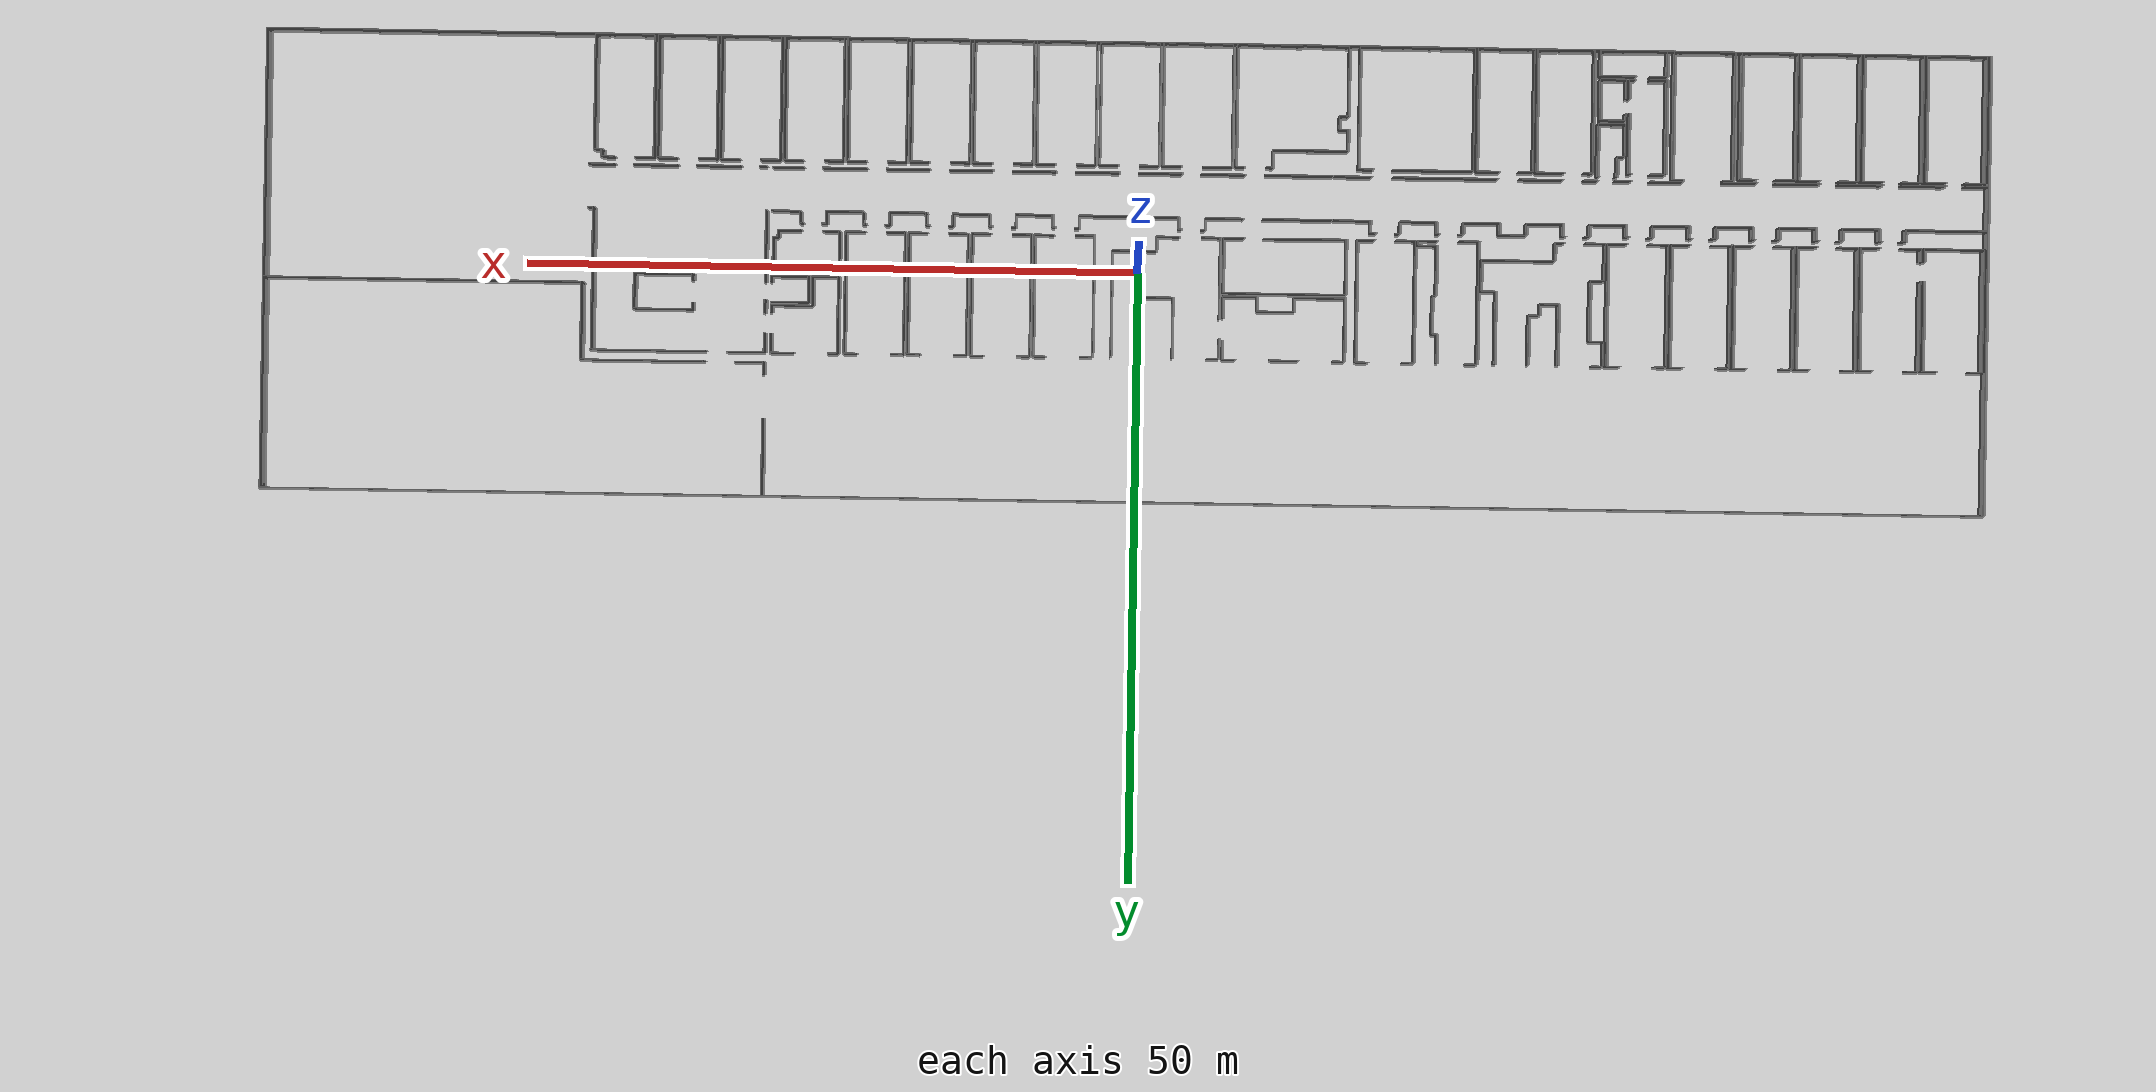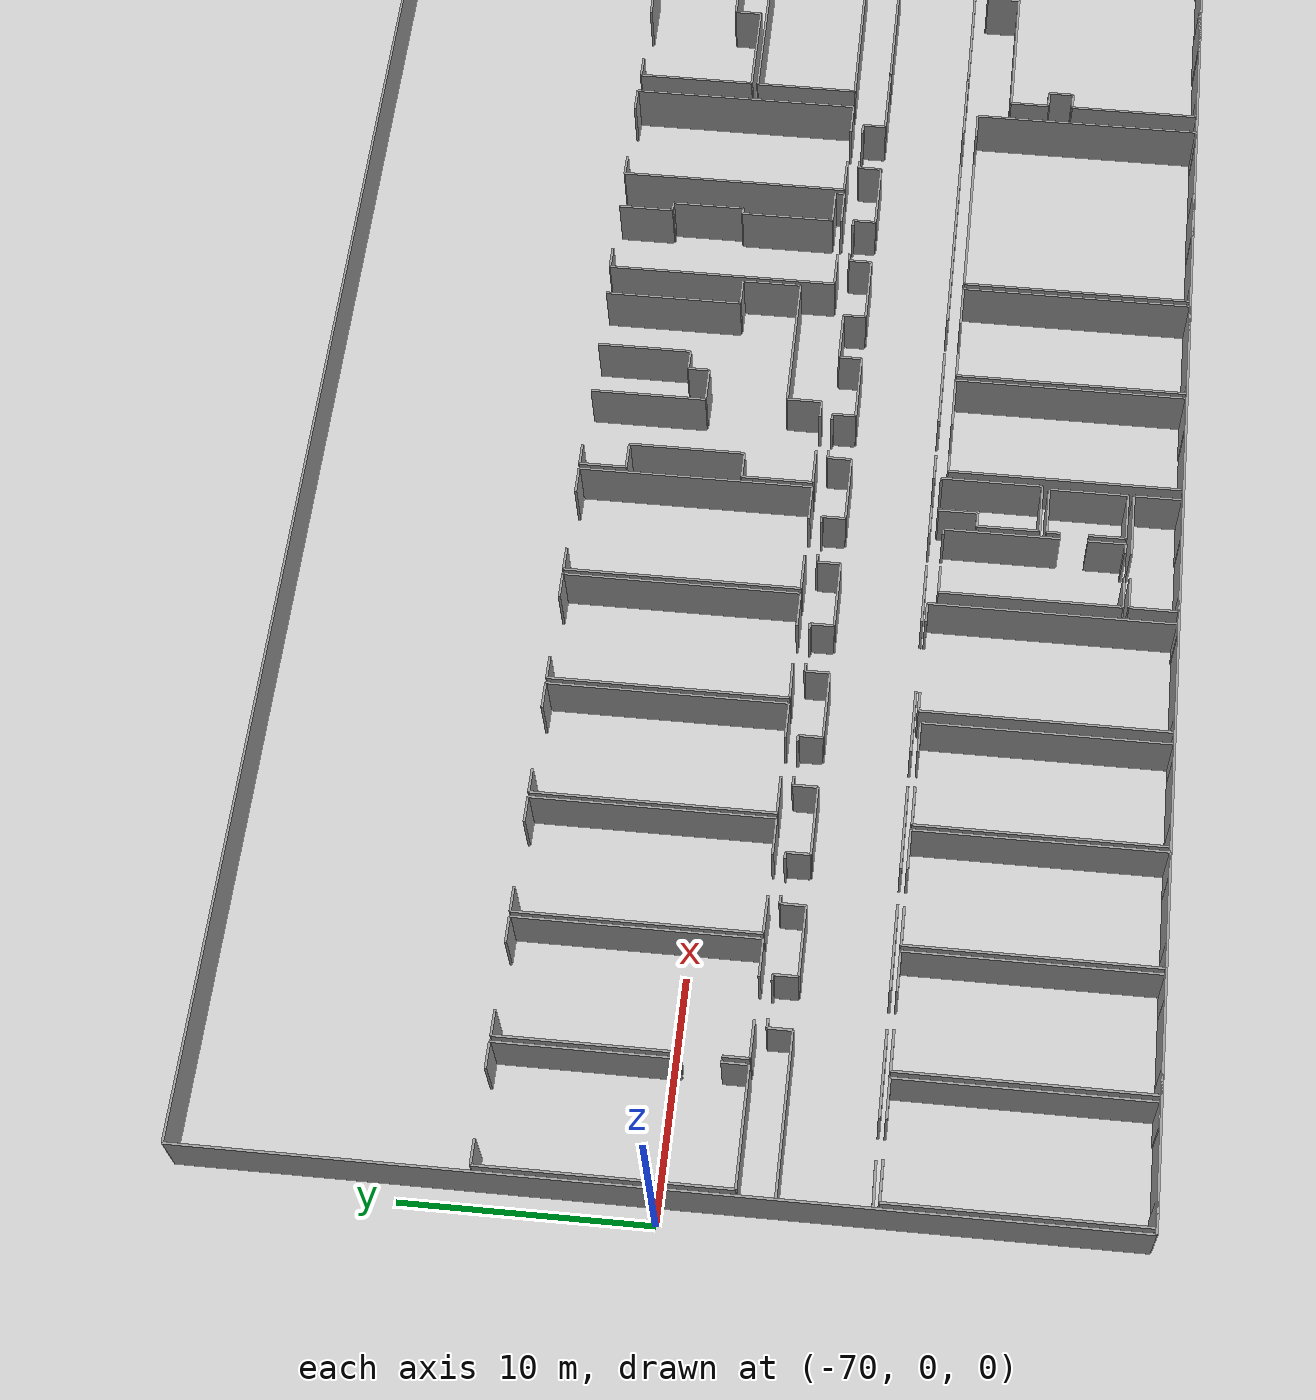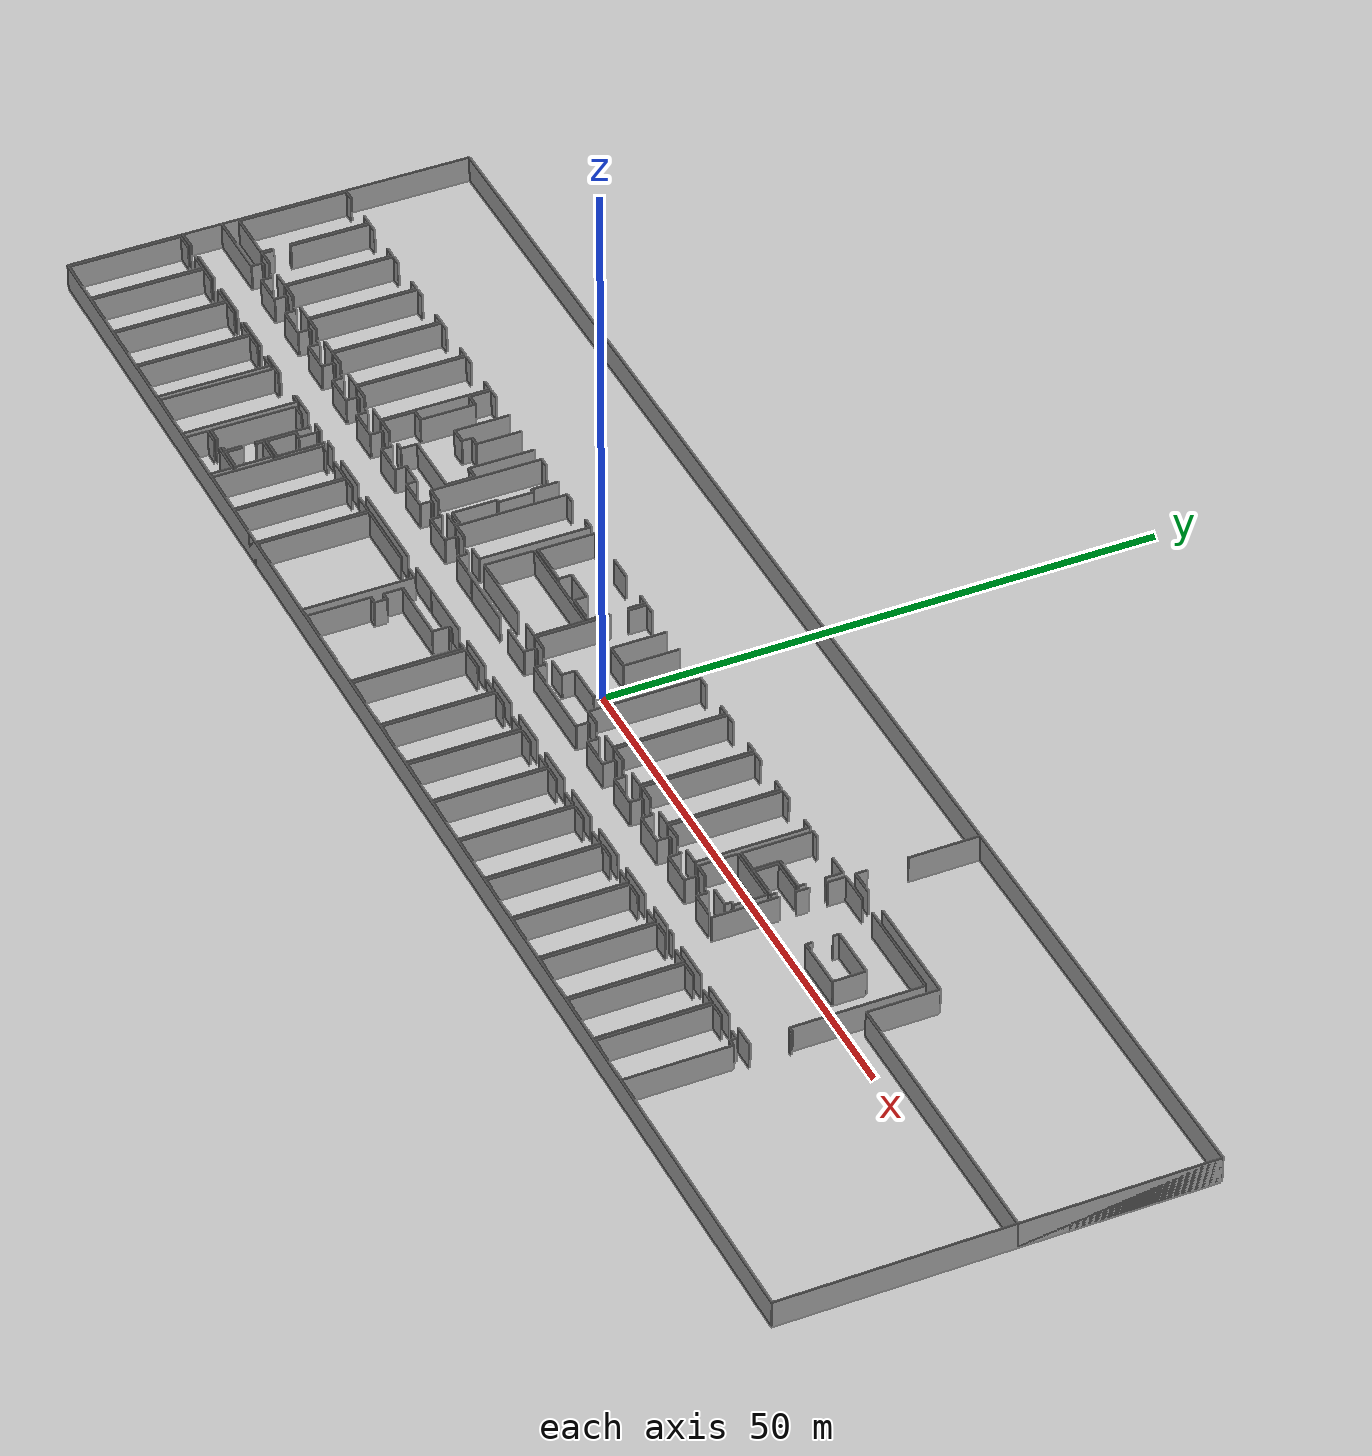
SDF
<sdf version="1.6">
  <world name="default">
    <light name="sun" type="directional">
      <cast_shadows>1</cast_shadows>
      <pose frame="">0 0 10 0 -0 0</pose>
      <diffuse>0.8 0.8 0.8 1</diffuse>
      <specular>0.1 0.1 0.1 1</specular>
      <attenuation>
        <range>1000</range>
        <constant>0.9</constant>
        <linear>0.01</linear>
        <quadratic>0.001</quadratic>
      </attenuation>
      <direction>-0.5 0.5 -1</direction>
    </light>
    <model name="ground_plane">
      <static>1</static>
      <link name="link">
        <collision name="collision">
          <geometry>
            <plane>
              <normal>0 0 1</normal>
              <size>100 100</size>
            </plane>
          </geometry>
          <surface>
            <friction>
              <ode>
                <mu>100</mu>
                <mu2>50</mu2>
              </ode>
              <torsional>
                <ode />
              </torsional>
            </friction>
            <contact>
              <ode />
            </contact>
            <bounce />
          </surface>
          <max_contacts>10</max_contacts>
        </collision>
        <visual name="visual">
          <cast_shadows>0</cast_shadows>
          <geometry>
            <plane>
              <normal>0 0 1</normal>
              <size>100 100</size>
            </plane>
          </geometry>
          <material>
            <script>
              <uri>file://media/materials/scripts/gazebo.material</uri>
              <name>Gazebo/Grey</name>
            </script>
          </material>
        </visual>
        <self_collide>0</self_collide>
        <kinematic>0</kinematic>
        <gravity>1</gravity>
      </link>
    </model>
    <gravity>0 0 -9.8</gravity>
    <magnetic_field>6e-06 2.3e-05 -4.2e-05</magnetic_field>
    <atmosphere type="adiabatic" />
    <physics default="0" name="default_physics" type="ode">
      <max_step_size>0.001</max_step_size>
      <real_time_factor>1</real_time_factor>
      <real_time_update_rate>1000</real_time_update_rate>
    </physics>
    <scene>
      <ambient>0.4 0.4 0.4 1</ambient>
      <background>0.7 0.7 0.7 1</background>
      <shadows>1</shadows>
    </scene>
    <spherical_coordinates>
      <surface_model>EARTH_WGS84</surface_model>
      <latitude_deg>0</latitude_deg>
      <longitude_deg>0</longitude_deg>
      <elevation>0</elevation>
      <heading_deg>0</heading_deg>
    </spherical_coordinates>
  <model name="50055641">
		<static>1</static>
		<link name="Wall_0">
			<collision name="Wall_0_Collision">
				<geometry>
					<box>
						<size>10.0288184438 0.1 2.5</size>
					</box>
				</geometry>
				<pose frame="">5.0144092219 0 1.25 0 0 0</pose>
			</collision>
			<visual name="Wall_0_Visual">
				<pose frame="">5.0144092219 0 1.25 0 0 0</pose>
				<geometry>
					<box>
						<size>10.0288184438 0.1 2.5</size>
					</box>
				</geometry>
				<material>
					<script>
						<uri>file://media/materials/scripts/gazebo.material</uri>
						<name>Gazebo/Grey</name>
					</script>
					<ambient>1 1 1 1</ambient>
				</material>
			</visual>
			<pose frame="">0.241211644175 -21.7269484188 0 0 0 1.57079632679</pose>
		</link>
		<link name="Wall_1">
			<collision name="Wall_1_Collision">
				<geometry>
					<box>
						<size>1.0270537902 0.1 2.5</size>
					</box>
				</geometry>
				<pose frame="">0.513526895098 0 1.25 0 0 0</pose>
			</collision>
			<visual name="Wall_1_Visual">
				<pose frame="">0.513526895098 0 1.25 0 0 0</pose>
				<geometry>
					<box>
						<size>1.0270537902 0.1 2.5</size>
					</box>
				</geometry>
				<material>
					<script>
						<uri>file://media/materials/scripts/gazebo.material</uri>
						<name>Gazebo/Grey</name>
					</script>
					<ambient>1 1 1 1</ambient>
				</material>
			</visual>
			<pose frame="">0.241211644175 -11.698129975 0 0 0 0.0</pose>
		</link>
		<link name="Wall_2">
			<collision name="Wall_2_Collision">
				<geometry>
					<box>
						<size>1.09827470198 0.1 2.5</size>
					</box>
				</geometry>
				<pose frame="">0.549137350988 0 1.25 0 0 0</pose>
			</collision>
			<visual name="Wall_2_Visual">
				<pose frame="">0.549137350988 0 1.25 0 0 0</pose>
				<geometry>
					<box>
						<size>1.09827470198 0.1 2.5</size>
					</box>
				</geometry>
				<material>
					<script>
						<uri>file://media/materials/scripts/gazebo.material</uri>
						<name>Gazebo/Grey</name>
					</script>
					<ambient>1 1 1 1</ambient>
				</material>
			</visual>
			<pose frame="">4.03915245845 -11.698129975 0 0 0 0.0</pose>
		</link>
		<link name="Wall_3">
			<collision name="Wall_3_Collision">
				<geometry>
					<box>
						<size>7.37193565997 0.1 2.5</size>
					</box>
				</geometry>
				<pose frame="">3.68596782998 0 1.25 0 0 0</pose>
			</collision>
			<visual name="Wall_3_Visual">
				<pose frame="">3.68596782998 0 1.25 0 0 0</pose>
				<geometry>
					<box>
						<size>7.37193565997 0.1 2.5</size>
					</box>
				</geometry>
				<material>
					<script>
						<uri>file://media/materials/scripts/gazebo.material</uri>
						<name>Gazebo/Grey</name>
					</script>
					<ambient>1 1 1 1</ambient>
				</material>
			</visual>
			<pose frame="">5.13742716043 -11.698129975 0 0 0 -1.57079632679</pose>
		</link>
		<link name="Wall_4">
			<collision name="Wall_4_Collision">
				<geometry>
					<box>
						<size>1.09776688799 0.1 2.5</size>
					</box>
				</geometry>
				<pose frame="">0.548883443994 0 1.25 0 0 0</pose>
			</collision>
			<visual name="Wall_4_Visual">
				<pose frame="">0.548883443994 0 1.25 0 0 0</pose>
				<geometry>
					<box>
						<size>1.09776688799 0.1 2.5</size>
					</box>
				</geometry>
				<material>
					<script>
						<uri>file://media/materials/scripts/gazebo.material</uri>
						<name>Gazebo/Grey</name>
					</script>
					<ambient>1 1 1 1</ambient>
				</material>
			</visual>
			<pose frame="">5.13742716043 -20.6282928563 0 0 0 -1.57079632679</pose>
		</link>
		<link name="Wall_5">
			<collision name="Wall_5_Collision">
				<geometry>
					<box>
						<size>4.8962155969 0.1 2.5</size>
					</box>
				</geometry>
				<pose frame="">2.44810779845 0 1.25 0 0 0</pose>
			</collision>
			<visual name="Wall_5_Visual">
				<pose frame="">2.44810779845 0 1.25 0 0 0</pose>
				<geometry>
					<box>
						<size>4.8962155969 0.1 2.5</size>
					</box>
				</geometry>
				<material>
					<script>
						<uri>file://media/materials/scripts/gazebo.material</uri>
						<name>Gazebo/Grey</name>
					</script>
					<ambient>1 1 1 1</ambient>
				</material>
			</visual>
			<pose frame="">5.13742716043 -21.7260597443 0 0 0 -3.14141115127</pose>
		</link>
		<link name="Wall_6">
			<collision name="Wall_6_Collision">
				<geometry>
					<box>
						<size>1.07923167744 0.1 2.5</size>
					</box>
				</geometry>
				<pose frame="">0.539615838718 0 1.25 0 0 0</pose>
			</collision>
			<visual name="Wall_6_Visual">
				<pose frame="">0.539615838718 0 1.25 0 0 0</pose>
				<geometry>
					<box>
						<size>1.07923167744 0.1 2.5</size>
					</box>
				</geometry>
				<material>
					<script>
						<uri>file://media/materials/scripts/gazebo.material</uri>
						<name>Gazebo/Grey</name>
					</script>
					<ambient>1 1 1 1</ambient>
				</material>
			</visual>
			<pose frame="">5.37724231614 -21.7275831863 0 0 0 1.57079632679</pose>
		</link>
		<link name="Wall_7">
			<collision name="Wall_7_Collision">
				<geometry>
					<box>
						<size>7.3582246823 0.1 2.5</size>
					</box>
				</geometry>
				<pose frame="">3.67911234115 0 1.25 0 0 0</pose>
			</collision>
			<visual name="Wall_7_Visual">
				<pose frame="">3.67911234115 0 1.25 0 0 0</pose>
				<geometry>
					<box>
						<size>7.3582246823 0.1 2.5</size>
					</box>
				</geometry>
				<material>
					<script>
						<uri>file://media/materials/scripts/gazebo.material</uri>
						<name>Gazebo/Grey</name>
					</script>
					<ambient>1 1 1 1</ambient>
				</material>
			</visual>
			<pose frame="">5.37724231614 -19.0742551004 0 0 0 1.57079632679</pose>
		</link>
		<link name="Wall_8">
			<collision name="Wall_8_Collision">
				<geometry>
					<box>
						<size>1.03492490701 0.1 2.5</size>
					</box>
				</geometry>
				<pose frame="">0.517462453503 0 1.25 0 0 0</pose>
			</collision>
			<visual name="Wall_8_Visual">
				<pose frame="">0.517462453503 0 1.25 0 0 0</pose>
				<geometry>
					<box>
						<size>1.03492490701 0.1 2.5</size>
					</box>
				</geometry>
				<material>
					<script>
						<uri>file://media/materials/scripts/gazebo.material</uri>
						<name>Gazebo/Grey</name>
					</script>
					<ambient>1 1 1 1</ambient>
				</material>
			</visual>
			<pose frame="">5.37724231614 -11.7160304181 0 0 0 0.0</pose>
		</link>
		<link name="Wall_9">
			<collision name="Wall_9_Collision">
				<geometry>
					<box>
						<size>1.09357742259 0.1 2.5</size>
					</box>
				</geometry>
				<pose frame="">0.546788711295 0 1.25 0 0 0</pose>
			</collision>
			<visual name="Wall_9_Visual">
				<pose frame="">0.546788711295 0 1.25 0 0 0</pose>
				<geometry>
					<box>
						<size>1.09357742259 0.1 2.5</size>
					</box>
				</geometry>
				<material>
					<script>
						<uri>file://media/materials/scripts/gazebo.material</uri>
						<name>Gazebo/Grey</name>
					</script>
					<ambient>1 1 1 1</ambient>
				</material>
			</visual>
			<pose frame="">9.21682387741 -11.7160304181 0 0 0 0.0</pose>
		</link>
		<link name="Wall_10">
			<collision name="Wall_10_Collision">
				<geometry>
					<box>
						<size>10.0168848151 0.1 2.5</size>
					</box>
				</geometry>
				<pose frame="">5.00844240755 0 1.25 0 0 0</pose>
			</collision>
			<visual name="Wall_10_Visual">
				<pose frame="">5.00844240755 0 1.25 0 0 0</pose>
				<geometry>
					<box>
						<size>10.0168848151 0.1 2.5</size>
					</box>
				</geometry>
				<material>
					<script>
						<uri>file://media/materials/scripts/gazebo.material</uri>
						<name>Gazebo/Grey</name>
					</script>
					<ambient>1 1 1 1</ambient>
				</material>
			</visual>
			<pose frame="">10.3104013 -11.7160304181 0 0 0 -1.57079632679</pose>
		</link>
		<link name="Wall_11">
			<collision name="Wall_11_Collision">
				<geometry>
					<box>
						<size>1.5776511064 0.1 2.5</size>
					</box>
				</geometry>
				<pose frame="">0.7888255532 0 1.25 0 0 0</pose>
			</collision>
			<visual name="Wall_11_Visual">
				<pose frame="">0.7888255532 0 1.25 0 0 0</pose>
				<geometry>
					<box>
						<size>1.5776511064 0.1 2.5</size>
					</box>
				</geometry>
				<material>
					<script>
						<uri>file://media/materials/scripts/gazebo.material</uri>
						<name>Gazebo/Grey</name>
					</script>
					<ambient>1 1 1 1</ambient>
				</material>
			</visual>
			<pose frame="">10.3104013 -21.7329152332 0 0 0 3.14159265359</pose>
		</link>
		<link name="Wall_12">
			<collision name="Wall_12_Collision">
				<geometry>
					<box>
						<size>1.58578509447 0.1 2.5</size>
					</box>
				</geometry>
				<pose frame="">0.792892547236 0 1.25 0 0 0</pose>
			</collision>
			<visual name="Wall_12_Visual">
				<pose frame="">0.792892547236 0 1.25 0 0 0</pose>
				<geometry>
					<box>
						<size>1.58578509447 0.1 2.5</size>
					</box>
				</geometry>
				<material>
					<script>
						<uri>file://media/materials/scripts/gazebo.material</uri>
						<name>Gazebo/Grey</name>
					</script>
					<ambient>1 1 1 1</ambient>
				</material>
			</visual>
			<pose frame="">6.96301844634 -21.7329152332 0 0 0 3.13823024532</pose>
		</link>
		<link name="Wall_13">
			<collision name="Wall_13_Collision">
				<geometry>
					<box>
						<size>6.66924805444 0.1 2.5</size>
					</box>
				</geometry>
				<pose frame="">3.33462402722 0 1.25 0 0 0</pose>
			</collision>
			<visual name="Wall_13_Visual">
				<pose frame="">3.33462402722 0 1.25 0 0 0</pose>
				<geometry>
					<box>
						<size>6.66924805444 0.1 2.5</size>
					</box>
				</geometry>
				<material>
					<script>
						<uri>file://media/materials/scripts/gazebo.material</uri>
						<name>Gazebo/Grey</name>
					</script>
					<ambient>1 1 1 1</ambient>
				</material>
			</visual>
			<pose frame="">0.0 -23.2500095215 0 0 0 0.0</pose>
		</link>
		<link name="Wall_14">
			<collision name="Wall_14_Collision">
				<geometry>
					<box>
						<size>0.993411113509 0.1 2.5</size>
					</box>
				</geometry>
				<pose frame="">0.496705556755 0 1.25 0 0 0</pose>
			</collision>
			<visual name="Wall_14_Visual">
				<pose frame="">0.496705556755 0 1.25 0 0 0</pose>
				<geometry>
					<box>
						<size>0.993411113509 0.1 2.5</size>
					</box>
				</geometry>
				<material>
					<script>
						<uri>file://media/materials/scripts/gazebo.material</uri>
						<name>Gazebo/Grey</name>
					</script>
					<ambient>1 1 1 1</ambient>
				</material>
			</visual>
			<pose frame="">6.66924805444 -23.2500095215 0 0 0 1.57079632679</pose>
		</link>
		<link name="Wall_15">
			<collision name="Wall_15_Collision">
				<geometry>
					<box>
						<size>0.384161281723 0.1 2.5</size>
					</box>
				</geometry>
				<pose frame="">0.192080640861 0 1.25 0 0 0</pose>
			</collision>
			<visual name="Wall_15_Visual">
				<pose frame="">0.192080640861 0 1.25 0 0 0</pose>
				<geometry>
					<box>
						<size>0.384161281723 0.1 2.5</size>
					</box>
				</geometry>
				<material>
					<script>
						<uri>file://media/materials/scripts/gazebo.material</uri>
						<name>Gazebo/Grey</name>
					</script>
					<ambient>1 1 1 1</ambient>
				</material>
			</visual>
			<pose frame="">6.66924805444 -22.256598408 0 0 0 0.0</pose>
		</link>
		<link name="Wall_16">
			<collision name="Wall_16_Collision">
				<geometry>
					<box>
						<size>0.259239040739 0.1 2.5</size>
					</box>
				</geometry>
				<pose frame="">0.12961952037 0 1.25 0 0 0</pose>
			</collision>
			<visual name="Wall_16_Visual">
				<pose frame="">0.12961952037 0 1.25 0 0 0</pose>
				<geometry>
					<box>
						<size>0.259239040739 0.1 2.5</size>
					</box>
				</geometry>
				<material>
					<script>
						<uri>file://media/materials/scripts/gazebo.material</uri>
						<name>Gazebo/Grey</name>
					</script>
					<ambient>1 1 1 1</ambient>
				</material>
			</visual>
			<pose frame="">8.59868730084 -22.256598408 0 0 0 0.0</pose>
		</link>
		<link name="Wall_17">
			<collision name="Wall_17_Collision">
				<geometry>
					<box>
						<size>1.01258109155 0.1 2.5</size>
					</box>
				</geometry>
				<pose frame="">0.506290545773 0 1.25 0 0 0</pose>
			</collision>
			<visual name="Wall_17_Visual">
				<pose frame="">0.506290545773 0 1.25 0 0 0</pose>
				<geometry>
					<box>
						<size>1.01258109155 0.1 2.5</size>
					</box>
				</geometry>
				<material>
					<script>
						<uri>file://media/materials/scripts/gazebo.material</uri>
						<name>Gazebo/Grey</name>
					</script>
					<ambient>1 1 1 1</ambient>
				</material>
			</visual>
			<pose frame="">8.85792634158 -22.256598408 0 0 0 -1.57079632679</pose>
		</link>
		<link name="Wall_18">
			<collision name="Wall_18_Collision">
				<geometry>
					<box>
						<size>2.97578996813 0.1 2.5</size>
					</box>
				</geometry>
				<pose frame="">1.48789498407 0 1.25 0 0 0</pose>
			</collision>
			<visual name="Wall_18_Visual">
				<pose frame="">1.48789498407 0 1.25 0 0 0</pose>
				<geometry>
					<box>
						<size>2.97578996813 0.1 2.5</size>
					</box>
				</geometry>
				<material>
					<script>
						<uri>file://media/materials/scripts/gazebo.material</uri>
						<name>Gazebo/Grey</name>
					</script>
					<ambient>1 1 1 1</ambient>
				</material>
			</visual>
			<pose frame="">8.85792634158 -23.2691794995 0 0 0 0.0</pose>
		</link>
		<link name="Wall_19">
			<collision name="Wall_19_Collision">
				<geometry>
					<box>
						<size>1.02718074369 0.1 2.5</size>
					</box>
				</geometry>
				<pose frame="">0.513590371847 0 1.25 0 0 0</pose>
			</collision>
			<visual name="Wall_19_Visual">
				<pose frame="">0.513590371847 0 1.25 0 0 0</pose>
				<geometry>
					<box>
						<size>1.02718074369 0.1 2.5</size>
					</box>
				</geometry>
				<material>
					<script>
						<uri>file://media/materials/scripts/gazebo.material</uri>
						<name>Gazebo/Grey</name>
					</script>
					<ambient>1 1 1 1</ambient>
				</material>
			</visual>
			<pose frame="">11.8337163097 -23.2691794995 0 0 0 1.57079632679</pose>
		</link>
		<link name="Wall_20">
			<collision name="Wall_20_Collision">
				<geometry>
					<box>
						<size>0.345567418655 0.1 2.5</size>
					</box>
				</geometry>
				<pose frame="">0.172783709327 0 1.25 0 0 0</pose>
			</collision>
			<visual name="Wall_20_Visual">
				<pose frame="">0.172783709327 0 1.25 0 0 0</pose>
				<geometry>
					<box>
						<size>0.345567418655 0.1 2.5</size>
					</box>
				</geometry>
				<material>
					<script>
						<uri>file://media/materials/scripts/gazebo.material</uri>
						<name>Gazebo/Grey</name>
					</script>
					<ambient>1 1 1 1</ambient>
				</material>
			</visual>
			<pose frame="">11.8337163097 -22.2419987559 0 0 0 0.0</pose>
		</link>
		<link name="Wall_21">
			<collision name="Wall_21_Collision">
				<geometry>
					<box>
						<size>0.268760553009 0.1 2.5</size>
					</box>
				</geometry>
				<pose frame="">0.134380276505 0 1.25 0 0 0</pose>
			</collision>
			<visual name="Wall_21_Visual">
				<pose frame="">0.134380276505 0 1.25 0 0 0</pose>
				<geometry>
					<box>
						<size>0.268760553009 0.1 2.5</size>
					</box>
				</geometry>
				<material>
					<script>
						<uri>file://media/materials/scripts/gazebo.material</uri>
						<name>Gazebo/Grey</name>
					</script>
					<ambient>1 1 1 1</ambient>
				</material>
			</visual>
			<pose frame="">13.7632825096 -22.2419987559 0 0 0 0.0</pose>
		</link>
		<link name="Wall_22">
			<collision name="Wall_22_Collision">
				<geometry>
					<box>
						<size>1.01765923142 0.1 2.5</size>
					</box>
				</geometry>
				<pose frame="">0.508829615712 0 1.25 0 0 0</pose>
			</collision>
			<visual name="Wall_22_Visual">
				<pose frame="">0.508829615712 0 1.25 0 0 0</pose>
				<geometry>
					<box>
						<size>1.01765923142 0.1 2.5</size>
					</box>
				</geometry>
				<material>
					<script>
						<uri>file://media/materials/scripts/gazebo.material</uri>
						<name>Gazebo/Grey</name>
					</script>
					<ambient>1 1 1 1</ambient>
				</material>
			</visual>
			<pose frame="">14.0320430626 -22.2419987559 0 0 0 -1.57079632679</pose>
		</link>
		<link name="Wall_23">
			<collision name="Wall_23_Collision">
				<geometry>
					<box>
						<size>2.94709847783 0.1 2.5</size>
					</box>
				</geometry>
				<pose frame="">1.47354923891 0 1.25 0 0 0</pose>
			</collision>
			<visual name="Wall_23_Visual">
				<pose frame="">1.47354923891 0 1.25 0 0 0</pose>
				<geometry>
					<box>
						<size>2.94709847783 0.1 2.5</size>
					</box>
				</geometry>
				<material>
					<script>
						<uri>file://media/materials/scripts/gazebo.material</uri>
						<name>Gazebo/Grey</name>
					</script>
					<ambient>1 1 1 1</ambient>
				</material>
			</visual>
			<pose frame="">14.0320430626 -23.2596579873 0 0 0 0.0</pose>
		</link>
		<link name="Wall_24">
			<collision name="Wall_24_Collision">
				<geometry>
					<box>
						<size>1.00801076566 0.1 2.5</size>
					</box>
				</geometry>
				<pose frame="">0.504005382828 0 1.25 0 0 0</pose>
			</collision>
			<visual name="Wall_24_Visual">
				<pose frame="">0.504005382828 0 1.25 0 0 0</pose>
				<geometry>
					<box>
						<size>1.00801076566 0.1 2.5</size>
					</box>
				</geometry>
				<material>
					<script>
						<uri>file://media/materials/scripts/gazebo.material</uri>
						<name>Gazebo/Grey</name>
					</script>
					<ambient>1 1 1 1</ambient>
				</material>
			</visual>
			<pose frame="">16.9791415405 -23.2596579873 0 0 0 1.57079632679</pose>
		</link>
		<link name="Wall_25">
			<collision name="Wall_25_Collision">
				<geometry>
					<box>
						<size>0.383907374729 0.1 2.5</size>
					</box>
				</geometry>
				<pose frame="">0.191953687364 0 1.25 0 0 0</pose>
			</collision>
			<visual name="Wall_25_Visual">
				<pose frame="">0.191953687364 0 1.25 0 0 0</pose>
				<geometry>
					<box>
						<size>0.383907374729 0.1 2.5</size>
					</box>
				</geometry>
				<material>
					<script>
						<uri>file://media/materials/scripts/gazebo.material</uri>
						<name>Gazebo/Grey</name>
					</script>
					<ambient>1 1 1 1</ambient>
				</material>
			</visual>
			<pose frame="">16.9791415405 -22.2516472216 0 0 0 0.0</pose>
		</link>
		<link name="Wall_26">
			<collision name="Wall_26_Collision">
				<geometry>
					<box>
						<size>0.264824994604 0.1 2.5</size>
					</box>
				</geometry>
				<pose frame="">0.132412497302 0 1.25 0 0 0</pose>
			</collision>
			<visual name="Wall_26_Visual">
				<pose frame="">0.132412497302 0 1.25 0 0 0</pose>
				<geometry>
					<box>
						<size>0.264824994604 0.1 2.5</size>
					</box>
				</geometry>
				<material>
					<script>
						<uri>file://media/materials/scripts/gazebo.material</uri>
						<name>Gazebo/Grey</name>
					</script>
					<ambient>1 1 1 1</ambient>
				</material>
			</visual>
			<pose frame="">18.9360027422 -22.2516472216 0 0 0 0.0</pose>
		</link>
		<link name="Wall_27">
			<collision name="Wall_27_Collision">
				<geometry>
					<box>
						<size>1.01423148701 0.1 2.5</size>
					</box>
				</geometry>
				<pose frame="">0.507115743503 0 1.25 0 0 0</pose>
			</collision>
			<visual name="Wall_27_Visual">
				<pose frame="">0.507115743503 0 1.25 0 0 0</pose>
				<geometry>
					<box>
						<size>1.01423148701 0.1 2.5</size>
					</box>
				</geometry>
				<material>
					<script>
						<uri>file://media/materials/scripts/gazebo.material</uri>
						<name>Gazebo/Grey</name>
					</script>
					<ambient>1 1 1 1</ambient>
				</material>
			</visual>
			<pose frame="">19.2008277368 -22.2516472216 0 0 0 -1.57079632679</pose>
		</link>
		<link name="Wall_28">
			<collision name="Wall_28_Collision">
				<geometry>
					<box>
						<size>2.94760629182 0.1 2.5</size>
					</box>
				</geometry>
				<pose frame="">1.47380314591 0 1.25 0 0 0</pose>
			</collision>
			<visual name="Wall_28_Visual">
				<pose frame="">1.47380314591 0 1.25 0 0 0</pose>
				<geometry>
					<box>
						<size>2.94760629182 0.1 2.5</size>
					</box>
				</geometry>
				<material>
					<script>
						<uri>file://media/materials/scripts/gazebo.material</uri>
						<name>Gazebo/Grey</name>
					</script>
					<ambient>1 1 1 1</ambient>
				</material>
			</visual>
			<pose frame="">19.2008277368 -23.2658787086 0 0 0 0.0</pose>
		</link>
		<link name="Wall_29">
			<collision name="Wall_29_Collision">
				<geometry>
					<box>
						<size>1.01562797547 0.1 2.5</size>
					</box>
				</geometry>
				<pose frame="">0.507813987736 0 1.25 0 0 0</pose>
			</collision>
			<visual name="Wall_29_Visual">
				<pose frame="">0.507813987736 0 1.25 0 0 0</pose>
				<geometry>
					<box>
						<size>1.01562797547 0.1 2.5</size>
					</box>
				</geometry>
				<material>
					<script>
						<uri>file://media/materials/scripts/gazebo.material</uri>
						<name>Gazebo/Grey</name>
					</script>
					<ambient>1 1 1 1</ambient>
				</material>
			</visual>
			<pose frame="">22.1484340286 -23.2658787086 0 0 0 1.57079632679</pose>
		</link>
		<link name="Wall_30">
			<collision name="Wall_30_Collision">
				<geometry>
					<box>
						<size>0.365753024667 0.1 2.5</size>
					</box>
				</geometry>
				<pose frame="">0.182876512334 0 1.25 0 0 0</pose>
			</collision>
			<visual name="Wall_30_Visual">
				<pose frame="">0.182876512334 0 1.25 0 0 0</pose>
				<geometry>
					<box>
						<size>0.365753024667 0.1 2.5</size>
					</box>
				</geometry>
				<material>
					<script>
						<uri>file://media/materials/scripts/gazebo.material</uri>
						<name>Gazebo/Grey</name>
					</script>
					<ambient>1 1 1 1</ambient>
				</material>
			</visual>
			<pose frame="">22.1484340286 -22.2502507332 0 0 0 0.0</pose>
		</link>
		<link name="Wall_31">
			<collision name="Wall_31_Collision">
				<geometry>
					<box>
						<size>0.283868019145 0.1 2.5</size>
					</box>
				</geometry>
				<pose frame="">0.141934009572 0 1.25 0 0 0</pose>
			</collision>
			<visual name="Wall_31_Visual">
				<pose frame="">0.141934009572 0 1.25 0 0 0</pose>
				<geometry>
					<box>
						<size>0.283868019145 0.1 2.5</size>
					</box>
				</geometry>
				<material>
					<script>
						<uri>file://media/materials/scripts/gazebo.material</uri>
						<name>Gazebo/Grey</name>
					</script>
					<ambient>1 1 1 1</ambient>
				</material>
			</visual>
			<pose frame="">24.0752072516 -22.2502507332 0 0 0 0.0</pose>
		</link>
		<link name="Wall_32">
			<collision name="Wall_32_Collision">
				<geometry>
					<box>
						<size>1.00179004431 0.1 2.5</size>
					</box>
				</geometry>
				<pose frame="">0.500895022153 0 1.25 0 0 0</pose>
			</collision>
			<visual name="Wall_32_Visual">
				<pose frame="">0.500895022153 0 1.25 0 0 0</pose>
				<geometry>
					<box>
						<size>1.00179004431 0.1 2.5</size>
					</box>
				</geometry>
				<material>
					<script>
						<uri>file://media/materials/scripts/gazebo.material</uri>
						<name>Gazebo/Grey</name>
					</script>
					<ambient>1 1 1 1</ambient>
				</material>
			</visual>
			<pose frame="">24.3590752707 -22.2502507332 0 0 0 -1.57079632679</pose>
		</link>
		<link name="Wall_33">
			<collision name="Wall_33_Collision">
				<geometry>
					<box>
						<size>2.95496959464 0.1 2.5</size>
					</box>
				</geometry>
				<pose frame="">1.47748479732 0 1.25 0 0 0</pose>
			</collision>
			<visual name="Wall_33_Visual">
				<pose frame="">1.47748479732 0 1.25 0 0 0</pose>
				<geometry>
					<box>
						<size>2.95496959464 0.1 2.5</size>
					</box>
				</geometry>
				<material>
					<script>
						<uri>file://media/materials/scripts/gazebo.material</uri>
						<name>Gazebo/Grey</name>
					</script>
					<ambient>1 1 1 1</ambient>
				</material>
			</visual>
			<pose frame="">24.3590752707 -23.2520407775 0 0 0 0.0</pose>
		</link>
		<link name="Wall_34">
			<collision name="Wall_34_Collision">
				<geometry>
					<box>
						<size>0.984905229215 0.1 2.5</size>
					</box>
				</geometry>
				<pose frame="">0.492452614607 0 1.25 0 0 0</pose>
			</collision>
			<visual name="Wall_34_Visual">
				<pose frame="">0.492452614607 0 1.25 0 0 0</pose>
				<geometry>
					<box>
						<size>0.984905229215 0.1 2.5</size>
					</box>
				</geometry>
				<material>
					<script>
						<uri>file://media/materials/scripts/gazebo.material</uri>
						<name>Gazebo/Grey</name>
					</script>
					<ambient>1 1 1 1</ambient>
				</material>
			</visual>
			<pose frame="">27.3140448654 -23.2520407775 0 0 0 1.57079632679</pose>
		</link>
		<link name="Wall_35">
			<collision name="Wall_35_Collision">
				<geometry>
					<box>
						<size>0.342139674237 0.1 2.5</size>
					</box>
				</geometry>
				<pose frame="">0.171069837119 0 1.25 0 0 0</pose>
			</collision>
			<visual name="Wall_35_Visual">
				<pose frame="">0.171069837119 0 1.25 0 0 0</pose>
				<geometry>
					<box>
						<size>0.342139674237 0.1 2.5</size>
					</box>
				</geometry>
				<material>
					<script>
						<uri>file://media/materials/scripts/gazebo.material</uri>
						<name>Gazebo/Grey</name>
					</script>
					<ambient>1 1 1 1</ambient>
				</material>
			</visual>
			<pose frame="">27.3140448654 -22.2671355482 0 0 0 0.0</pose>
		</link>
		<link name="Wall_36">
			<collision name="Wall_36_Collision">
				<geometry>
					<box>
						<size>0.275996902335 0.1 2.5</size>
					</box>
				</geometry>
				<pose frame="">0.137998451167 0 1.25 0 0 0</pose>
			</collision>
			<visual name="Wall_36_Visual">
				<pose frame="">0.137998451167 0 1.25 0 0 0</pose>
				<geometry>
					<box>
						<size>0.275996902335 0.1 2.5</size>
					</box>
				</geometry>
				<material>
					<script>
						<uri>file://media/materials/scripts/gazebo.material</uri>
						<name>Gazebo/Grey</name>
					</script>
					<ambient>1 1 1 1</ambient>
				</material>
			</visual>
			<pose frame="">29.2467849027 -22.2671355482 0 0 0 0.0</pose>
		</link>
		<link name="Wall_37">
			<collision name="Wall_37_Collision">
				<geometry>
					<box>
						<size>0.99874316038 0.1 2.5</size>
					</box>
				</geometry>
				<pose frame="">0.49937158019 0 1.25 0 0 0</pose>
			</collision>
			<visual name="Wall_37_Visual">
				<pose frame="">0.49937158019 0 1.25 0 0 0</pose>
				<geometry>
					<box>
						<size>0.99874316038 0.1 2.5</size>
					</box>
				</geometry>
				<material>
					<script>
						<uri>file://media/materials/scripts/gazebo.material</uri>
						<name>Gazebo/Grey</name>
					</script>
					<ambient>1 1 1 1</ambient>
				</material>
			</visual>
			<pose frame="">29.522781805 -22.2671355482 0 0 0 -1.57079632679</pose>
		</link>
		<link name="Wall_38">
			<collision name="Wall_38_Collision">
				<geometry>
					<box>
						<size>2.93643438409 0.1 2.5</size>
					</box>
				</geometry>
				<pose frame="">1.46821719204 0 1.25 0 0 0</pose>
			</collision>
			<visual name="Wall_38_Visual">
				<pose frame="">1.46821719204 0 1.25 0 0 0</pose>
				<geometry>
					<box>
						<size>2.93643438409 0.1 2.5</size>
					</box>
				</geometry>
				<material>
					<script>
						<uri>file://media/materials/scripts/gazebo.material</uri>
						<name>Gazebo/Grey</name>
					</script>
					<ambient>1 1 1 1</ambient>
				</material>
			</visual>
			<pose frame="">29.522781805 -23.2658787086 0 0 0 0.0</pose>
		</link>
		<link name="Wall_39">
			<collision name="Wall_39_Collision">
				<geometry>
					<box>
						<size>1.01562797547 0.1 2.5</size>
					</box>
				</geometry>
				<pose frame="">0.507813987736 0 1.25 0 0 0</pose>
			</collision>
			<visual name="Wall_39_Visual">
				<pose frame="">0.507813987736 0 1.25 0 0 0</pose>
				<geometry>
					<box>
						<size>1.01562797547 0.1 2.5</size>
					</box>
				</geometry>
				<material>
					<script>
						<uri>file://media/materials/scripts/gazebo.material</uri>
						<name>Gazebo/Grey</name>
					</script>
					<ambient>1 1 1 1</ambient>
				</material>
			</visual>
			<pose frame="">32.4592161891 -23.2658787086 0 0 0 1.57079632679</pose>
		</link>
		<link name="Wall_40">
			<collision name="Wall_40_Collision">
				<geometry>
					<box>
						<size>0.364356536201 0.1 2.5</size>
					</box>
				</geometry>
				<pose frame="">0.1821782681 0 1.25 0 0 0</pose>
			</collision>
			<visual name="Wall_40_Visual">
				<pose frame="">0.1821782681 0 1.25 0 0 0</pose>
				<geometry>
					<box>
						<size>0.364356536201 0.1 2.5</size>
					</box>
				</geometry>
				<material>
					<script>
						<uri>file://media/materials/scripts/gazebo.material</uri>
						<name>Gazebo/Grey</name>
					</script>
					<ambient>1 1 1 1</ambient>
				</material>
			</visual>
			<pose frame="">32.4592161891 -22.2502507332 0 0 0 0.0</pose>
		</link>
		<link name="Wall_41">
			<collision name="Wall_41_Collision">
				<geometry>
					<box>
						<size>0.258731226752 0.1 2.5</size>
					</box>
				</geometry>
				<pose frame="">0.129365613376 0 1.25 0 0 0</pose>
			</collision>
			<visual name="Wall_41_Visual">
				<pose frame="">0.129365613376 0 1.25 0 0 0</pose>
				<geometry>
					<box>
						<size>0.258731226752 0.1 2.5</size>
					</box>
				</geometry>
				<material>
					<script>
						<uri>file://media/materials/scripts/gazebo.material</uri>
						<name>Gazebo/Grey</name>
					</script>
					<ambient>1 1 1 1</ambient>
				</material>
			</visual>
			<pose frame="">34.4054132971 -22.2502507332 0 0 0 0.0</pose>
		</link>
		<link name="Wall_42">
			<collision name="Wall_42_Collision">
				<geometry>
					<box>
						<size>1.00483692823 0.1 2.5</size>
					</box>
				</geometry>
				<pose frame="">0.502418464117 0 1.25 0 0 0</pose>
			</collision>
			<visual name="Wall_42_Visual">
				<pose frame="">0.502418464117 0 1.25 0 0 0</pose>
				<geometry>
					<box>
						<size>1.00483692823 0.1 2.5</size>
					</box>
				</geometry>
				<material>
					<script>
						<uri>file://media/materials/scripts/gazebo.material</uri>
						<name>Gazebo/Grey</name>
					</script>
					<ambient>1 1 1 1</ambient>
				</material>
			</visual>
			<pose frame="">34.6641445239 -22.2502507332 0 0 0 -1.57079632679</pose>
		</link>
		<link name="Wall_43">
			<collision name="Wall_43_Collision">
				<geometry>
					<box>
						<size>2.96664931636 0.1 2.5</size>
					</box>
				</geometry>
				<pose frame="">1.48332465818 0 1.25 0 0 0</pose>
			</collision>
			<visual name="Wall_43_Visual">
				<pose frame="">1.48332465818 0 1.25 0 0 0</pose>
				<geometry>
					<box>
						<size>2.96664931636 0.1 2.5</size>
					</box>
				</geometry>
				<material>
					<script>
						<uri>file://media/materials/scripts/gazebo.material</uri>
						<name>Gazebo/Grey</name>
					</script>
					<ambient>1 1 1 1</ambient>
				</material>
			</visual>
			<pose frame="">34.6641445239 -23.2550876614 0 0 0 0.0</pose>
		</link>
		<link name="Wall_44">
			<collision name="Wall_44_Collision">
				<geometry>
					<box>
						<size>0.978303647374 0.1 2.5</size>
					</box>
				</geometry>
				<pose frame="">0.489151823687 0 1.25 0 0 0</pose>
			</collision>
			<visual name="Wall_44_Visual">
				<pose frame="">0.489151823687 0 1.25 0 0 0</pose>
				<geometry>
					<box>
						<size>0.978303647374 0.1 2.5</size>
					</box>
				</geometry>
				<material>
					<script>
						<uri>file://media/materials/scripts/gazebo.material</uri>
						<name>Gazebo/Grey</name>
					</script>
					<ambient>1 1 1 1</ambient>
				</material>
			</visual>
			<pose frame="">37.6307938402 -23.2550876614 0 0 0 1.57079632679</pose>
		</link>
		<link name="Wall_45">
			<collision name="Wall_45_Collision">
				<geometry>
					<box>
						<size>2.2027701253 0.1 2.5</size>
					</box>
				</geometry>
				<pose frame="">1.10138506265 0 1.25 0 0 0</pose>
			</collision>
			<visual name="Wall_45_Visual">
				<pose frame="">1.10138506265 0 1.25 0 0 0</pose>
				<geometry>
					<box>
						<size>2.2027701253 0.1 2.5</size>
					</box>
				</geometry>
				<material>
					<script>
						<uri>file://media/materials/scripts/gazebo.material</uri>
						<name>Gazebo/Grey</name>
					</script>
					<ambient>1 1 1 1</ambient>
				</material>
			</visual>
			<pose frame="">37.6307938402 -22.276784014 0 0 0 0.0</pose>
		</link>
		<link name="Wall_46">
			<collision name="Wall_46_Collision">
				<geometry>
					<box>
						<size>0.971955972527 0.1 2.5</size>
					</box>
				</geometry>
				<pose frame="">0.485977986264 0 1.25 0 0 0</pose>
			</collision>
			<visual name="Wall_46_Visual">
				<pose frame="">0.485977986264 0 1.25 0 0 0</pose>
				<geometry>
					<box>
						<size>0.971955972527 0.1 2.5</size>
					</box>
				</geometry>
				<material>
					<script>
						<uri>file://media/materials/scripts/gazebo.material</uri>
						<name>Gazebo/Grey</name>
					</script>
					<ambient>1 1 1 1</ambient>
				</material>
			</visual>
			<pose frame="">39.8335639655 -22.276784014 0 0 0 -1.57079632679</pose>
		</link>
		<link name="Wall_47">
			<collision name="Wall_47_Collision">
				<geometry>
					<box>
						<size>2.94760629182 0.1 2.5</size>
					</box>
				</geometry>
				<pose frame="">1.47380314591 0 1.25 0 0 0</pose>
			</collision>
			<visual name="Wall_47_Visual">
				<pose frame="">1.47380314591 0 1.25 0 0 0</pose>
				<geometry>
					<box>
						<size>2.94760629182 0.1 2.5</size>
					</box>
				</geometry>
				<material>
					<script>
						<uri>file://media/materials/scripts/gazebo.material</uri>
						<name>Gazebo/Grey</name>
					</script>
					<ambient>1 1 1 1</ambient>
				</material>
			</visual>
			<pose frame="">39.8335639655 -23.2487399865 0 0 0 0.0</pose>
		</link>
		<link name="Wall_48">
			<collision name="Wall_48_Collision">
				<geometry>
					<box>
						<size>0.984651322221 0.1 2.5</size>
					</box>
				</geometry>
				<pose frame="">0.49232566111 0 1.25 0 0 0</pose>
			</collision>
			<visual name="Wall_48_Visual">
				<pose frame="">0.49232566111 0 1.25 0 0 0</pose>
				<geometry>
					<box>
						<size>0.984651322221 0.1 2.5</size>
					</box>
				</geometry>
				<material>
					<script>
						<uri>file://media/materials/scripts/gazebo.material</uri>
						<name>Gazebo/Grey</name>
					</script>
					<ambient>1 1 1 1</ambient>
				</material>
			</visual>
			<pose frame="">42.7811702573 -23.2487399865 0 0 0 1.57079632679</pose>
		</link>
		<link name="Wall_49">
			<collision name="Wall_49_Collision">
				<geometry>
					<box>
						<size>0.359786210311 0.1 2.5</size>
					</box>
				</geometry>
				<pose frame="">0.179893105156 0 1.25 0 0 0</pose>
			</collision>
			<visual name="Wall_49_Visual">
				<pose frame="">0.179893105156 0 1.25 0 0 0</pose>
				<geometry>
					<box>
						<size>0.359786210311 0.1 2.5</size>
					</box>
				</geometry>
				<material>
					<script>
						<uri>file://media/materials/scripts/gazebo.material</uri>
						<name>Gazebo/Grey</name>
					</script>
					<ambient>1 1 1 1</ambient>
				</material>
			</visual>
			<pose frame="">42.7811702573 -22.2640886643 0 0 0 0.0</pose>
		</link>
		<link name="Wall_50">
			<collision name="Wall_50_Collision">
				<geometry>
					<box>
						<size>0.259239040739 0.1 2.5</size>
					</box>
				</geometry>
				<pose frame="">0.12961952037 0 1.25 0 0 0</pose>
			</collision>
			<visual name="Wall_50_Visual">
				<pose frame="">0.12961952037 0 1.25 0 0 0</pose>
				<geometry>
					<box>
						<size>0.259239040739 0.1 2.5</size>
					</box>
				</geometry>
				<material>
					<script>
						<uri>file://media/materials/scripts/gazebo.material</uri>
						<name>Gazebo/Grey</name>
					</script>
					<ambient>1 1 1 1</ambient>
				</material>
			</visual>
			<pose frame="">44.721654458 -22.2640886643 0 0 0 0.0</pose>
		</link>
		<link name="Wall_51">
			<collision name="Wall_51_Collision">
				<geometry>
					<box>
						<size>0.995569322957 0.1 2.5</size>
					</box>
				</geometry>
				<pose frame="">0.497784661479 0 1.25 0 0 0</pose>
			</collision>
			<visual name="Wall_51_Visual">
				<pose frame="">0.497784661479 0 1.25 0 0 0</pose>
				<geometry>
					<box>
						<size>0.995569322957 0.1 2.5</size>
					</box>
				</geometry>
				<material>
					<script>
						<uri>file://media/materials/scripts/gazebo.material</uri>
						<name>Gazebo/Grey</name>
					</script>
					<ambient>1 1 1 1</ambient>
				</material>
			</visual>
			<pose frame="">44.9808934987 -22.2640886643 0 0 0 -1.57079632679</pose>
		</link>
		<link name="Wall_52">
			<collision name="Wall_52_Collision">
				<geometry>
					<box>
						<size>2.96614150237 0.1 2.5</size>
					</box>
				</geometry>
				<pose frame="">1.48307075118 0 1.25 0 0 0</pose>
			</collision>
			<visual name="Wall_52_Visual">
				<pose frame="">1.48307075118 0 1.25 0 0 0</pose>
				<geometry>
					<box>
						<size>2.96614150237 0.1 2.5</size>
					</box>
				</geometry>
				<material>
					<script>
						<uri>file://media/materials/scripts/gazebo.material</uri>
						<name>Gazebo/Grey</name>
					</script>
					<ambient>1 1 1 1</ambient>
				</material>
			</visual>
			<pose frame="">44.9808934987 -23.2596579873 0 0 0 0.0</pose>
		</link>
		<link name="Wall_53">
			<collision name="Wall_53_Collision">
				<geometry>
					<box>
						<size>1.00801076566 0.1 2.5</size>
					</box>
				</geometry>
				<pose frame="">0.504005382828 0 1.25 0 0 0</pose>
			</collision>
			<visual name="Wall_53_Visual">
				<pose frame="">0.504005382828 0 1.25 0 0 0</pose>
				<geometry>
					<box>
						<size>1.00801076566 0.1 2.5</size>
					</box>
				</geometry>
				<material>
					<script>
						<uri>file://media/materials/scripts/gazebo.material</uri>
						<name>Gazebo/Grey</name>
					</script>
					<ambient>1 1 1 1</ambient>
				</material>
			</visual>
			<pose frame="">47.9470350011 -23.2596579873 0 0 0 1.57079632679</pose>
		</link>
		<link name="Wall_54">
			<collision name="Wall_54_Collision">
				<geometry>
					<box>
						<size>0.355215884422 0.1 2.5</size>
					</box>
				</geometry>
				<pose frame="">0.177607942211 0 1.25 0 0 0</pose>
			</collision>
			<visual name="Wall_54_Visual">
				<pose frame="">0.177607942211 0 1.25 0 0 0</pose>
				<geometry>
					<box>
						<size>0.355215884422 0.1 2.5</size>
					</box>
				</geometry>
				<material>
					<script>
						<uri>file://media/materials/scripts/gazebo.material</uri>
						<name>Gazebo/Grey</name>
					</script>
					<ambient>1 1 1 1</ambient>
				</material>
			</visual>
			<pose frame="">47.9470350011 -22.2516472216 0 0 0 0.0</pose>
		</link>
		<link name="Wall_55">
			<collision name="Wall_55_Collision">
				<geometry>
					<box>
						<size>0.495118638043 0.1 2.5</size>
					</box>
				</geometry>
				<pose frame="">0.247559319021 0 1.25 0 0 0</pose>
			</collision>
			<visual name="Wall_55_Visual">
				<pose frame="">0.247559319021 0 1.25 0 0 0</pose>
				<geometry>
					<box>
						<size>0.495118638043 0.1 2.5</size>
					</box>
				</geometry>
				<material>
					<script>
						<uri>file://media/materials/scripts/gazebo.material</uri>
						<name>Gazebo/Grey</name>
					</script>
					<ambient>1 1 1 1</ambient>
				</material>
			</visual>
			<pose frame="">49.8800289454 -22.2516472216 0 0 0 0.0</pose>
		</link>
		<link name="Wall_56">
			<collision name="Wall_56_Collision">
				<geometry>
					<box>
						<size>1.01143851007 0.1 2.5</size>
					</box>
				</geometry>
				<pose frame="">0.505719255037 0 1.25 0 0 0</pose>
			</collision>
			<visual name="Wall_56_Visual">
				<pose frame="">0.505719255037 0 1.25 0 0 0</pose>
				<geometry>
					<box>
						<size>1.01143851007 0.1 2.5</size>
					</box>
				</geometry>
				<material>
					<script>
						<uri>file://media/materials/scripts/gazebo.material</uri>
						<name>Gazebo/Grey</name>
					</script>
					<ambient>1 1 1 1</ambient>
				</material>
			</visual>
			<pose frame="">50.3751475834 -22.2516472216 0 0 0 -1.57079632679</pose>
		</link>
		<link name="Wall_57">
			<collision name="Wall_57_Collision">
				<geometry>
					<box>
						<size>2.95763561807 0.1 2.5</size>
					</box>
				</geometry>
				<pose frame="">1.47881780904 0 1.25 0 0 0</pose>
			</collision>
			<visual name="Wall_57_Visual">
				<pose frame="">1.47881780904 0 1.25 0 0 0</pose>
				<geometry>
					<box>
						<size>2.95763561807 0.1 2.5</size>
					</box>
				</geometry>
				<material>
					<script>
						<uri>file://media/materials/scripts/gazebo.material</uri>
						<name>Gazebo/Grey</name>
					</script>
					<ambient>1 1 1 1</ambient>
				</material>
			</visual>
			<pose frame="">50.3751475834 -23.2630857317 0 0 0 0.0</pose>
		</link>
		<link name="Wall_58">
			<collision name="Wall_58_Collision">
				<geometry>
					<box>
						<size>3.02174713402 0.1 2.5</size>
					</box>
				</geometry>
				<pose frame="">1.51087356701 0 1.25 0 0 0</pose>
			</collision>
			<visual name="Wall_58_Visual">
				<pose frame="">1.51087356701 0 1.25 0 0 0</pose>
				<geometry>
					<box>
						<size>3.02174713402 0.1 2.5</size>
					</box>
				</geometry>
				<material>
					<script>
						<uri>file://media/materials/scripts/gazebo.material</uri>
						<name>Gazebo/Grey</name>
					</script>
					<ambient>1 1 1 1</ambient>
				</material>
			</visual>
			<pose frame="">53.3327832015 -26.8581548579 0 0 0 3.14159265359</pose>
		</link>
		<link name="Wall_59">
			<collision name="Wall_59_Collision">
				<geometry>
					<box>
						<size>8.56440985667 0.1 2.5</size>
					</box>
				</geometry>
				<pose frame="">4.28220492833 0 1.25 0 0 0</pose>
			</collision>
			<visual name="Wall_59_Visual">
				<pose frame="">4.28220492833 0 1.25 0 0 0</pose>
				<geometry>
					<box>
						<size>8.56440985667 0.1 2.5</size>
					</box>
				</geometry>
				<material>
					<script>
						<uri>file://media/materials/scripts/gazebo.material</uri>
						<name>Gazebo/Grey</name>
					</script>
					<ambient>1 1 1 1</ambient>
				</material>
			</visual>
			<pose frame="">48.5664411126 -26.8581548579 0 0 0 3.14159265359</pose>
		</link>
		<link name="Wall_60">
			<collision name="Wall_60_Collision">
				<geometry>
					<box>
						<size>3.51851616753 0.1 2.5</size>
					</box>
				</geometry>
				<pose frame="">1.75925808376 0 1.25 0 0 0</pose>
			</collision>
			<visual name="Wall_60_Visual">
				<pose frame="">1.75925808376 0 1.25 0 0 0</pose>
				<geometry>
					<box>
						<size>3.51851616753 0.1 2.5</size>
					</box>
				</geometry>
				<material>
					<script>
						<uri>file://media/materials/scripts/gazebo.material</uri>
						<name>Gazebo/Grey</name>
					</script>
					<ambient>1 1 1 1</ambient>
				</material>
			</visual>
			<pose frame="">38.2434714164 -26.8581548579 0 0 0 3.14159265359</pose>
		</link>
		<link name="Wall_61">
			<collision name="Wall_61_Collision">
				<geometry>
					<box>
						<size>1.1552768221 0.1 2.5</size>
					</box>
				</geometry>
				<pose frame="">0.57763841105 0 1.25 0 0 0</pose>
			</collision>
			<visual name="Wall_61_Visual">
				<pose frame="">0.57763841105 0 1.25 0 0 0</pose>
				<geometry>
					<box>
						<size>1.1552768221 0.1 2.5</size>
					</box>
				</geometry>
				<material>
					<script>
						<uri>file://media/materials/scripts/gazebo.material</uri>
						<name>Gazebo/Grey</name>
					</script>
					<ambient>1 1 1 1</ambient>
				</material>
			</visual>
			<pose frame="">32.9825185035 -26.8581548579 0 0 0 3.14159265359</pose>
		</link>
		<link name="Wall_62">
			<collision name="Wall_62_Collision">
				<geometry>
					<box>
						<size>1.31054094885 0.1 2.5</size>
					</box>
				</geometry>
				<pose frame="">0.655270474425 0 1.25 0 0 0</pose>
			</collision>
			<visual name="Wall_62_Visual">
				<pose frame="">0.655270474425 0 1.25 0 0 0</pose>
				<geometry>
					<box>
						<size>1.31054094885 0.1 2.5</size>
					</box>
				</geometry>
				<material>
					<script>
						<uri>file://media/materials/scripts/gazebo.material</uri>
						<name>Gazebo/Grey</name>
					</script>
					<ambient>1 1 1 1</ambient>
				</material>
			</visual>
			<pose frame="">30.4442102858 -26.8581548579 0 0 0 3.14159265359</pose>
		</link>
		<link name="Wall_63">
			<collision name="Wall_63_Collision">
				<geometry>
					<box>
						<size>2.65447066739 0.1 2.5</size>
					</box>
				</geometry>
				<pose frame="">1.3272353337 0 1.25 0 0 0</pose>
			</collision>
			<visual name="Wall_63_Visual">
				<pose frame="">1.3272353337 0 1.25 0 0 0</pose>
				<geometry>
					<box>
						<size>2.65447066739 0.1 2.5</size>
					</box>
				</geometry>
				<material>
					<script>
						<uri>file://media/materials/scripts/gazebo.material</uri>
						<name>Gazebo/Grey</name>
					</script>
					<ambient>1 1 1 1</ambient>
				</material>
			</visual>
			<pose frame="">27.5727760921 -26.8581548579 0 0 0 3.14159265359</pose>
		</link>
		<link name="Wall_64">
			<collision name="Wall_64_Collision">
				<geometry>
					<box>
						<size>2.7041094847 0.1 2.5</size>
					</box>
				</geometry>
				<pose frame="">1.35205474235 0 1.25 0 0 0</pose>
			</collision>
			<visual name="Wall_64_Visual">
				<pose frame="">1.35205474235 0 1.25 0 0 0</pose>
				<geometry>
					<box>
						<size>2.7041094847 0.1 2.5</size>
					</box>
				</geometry>
				<material>
					<script>
						<uri>file://media/materials/scripts/gazebo.material</uri>
						<name>Gazebo/Grey</name>
					</script>
					<ambient>1 1 1 1</ambient>
				</material>
			</visual>
			<pose frame="">21.6201805279 -26.8581548579 0 0 0 3.14159265359</pose>
		</link>
		<link name="Wall_65">
			<collision name="Wall_65_Collision">
				<geometry>
					<box>
						<size>3.58110424152 0.1 2.5</size>
					</box>
				</geometry>
				<pose frame="">1.79055212076 0 1.25 0 0 0</pose>
			</collision>
			<visual name="Wall_65_Visual">
				<pose frame="">1.79055212076 0 1.25 0 0 0</pose>
				<geometry>
					<box>
						<size>3.58110424152 0.1 2.5</size>
					</box>
				</geometry>
				<material>
					<script>
						<uri>file://media/materials/scripts/gazebo.material</uri>
						<name>Gazebo/Grey</name>
					</script>
					<ambient>1 1 1 1</ambient>
				</material>
			</visual>
			<pose frame="">17.3555586589 -26.8581548579 0 0 0 3.14159265359</pose>
		</link>
		<link name="Wall_66">
			<collision name="Wall_66_Collision">
				<geometry>
					<box>
						<size>3.59989335906 0.1 2.5</size>
					</box>
				</geometry>
				<pose frame="">1.79994667953 0 1.25 0 0 0</pose>
			</collision>
			<visual name="Wall_66_Visual">
				<pose frame="">1.79994667953 0 1.25 0 0 0</pose>
				<geometry>
					<box>
						<size>3.59989335906 0.1 2.5</size>
					</box>
				</geometry>
				<material>
					<script>
						<uri>file://media/materials/scripts/gazebo.material</uri>
						<name>Gazebo/Grey</name>
					</script>
					<ambient>1 1 1 1</ambient>
				</material>
			</visual>
			<pose frame="">12.2177506379 -26.8581548579 0 0 0 3.14159265359</pose>
		</link>
		<link name="Wall_67">
			<collision name="Wall_67_Collision">
				<geometry>
					<box>
						<size>3.57691477612 0.1 2.5</size>
					</box>
				</geometry>
				<pose frame="">1.78845738806 0 1.25 0 0 0</pose>
			</collision>
			<visual name="Wall_67_Visual">
				<pose frame="">1.78845738806 0 1.25 0 0 0</pose>
				<geometry>
					<box>
						<size>3.57691477612 0.1 2.5</size>
					</box>
				</geometry>
				<material>
					<script>
						<uri>file://media/materials/scripts/gazebo.material</uri>
						<name>Gazebo/Grey</name>
					</script>
					<ambient>1 1 1 1</ambient>
				</material>
			</visual>
			<pose frame="">7.04401477739 -26.8581548579 0 0 0 3.14159265359</pose>
		</link>
		<link name="Wall_68">
			<collision name="Wall_68_Collision">
				<geometry>
					<box>
						<size>1.84146440723 0.1 2.5</size>
					</box>
				</geometry>
				<pose frame="">0.920732203613 0 1.25 0 0 0</pose>
			</collision>
			<visual name="Wall_68_Visual">
				<pose frame="">0.920732203613 0 1.25 0 0 0</pose>
				<geometry>
					<box>
						<size>1.84146440723 0.1 2.5</size>
					</box>
				</geometry>
				<material>
					<script>
						<uri>file://media/materials/scripts/gazebo.material</uri>
						<name>Gazebo/Grey</name>
					</script>
					<ambient>1 1 1 1</ambient>
				</material>
			</visual>
			<pose frame="">1.84082570554 -26.8581548579 0 0 0 -3.11525391834</pose>
		</link>
		<link name="Wall_69">
			<collision name="Wall_69_Collision">
				<geometry>
					<box>
						<size>10.0024121164 0.1 2.5</size>
					</box>
				</geometry>
				<pose frame="">5.00120605822 0 1.25 0 0 0</pose>
			</collision>
			<visual name="Wall_69_Visual">
				<pose frame="">5.00120605822 0 1.25 0 0 0</pose>
				<geometry>
					<box>
						<size>10.0024121164 0.1 2.5</size>
					</box>
				</geometry>
				<material>
					<script>
						<uri>file://media/materials/scripts/gazebo.material</uri>
						<name>Gazebo/Grey</name>
					</script>
					<ambient>1 1 1 1</ambient>
				</material>
			</visual>
			<pose frame="">10.5230484074 -21.7122218131 0 0 0 1.57079632679</pose>
		</link>
		<link name="Wall_70">
			<collision name="Wall_70_Collision">
				<geometry>
					<box>
						<size>1.05244448958 0.1 2.5</size>
					</box>
				</geometry>
				<pose frame="">0.526222244792 0 1.25 0 0 0</pose>
			</collision>
			<visual name="Wall_70_Visual">
				<pose frame="">0.526222244792 0 1.25 0 0 0</pose>
				<geometry>
					<box>
						<size>1.05244448958 0.1 2.5</size>
					</box>
				</geometry>
				<material>
					<script>
						<uri>file://media/materials/scripts/gazebo.material</uri>
						<name>Gazebo/Grey</name>
					</script>
					<ambient>1 1 1 1</ambient>
				</material>
			</visual>
			<pose frame="">10.5230484074 -11.7098096967 0 0 0 0.0</pose>
		</link>
		<link name="Wall_71">
			<collision name="Wall_71_Collision">
				<geometry>
					<box>
						<size>1.10335284185 0.1 2.5</size>
					</box>
				</geometry>
				<pose frame="">0.551676420927 0 1.25 0 0 0</pose>
			</collision>
			<visual name="Wall_71_Visual">
				<pose frame="">0.551676420927 0 1.25 0 0 0</pose>
				<geometry>
					<box>
						<size>1.10335284185 0.1 2.5</size>
					</box>
				</geometry>
				<material>
					<script>
						<uri>file://media/materials/scripts/gazebo.material</uri>
						<name>Gazebo/Grey</name>
					</script>
					<ambient>1 1 1 1</ambient>
				</material>
			</visual>
			<pose frame="">14.3773565743 -11.7098096967 0 0 0 0.0</pose>
		</link>
		<link name="Wall_72">
			<collision name="Wall_72_Collision">
				<geometry>
					<box>
						<size>10.0271680483 0.1 2.5</size>
					</box>
				</geometry>
				<pose frame="">5.01358402417 0 1.25 0 0 0</pose>
			</collision>
			<visual name="Wall_72_Visual">
				<pose frame="">5.01358402417 0 1.25 0 0 0</pose>
				<geometry>
					<box>
						<size>10.0271680483 0.1 2.5</size>
					</box>
				</geometry>
				<material>
					<script>
						<uri>file://media/materials/scripts/gazebo.material</uri>
						<name>Gazebo/Grey</name>
					</script>
					<ambient>1 1 1 1</ambient>
				</material>
			</visual>
			<pose frame="">15.4807094161 -11.7098096967 0 0 0 -1.57079632679</pose>
		</link>
		<link name="Wall_73">
			<collision name="Wall_73_Collision">
				<geometry>
					<box>
						<size>1.60329571278 0.1 2.5</size>
					</box>
				</geometry>
				<pose frame="">0.80164785639 0 1.25 0 0 0</pose>
			</collision>
			<visual name="Wall_73_Visual">
				<pose frame="">0.80164785639 0 1.25 0 0 0</pose>
				<geometry>
					<box>
						<size>1.60329571278 0.1 2.5</size>
					</box>
				</geometry>
				<material>
					<script>
						<uri>file://media/materials/scripts/gazebo.material</uri>
						<name>Gazebo/Grey</name>
					</script>
					<ambient>1 1 1 1</ambient>
				</material>
			</visual>
			<pose frame="">15.4807094161 -21.7369777451 0 0 0 3.14159265359</pose>
		</link>
		<link name="Wall_74">
			<collision name="Wall_74_Collision">
				<geometry>
					<box>
						<size>1.59701297173 0.1 2.5</size>
					</box>
				</geometry>
				<pose frame="">0.798506485864 0 1.25 0 0 0</pose>
			</collision>
			<visual name="Wall_74_Visual">
				<pose frame="">0.798506485864 0 1.25 0 0 0</pose>
				<geometry>
					<box>
						<size>1.59701297173 0.1 2.5</size>
					</box>
				</geometry>
				<material>
					<script>
						<uri>file://media/materials/scripts/gazebo.material</uri>
						<name>Gazebo/Grey</name>
					</script>
					<ambient>1 1 1 1</ambient>
				</material>
			</visual>
			<pose frame="">12.1198694918 -21.7369777451 0 0 0 3.12609063583</pose>
		</link>
		<link name="Wall_75">
			<collision name="Wall_75_Collision">
				<geometry>
					<box>
						<size>10.0304688393 0.1 2.5</size>
					</box>
				</geometry>
				<pose frame="">5.01523441963 0 1.25 0 0 0</pose>
			</collision>
			<visual name="Wall_75_Visual">
				<pose frame="">5.01523441963 0 1.25 0 0 0</pose>
				<geometry>
					<box>
						<size>10.0304688393 0.1 2.5</size>
					</box>
				</geometry>
				<material>
					<script>
						<uri>file://media/materials/scripts/gazebo.material</uri>
						<name>Gazebo/Grey</name>
					</script>
					<ambient>1 1 1 1</ambient>
				</material>
			</visual>
			<pose frame="">15.6908174536 -21.740278536 0 0 0 1.57079632679</pose>
		</link>
		<link name="Wall_76">
			<collision name="Wall_76_Collision">
				<geometry>
					<box>
						<size>1.01651664995 0.1 2.5</size>
					</box>
				</geometry>
				<pose frame="">0.508258324976 0 1.25 0 0 0</pose>
			</collision>
			<visual name="Wall_76_Visual">
				<pose frame="">0.508258324976 0 1.25 0 0 0</pose>
				<geometry>
					<box>
						<size>1.01651664995 0.1 2.5</size>
					</box>
				</geometry>
				<material>
					<script>
						<uri>file://media/materials/scripts/gazebo.material</uri>
						<name>Gazebo/Grey</name>
					</script>
					<ambient>1 1 1 1</ambient>
				</material>
			</visual>
			<pose frame="">15.6908174536 -11.7098096967 0 0 0 0.0</pose>
		</link>
		<link name="Wall_77">
			<collision name="Wall_77_Collision">
				<geometry>
					<box>
						<size>1.1178255405 0.1 2.5</size>
					</box>
				</geometry>
				<pose frame="">0.558912770252 0 1.25 0 0 0</pose>
			</collision>
			<visual name="Wall_77_Visual">
				<pose frame="">0.558912770252 0 1.25 0 0 0</pose>
				<geometry>
					<box>
						<size>1.1178255405 0.1 2.5</size>
					</box>
				</geometry>
				<material>
					<script>
						<uri>file://media/materials/scripts/gazebo.material</uri>
						<name>Gazebo/Grey</name>
					</script>
					<ambient>1 1 1 1</ambient>
				</material>
			</visual>
			<pose frame="">19.5019614315 -11.7098096967 0 0 0 0.0</pose>
		</link>
		<link name="Wall_78">
			<collision name="Wall_78_Collision">
				<geometry>
					<box>
						<size>10.0231055364 0.1 2.5</size>
					</box>
				</geometry>
				<pose frame="">5.01155276822 0 1.25 0 0 0</pose>
			</collision>
			<visual name="Wall_78_Visual">
				<pose frame="">5.01155276822 0 1.25 0 0 0</pose>
				<geometry>
					<box>
						<size>10.0231055364 0.1 2.5</size>
					</box>
				</geometry>
				<material>
					<script>
						<uri>file://media/materials/scripts/gazebo.material</uri>
						<name>Gazebo/Grey</name>
					</script>
					<ambient>1 1 1 1</ambient>
				</material>
			</visual>
			<pose frame="">20.619786972 -11.7098096967 0 0 0 -1.57079632679</pose>
		</link>
		<link name="Wall_79">
			<collision name="Wall_79_Collision">
				<geometry>
					<box>
						<size>1.56965303609 0.1 2.5</size>
					</box>
				</geometry>
				<pose frame="">0.784826518046 0 1.25 0 0 0</pose>
			</collision>
			<visual name="Wall_79_Visual">
				<pose frame="">0.784826518046 0 1.25 0 0 0</pose>
				<geometry>
					<box>
						<size>1.56965303609 0.1 2.5</size>
					</box>
				</geometry>
				<material>
					<script>
						<uri>file://media/materials/scripts/gazebo.material</uri>
						<name>Gazebo/Grey</name>
					</script>
					<ambient>1 1 1 1</ambient>
				</material>
			</visual>
			<pose frame="">20.619786972 -21.7329152332 0 0 0 3.14159265359</pose>
		</link>
		<link name="Wall_80">
			<collision name="Wall_80_Collision">
				<geometry>
					<box>
						<size>1.60445519049 0.1 2.5</size>
					</box>
				</geometry>
				<pose frame="">0.802227595245 0 1.25 0 0 0</pose>
			</collision>
			<visual name="Wall_80_Visual">
				<pose frame="">0.802227595245 0 1.25 0 0 0</pose>
				<geometry>
					<box>
						<size>1.60445519049 0.1 2.5</size>
					</box>
				</geometry>
				<material>
					<script>
						<uri>file://media/materials/scripts/gazebo.material</uri>
						<name>Gazebo/Grey</name>
					</script>
					<ambient>1 1 1 1</ambient>
				</material>
			</visual>
			<pose frame="">17.2952557478 -21.7329152332 0 0 0 -3.13700335205</pose>
		</link>
		<link name="Wall_81">
			<collision name="Wall_81_Collision">
				<geometry>
					<box>
						<size>10.0346583047 0.1 2.5</size>
					</box>
				</geometry>
				<pose frame="">5.01732915233 0 1.25 0 0 0</pose>
			</collision>
			<visual name="Wall_81_Visual">
				<pose frame="">5.01732915233 0 1.25 0 0 0</pose>
				<geometry>
					<box>
						<size>10.0346583047 0.1 2.5</size>
					</box>
				</geometry>
				<material>
					<script>
						<uri>file://media/materials/scripts/gazebo.material</uri>
						<name>Gazebo/Grey</name>
					</script>
					<ambient>1 1 1 1</ambient>
				</material>
			</visual>
			<pose frame="">20.8615064302 -21.7495461412 0 0 0 1.57079632679</pose>
		</link>
		<link name="Wall_82">
			<collision name="Wall_82_Collision">
				<geometry>
					<box>
						<size>0.979827089337 0.1 2.5</size>
					</box>
				</geometry>
				<pose frame="">0.489913544669 0 1.25 0 0 0</pose>
			</collision>
			<visual name="Wall_82_Visual">
				<pose frame="">0.489913544669 0 1.25 0 0 0</pose>
				<geometry>
					<box>
						<size>0.979827089337 0.1 2.5</size>
					</box>
				</geometry>
				<material>
					<script>
						<uri>file://media/materials/scripts/gazebo.material</uri>
						<name>Gazebo/Grey</name>
					</script>
					<ambient>1 1 1 1</ambient>
				</material>
			</visual>
			<pose frame="">20.8615064302 -11.7148878366 0 0 0 0.0</pose>
		</link>
		<link name="Wall_83">
			<collision name="Wall_83_Collision">
				<geometry>
					<box>
						<size>1.09776688799 0.1 2.5</size>
					</box>
				</geometry>
				<pose frame="">0.548883443994 0 1.25 0 0 0</pose>
			</collision>
			<visual name="Wall_83_Visual">
				<pose frame="">0.548883443994 0 1.25 0 0 0</pose>
				<geometry>
					<box>
						<size>1.09776688799 0.1 2.5</size>
					</box>
				</geometry>
				<material>
					<script>
						<uri>file://media/materials/scripts/gazebo.material</uri>
						<name>Gazebo/Grey</name>
					</script>
					<ambient>1 1 1 1</ambient>
				</material>
			</visual>
			<pose frame="">24.6623671749 -11.7148878366 0 0 0 0.0</pose>
		</link>
		<link name="Wall_84">
			<collision name="Wall_84_Collision">
				<geometry>
					<box>
						<size>10.0001269535 0.1 2.5</size>
					</box>
				</geometry>
				<pose frame="">5.00006347675 0 1.25 0 0 0</pose>
			</collision>
			<visual name="Wall_84_Visual">
				<pose frame="">5.00006347675 0 1.25 0 0 0</pose>
				<geometry>
					<box>
						<size>10.0001269535 0.1 2.5</size>
					</box>
				</geometry>
				<material>
					<script>
						<uri>file://media/materials/scripts/gazebo.material</uri>
						<name>Gazebo/Grey</name>
					</script>
					<ambient>1 1 1 1</ambient>
				</material>
			</visual>
			<pose frame="">25.7601340629 -11.7148878366 0 0 0 -1.57079632679</pose>
		</link>
		<link name="Wall_85">
			<collision name="Wall_85_Collision">
				<geometry>
					<box>
						<size>1.54223108076 0.1 2.5</size>
					</box>
				</geometry>
				<pose frame="">0.771115540378 0 1.25 0 0 0</pose>
			</collision>
			<visual name="Wall_85_Visual">
				<pose frame="">0.771115540378 0 1.25 0 0 0</pose>
				<geometry>
					<box>
						<size>1.54223108076 0.1 2.5</size>
					</box>
				</geometry>
				<material>
					<script>
						<uri>file://media/materials/scripts/gazebo.material</uri>
						<name>Gazebo/Grey</name>
					</script>
					<ambient>1 1 1 1</ambient>
				</material>
			</visual>
			<pose frame="">25.7601340629 -21.7150147901 0 0 0 3.14159265359</pose>
		</link>
		<link name="Wall_86">
			<collision name="Wall_86_Collision">
				<geometry>
					<box>
						<size>1.57840973855 0.1 2.5</size>
					</box>
				</geometry>
				<pose frame="">0.789204869274 0 1.25 0 0 0</pose>
			</collision>
			<visual name="Wall_86_Visual">
				<pose frame="">0.789204869274 0 1.25 0 0 0</pose>
				<geometry>
					<box>
						<size>1.57840973855 0.1 2.5</size>
					</box>
				</geometry>
				<material>
					<script>
						<uri>file://media/materials/scripts/gazebo.material</uri>
						<name>Gazebo/Grey</name>
					</script>
					<ambient>1 1 1 1</ambient>
				</material>
			</visual>
			<pose frame="">22.4395383971 -21.7150147901 0 0 0 -3.11971360314</pose>
		</link>
		<link name="Wall_87">
			<collision name="Wall_87_Collision">
				<geometry>
					<box>
						<size>1.58234838579 0.1 2.5</size>
					</box>
				</geometry>
				<pose frame="">0.791174192893 0 1.25 0 0 0</pose>
			</collision>
			<visual name="Wall_87_Visual">
				<pose frame="">0.791174192893 0 1.25 0 0 0</pose>
				<geometry>
					<box>
						<size>1.58234838579 0.1 2.5</size>
					</box>
				</geometry>
				<material>
					<script>
						<uri>file://media/materials/scripts/gazebo.material</uri>
						<name>Gazebo/Grey</name>
					</script>
					<ambient>1 1 1 1</ambient>
				</material>
			</visual>
			<pose frame="">30.9487234826 -21.7194581625 0 0 0 3.14159265359</pose>
		</link>
		<link name="Wall_88">
			<collision name="Wall_88_Collision">
				<geometry>
					<box>
						<size>1.6026609453 0.1 2.5</size>
					</box>
				</geometry>
				<pose frame="">0.801330472648 0 1.25 0 0 0</pose>
			</collision>
			<visual name="Wall_88_Visual">
				<pose frame="">0.801330472648 0 1.25 0 0 0</pose>
				<geometry>
					<box>
						<size>1.6026609453 0.1 2.5</size>
					</box>
				</geometry>
				<material>
					<script>
						<uri>file://media/materials/scripts/gazebo.material</uri>
						<name>Gazebo/Grey</name>
					</script>
					<ambient>1 1 1 1</ambient>
				</material>
			</visual>
			<pose frame="">27.5894070002 -21.7194581625 0 0 0 3.14159265359</pose>
		</link>
		<link name="Wall_89">
			<collision name="Wall_89_Collision">
				<geometry>
					<box>
						<size>10.0086328378 0.1 2.5</size>
					</box>
				</geometry>
				<pose frame="">5.0043164189 0 1.25 0 0 0</pose>
			</collision>
			<visual name="Wall_89_Visual">
				<pose frame="">5.0043164189 0 1.25 0 0 0</pose>
				<geometry>
					<box>
						<size>10.0086328378 0.1 2.5</size>
					</box>
				</geometry>
				<material>
					<script>
						<uri>file://media/materials/scripts/gazebo.material</uri>
						<name>Gazebo/Grey</name>
					</script>
					<ambient>1 1 1 1</ambient>
				</material>
			</visual>
			<pose frame="">25.9867460549 -21.7194581625 0 0 0 1.57079632679</pose>
		</link>
		<link name="Wall_90">
			<collision name="Wall_90_Collision">
				<geometry>
					<box>
						<size>1.00851857964 0.1 2.5</size>
					</box>
				</geometry>
				<pose frame="">0.504259289822 0 1.25 0 0 0</pose>
			</collision>
			<visual name="Wall_90_Visual">
				<pose frame="">0.504259289822 0 1.25 0 0 0</pose>
				<geometry>
					<box>
						<size>1.00851857964 0.1 2.5</size>
					</box>
				</geometry>
				<material>
					<script>
						<uri>file://media/materials/scripts/gazebo.material</uri>
						<name>Gazebo/Grey</name>
					</script>
					<ambient>1 1 1 1</ambient>
				</material>
			</visual>
			<pose frame="">25.9867460549 -11.7108253247 0 0 0 0.0</pose>
		</link>
		<link name="Wall_91">
			<collision name="Wall_91_Collision">
				<geometry>
					<box>
						<size>1.14880219376 0.1 2.5</size>
					</box>
				</geometry>
				<pose frame="">0.574401096878 0 1.25 0 0 0</pose>
			</collision>
			<visual name="Wall_91_Visual">
				<pose frame="">0.574401096878 0 1.25 0 0 0</pose>
				<geometry>
					<box>
						<size>1.14880219376 0.1 2.5</size>
					</box>
				</geometry>
				<material>
					<script>
						<uri>file://media/materials/scripts/gazebo.material</uri>
						<name>Gazebo/Grey</name>
					</script>
					<ambient>1 1 1 1</ambient>
				</material>
			</visual>
			<pose frame="">29.7914154045 -11.7108253247 0 0 0 0.0</pose>
		</link>
		<link name="Wall_92">
			<collision name="Wall_92_Collision">
				<geometry>
					<box>
						<size>10.0086364522 0.1 2.5</size>
					</box>
				</geometry>
				<pose frame="">5.00431822609 0 1.25 0 0 0</pose>
			</collision>
			<visual name="Wall_92_Visual">
				<pose frame="">5.00431822609 0 1.25 0 0 0</pose>
				<geometry>
					<box>
						<size>10.0086364522 0.1 2.5</size>
					</box>
				</geometry>
				<material>
					<script>
						<uri>file://media/materials/scripts/gazebo.material</uri>
						<name>Gazebo/Grey</name>
					</script>
					<ambient>1 1 1 1</ambient>
				</material>
			</visual>
			<pose frame="">30.9402175983 -11.7108253247 0 0 0 -1.56994647224</pose>
		</link>
		<link name="Wall_93">
			<collision name="Wall_93_Collision">
				<geometry>
					<box>
						<size>3.05259683378 0.1 2.5</size>
					</box>
				</geometry>
				<pose frame="">1.52629841689 0 1.25 0 0 0</pose>
			</collision>
			<visual name="Wall_93_Visual">
				<pose frame="">1.52629841689 0 1.25 0 0 0</pose>
				<geometry>
					<box>
						<size>3.05259683378 0.1 2.5</size>
					</box>
				</geometry>
				<material>
					<script>
						<uri>file://media/materials/scripts/gazebo.material</uri>
						<name>Gazebo/Grey</name>
					</script>
					<ambient>1 1 1 1</ambient>
				</material>
			</visual>
			<pose frame="">31.1672104508 -21.7236476279 0 0 0 1.57079632679</pose>
		</link>
		<link name="Wall_94">
			<collision name="Wall_94_Collision">
				<geometry>
					<box>
						<size>1.17114600922 0.1 2.5</size>
					</box>
				</geometry>
				<pose frame="">0.585573004608 0 1.25 0 0 0</pose>
			</collision>
			<visual name="Wall_94_Visual">
				<pose frame="">0.585573004608 0 1.25 0 0 0</pose>
				<geometry>
					<box>
						<size>1.17114600922 0.1 2.5</size>
					</box>
				</geometry>
				<material>
					<script>
						<uri>file://media/materials/scripts/gazebo.material</uri>
						<name>Gazebo/Grey</name>
					</script>
					<ambient>1 1 1 1</ambient>
				</material>
			</visual>
			<pose frame="">31.1672104508 -18.6710507941 0 0 0 0.0</pose>
		</link>
		<link name="Wall_95">
			<collision name="Wall_95_Collision">
				<geometry>
					<box>
						<size>4.96832510251 0.1 2.5</size>
					</box>
				</geometry>
				<pose frame="">2.48416255126 0 1.25 0 0 0</pose>
			</collision>
			<visual name="Wall_95_Visual">
				<pose frame="">2.48416255126 0 1.25 0 0 0</pose>
				<geometry>
					<box>
						<size>4.96832510251 0.1 2.5</size>
					</box>
				</geometry>
				<material>
					<script>
						<uri>file://media/materials/scripts/gazebo.material</uri>
						<name>Gazebo/Grey</name>
					</script>
					<ambient>1 1 1 1</ambient>
				</material>
			</visual>
			<pose frame="">32.33835646 -18.6710507941 0 0 0 1.57079632679</pose>
		</link>
		<link name="Wall_96">
			<collision name="Wall_96_Collision">
				<geometry>
					<box>
						<size>1.1594662875 0.1 2.5</size>
					</box>
				</geometry>
				<pose frame="">0.579733143749 0 1.25 0 0 0</pose>
			</collision>
			<visual name="Wall_96_Visual">
				<pose frame="">0.579733143749 0 1.25 0 0 0</pose>
				<geometry>
					<box>
						<size>1.1594662875 0.1 2.5</size>
					</box>
				</geometry>
				<material>
					<script>
						<uri>file://media/materials/scripts/gazebo.material</uri>
						<name>Gazebo/Grey</name>
					</script>
					<ambient>1 1 1 1</ambient>
				</material>
			</visual>
			<pose frame="">32.33835646 -13.7027256916 0 0 0 3.14159265359</pose>
		</link>
		<link name="Wall_97">
			<collision name="Wall_97_Collision">
				<geometry>
					<box>
						<size>2.00345313512 0.1 2.5</size>
					</box>
				</geometry>
				<pose frame="">1.00172656756 0 1.25 0 0 0</pose>
			</collision>
			<visual name="Wall_97_Visual">
				<pose frame="">1.00172656756 0 1.25 0 0 0</pose>
				<geometry>
					<box>
						<size>2.00345313512 0.1 2.5</size>
					</box>
				</geometry>
				<material>
					<script>
						<uri>file://media/materials/scripts/gazebo.material</uri>
						<name>Gazebo/Grey</name>
					</script>
					<ambient>1 1 1 1</ambient>
				</material>
			</visual>
			<pose frame="">31.1788901725 -13.7027256916 0 0 0 1.57079632679</pose>
		</link>
		<link name="Wall_98">
			<collision name="Wall_98_Collision">
				<geometry>
					<box>
						<size>0.959895390319 0.1 2.5</size>
					</box>
				</geometry>
				<pose frame="">0.479947695159 0 1.25 0 0 0</pose>
			</collision>
			<visual name="Wall_98_Visual">
				<pose frame="">0.479947695159 0 1.25 0 0 0</pose>
				<geometry>
					<box>
						<size>0.959895390319 0.1 2.5</size>
					</box>
				</geometry>
				<material>
					<script>
						<uri>file://media/materials/scripts/gazebo.material</uri>
						<name>Gazebo/Grey</name>
					</script>
					<ambient>1 1 1 1</ambient>
				</material>
			</visual>
			<pose frame="">31.1788901725 -11.6992725565 0 0 0 0.0</pose>
		</link>
		<link name="Wall_99">
			<collision name="Wall_99_Collision">
				<geometry>
					<box>
						<size>5.00006347675 0.1 2.5</size>
					</box>
				</geometry>
				<pose frame="">2.50003173837 0 1.25 0 0 0</pose>
			</collision>
			<visual name="Wall_99_Visual">
				<pose frame="">2.50003173837 0 1.25 0 0 0</pose>
				<geometry>
					<box>
						<size>5.00006347675 0.1 2.5</size>
					</box>
				</geometry>
				<material>
					<script>
						<uri>file://media/materials/scripts/gazebo.material</uri>
						<name>Gazebo/Grey</name>
					</script>
					<ambient>1 1 1 1</ambient>
				</material>
			</visual>
			<pose frame="">34.9018014701 -11.6992725565 0 0 0 -1.57079632679</pose>
		</link>
		<link name="Wall_100">
			<collision name="Wall_100_Collision">
				<geometry>
					<box>
						<size>1.51925249781 0.1 2.5</size>
					</box>
				</geometry>
				<pose frame="">0.759626248905 0 1.25 0 0 0</pose>
			</collision>
			<visual name="Wall_100_Visual">
				<pose frame="">0.759626248905 0 1.25 0 0 0</pose>
				<geometry>
					<box>
						<size>1.51925249781 0.1 2.5</size>
					</box>
				</geometry>
				<material>
					<script>
						<uri>file://media/materials/scripts/gazebo.material</uri>
						<name>Gazebo/Grey</name>
					</script>
					<ambient>1 1 1 1</ambient>
				</material>
			</visual>
			<pose frame="">34.9018014701 -16.6993360332 0 0 0 0.0</pose>
		</link>
		<link name="Wall_101">
			<collision name="Wall_101_Collision">
				<geometry>
					<box>
						<size>0.926506620625 0.1 2.5</size>
					</box>
				</geometry>
				<pose frame="">0.463253310312 0 1.25 0 0 0</pose>
			</collision>
			<visual name="Wall_101_Visual">
				<pose frame="">0.463253310312 0 1.25 0 0 0</pose>
				<geometry>
					<box>
						<size>0.926506620625 0.1 2.5</size>
					</box>
				</geometry>
				<material>
					<script>
						<uri>file://media/materials/scripts/gazebo.material</uri>
						<name>Gazebo/Grey</name>
					</script>
					<ambient>1 1 1 1</ambient>
				</material>
			</visual>
			<pose frame="">36.4210539679 -16.6993360332 0 0 0 1.57079632679</pose>
		</link>
		<link name="Wall_102">
			<collision name="Wall_102_Collision">
				<geometry>
					<box>
						<size>0.893117850931 0.1 2.5</size>
					</box>
				</geometry>
				<pose frame="">0.446558925466 0 1.25 0 0 0</pose>
			</collision>
			<visual name="Wall_102_Visual">
				<pose frame="">0.446558925466 0 1.25 0 0 0</pose>
				<geometry>
					<box>
						<size>0.893117850931 0.1 2.5</size>
					</box>
				</geometry>
				<material>
					<script>
						<uri>file://media/materials/scripts/gazebo.material</uri>
						<name>Gazebo/Grey</name>
					</script>
					<ambient>1 1 1 1</ambient>
				</material>
			</visual>
			<pose frame="">36.4210539679 -15.7728294126 0 0 0 0.0</pose>
		</link>
		<link name="Wall_103">
			<collision name="Wall_103_Collision">
				<geometry>
					<box>
						<size>4.07355685612 0.1 2.5</size>
					</box>
				</geometry>
				<pose frame="">2.03677842806 0 1.25 0 0 0</pose>
			</collision>
			<visual name="Wall_103_Visual">
				<pose frame="">2.03677842806 0 1.25 0 0 0</pose>
				<geometry>
					<box>
						<size>4.07355685612 0.1 2.5</size>
					</box>
				</geometry>
				<material>
					<script>
						<uri>file://media/materials/scripts/gazebo.material</uri>
						<name>Gazebo/Grey</name>
					</script>
					<ambient>1 1 1 1</ambient>
				</material>
			</visual>
			<pose frame="">37.3141718189 -15.7728294126 0 0 0 1.57079632679</pose>
		</link>
		<link name="Wall_104">
			<collision name="Wall_104_Collision">
				<geometry>
					<box>
						<size>5.97062296081 0.1 2.5</size>
					</box>
				</geometry>
				<pose frame="">2.9853114804 0 1.25 0 0 0</pose>
			</collision>
			<visual name="Wall_104_Visual">
				<pose frame="">2.9853114804 0 1.25 0 0 0</pose>
				<geometry>
					<box>
						<size>5.97062296081 0.1 2.5</size>
					</box>
				</geometry>
				<material>
					<script>
						<uri>file://media/materials/scripts/gazebo.material</uri>
						<name>Gazebo/Grey</name>
					</script>
					<ambient>1 1 1 1</ambient>
				</material>
			</visual>
			<pose frame="">40.0521778872 -11.6992725565 0 0 0 -1.57079632679</pose>
		</link>
		<link name="Wall_105">
			<collision name="Wall_105_Collision">
				<geometry>
					<box>
						<size>1.1966636621 0.1 2.5</size>
					</box>
				</geometry>
				<pose frame="">0.59833183105 0 1.25 0 0 0</pose>
			</collision>
			<visual name="Wall_105_Visual">
				<pose frame="">0.59833183105 0 1.25 0 0 0</pose>
				<geometry>
					<box>
						<size>1.1966636621 0.1 2.5</size>
					</box>
				</geometry>
				<material>
					<script>
						<uri>file://media/materials/scripts/gazebo.material</uri>
						<name>Gazebo/Grey</name>
					</script>
					<ambient>1 1 1 1</ambient>
				</material>
			</visual>
			<pose frame="">40.0521778872 -17.6698955173 0 0 0 0.0</pose>
		</link>
		<link name="Wall_106">
			<collision name="Wall_106_Collision">
				<geometry>
					<box>
						<size>2.56179461463 0.1 2.5</size>
					</box>
				</geometry>
				<pose frame="">1.28089730732 0 1.25 0 0 0</pose>
			</collision>
			<visual name="Wall_106_Visual">
				<pose frame="">1.28089730732 0 1.25 0 0 0</pose>
				<geometry>
					<box>
						<size>2.56179461463 0.1 2.5</size>
					</box>
				</geometry>
				<material>
					<script>
						<uri>file://media/materials/scripts/gazebo.material</uri>
						<name>Gazebo/Grey</name>
					</script>
					<ambient>1 1 1 1</ambient>
				</material>
			</visual>
			<pose frame="">41.2488415493 -17.6698955173 0 0 0 -1.57079632679</pose>
		</link>
		<link name="Wall_107">
			<collision name="Wall_107_Collision">
				<geometry>
					<box>
						<size>5.99347459026 0.1 2.5</size>
					</box>
				</geometry>
				<pose frame="">2.99673729513 0 1.25 0 0 0</pose>
			</collision>
			<visual name="Wall_107_Visual">
				<pose frame="">2.99673729513 0 1.25 0 0 0</pose>
				<geometry>
					<box>
						<size>5.99347459026 0.1 2.5</size>
					</box>
				</geometry>
				<material>
					<script>
						<uri>file://media/materials/scripts/gazebo.material</uri>
						<name>Gazebo/Grey</name>
					</script>
					<ambient>1 1 1 1</ambient>
				</material>
			</visual>
			<pose frame="">41.2488415493 -20.2316901319 0 0 0 3.14159265359</pose>
		</link>
		<link name="Wall_108">
			<collision name="Wall_108_Collision">
				<geometry>
					<box>
						<size>1.48878365855 0.1 2.5</size>
					</box>
				</geometry>
				<pose frame="">0.744391829273 0 1.25 0 0 0</pose>
			</collision>
			<visual name="Wall_108_Visual">
				<pose frame="">0.744391829273 0 1.25 0 0 0</pose>
				<geometry>
					<box>
						<size>1.48878365855 0.1 2.5</size>
					</box>
				</geometry>
				<material>
					<script>
						<uri>file://media/materials/scripts/gazebo.material</uri>
						<name>Gazebo/Grey</name>
					</script>
					<ambient>1 1 1 1</ambient>
				</material>
			</visual>
			<pose frame="">35.2553669591 -20.2316901319 0 0 0 -1.57079632679</pose>
		</link>
		<link name="Wall_109">
			<collision name="Wall_109_Collision">
				<geometry>
					<box>
						<size>0.751945562341 0.1 2.5</size>
					</box>
				</geometry>
				<pose frame="">0.37597278117 0 1.25 0 0 0</pose>
			</collision>
			<visual name="Wall_109_Visual">
				<pose frame="">0.37597278117 0 1.25 0 0 0</pose>
				<geometry>
					<box>
						<size>0.751945562341 0.1 2.5</size>
					</box>
				</geometry>
				<material>
					<script>
						<uri>file://media/materials/scripts/gazebo.material</uri>
						<name>Gazebo/Grey</name>
					</script>
					<ambient>1 1 1 1</ambient>
				</material>
			</visual>
			<pose frame="">35.2553669591 -21.7204737905 0 0 0 3.14159265359</pose>
		</link>
		<link name="Wall_110">
			<collision name="Wall_110_Collision">
				<geometry>
					<box>
						<size>1.59618947236 0.1 2.5</size>
					</box>
				</geometry>
				<pose frame="">0.798094736179 0 1.25 0 0 0</pose>
			</collision>
			<visual name="Wall_110_Visual">
				<pose frame="">0.798094736179 0 1.25 0 0 0</pose>
				<geometry>
					<box>
						<size>1.59618947236 0.1 2.5</size>
					</box>
				</geometry>
				<material>
					<script>
						<uri>file://media/materials/scripts/gazebo.material</uri>
						<name>Gazebo/Grey</name>
					</script>
					<ambient>1 1 1 1</ambient>
				</material>
			</visual>
			<pose frame="">32.7633967678 -21.7204737905 0 0 0 -3.1396042684</pose>
		</link>
		<link name="Wall_111">
			<collision name="Wall_111_Collision">
				<geometry>
					<box>
						<size>1.56470184971 0.1 2.5</size>
					</box>
				</geometry>
				<pose frame="">0.782350924856 0 1.25 0 0 0</pose>
			</collision>
			<visual name="Wall_111_Visual">
				<pose frame="">0.782350924856 0 1.25 0 0 0</pose>
				<geometry>
					<box>
						<size>1.56470184971 0.1 2.5</size>
					</box>
				</geometry>
				<material>
					<script>
						<uri>file://media/materials/scripts/gazebo.material</uri>
						<name>Gazebo/Grey</name>
					</script>
					<ambient>1 1 1 1</ambient>
				</material>
			</visual>
			<pose frame="">46.4303215732 -21.7236476279 0 0 0 3.14159265359</pose>
		</link>
		<link name="Wall_112">
			<collision name="Wall_112_Collision">
				<geometry>
					<box>
						<size>1.61269027155 0.1 2.5</size>
					</box>
				</geometry>
				<pose frame="">0.806345135777 0 1.25 0 0 0</pose>
			</collision>
			<visual name="Wall_112_Visual">
				<pose frame="">0.806345135777 0 1.25 0 0 0</pose>
				<geometry>
					<box>
						<size>1.61269027155 0.1 2.5</size>
					</box>
				</geometry>
				<material>
					<script>
						<uri>file://media/materials/scripts/gazebo.material</uri>
						<name>Gazebo/Grey</name>
					</script>
					<ambient>1 1 1 1</ambient>
				</material>
			</visual>
			<pose frame="">43.0801457426 -21.7236476279 0 0 0 3.14159265359</pose>
		</link>
		<link name="Wall_113">
			<collision name="Wall_113_Collision">
				<geometry>
					<box>
						<size>10.0327540022 0.1 2.5</size>
					</box>
				</geometry>
				<pose frame="">5.0163770011 0 1.25 0 0 0</pose>
			</collision>
			<visual name="Wall_113_Visual">
				<pose frame="">5.0163770011 0 1.25 0 0 0</pose>
				<geometry>
					<box>
						<size>10.0327540022 0.1 2.5</size>
					</box>
				</geometry>
				<material>
					<script>
						<uri>file://media/materials/scripts/gazebo.material</uri>
						<name>Gazebo/Grey</name>
					</script>
					<ambient>1 1 1 1</ambient>
				</material>
			</visual>
			<pose frame="">41.4674554711 -21.7236476279 0 0 0 1.57079632679</pose>
		</link>
		<link name="Wall_114">
			<collision name="Wall_114_Collision">
				<geometry>
					<box>
						<size>1.00547169572 0.1 2.5</size>
					</box>
				</geometry>
				<pose frame="">0.502735847859 0 1.25 0 0 0</pose>
			</collision>
			<visual name="Wall_114_Visual">
				<pose frame="">0.502735847859 0 1.25 0 0 0</pose>
				<geometry>
					<box>
						<size>1.00547169572 0.1 2.5</size>
					</box>
				</geometry>
				<material>
					<script>
						<uri>file://media/materials/scripts/gazebo.material</uri>
						<name>Gazebo/Grey</name>
					</script>
					<ambient>1 1 1 1</ambient>
				</material>
			</visual>
			<pose frame="">41.4674554711 -11.6908936257 0 0 0 0.0</pose>
		</link>
		<link name="Wall_115">
			<collision name="Wall_115_Collision">
				<geometry>
					<box>
						<size>2.40119844101 0.1 2.5</size>
					</box>
				</geometry>
				<pose frame="">1.20059922051 0 1.25 0 0 0</pose>
			</collision>
			<visual name="Wall_115_Visual">
				<pose frame="">1.20059922051 0 1.25 0 0 0</pose>
				<geometry>
					<box>
						<size>2.40119844101 0.1 2.5</size>
					</box>
				</geometry>
				<material>
					<script>
						<uri>file://media/materials/scripts/gazebo.material</uri>
						<name>Gazebo/Grey</name>
					</script>
					<ambient>1 1 1 1</ambient>
				</material>
			</visual>
			<pose frame="">44.7984613236 -11.6908936257 0 0 0 -1.57079632679</pose>
		</link>
		<link name="Wall_116">
			<collision name="Wall_116_Collision">
				<geometry>
					<box>
						<size>0.403204306263 0.1 2.5</size>
					</box>
				</geometry>
				<pose frame="">0.201602153131 0 1.25 0 0 0</pose>
			</collision>
			<visual name="Wall_116_Visual">
				<pose frame="">0.201602153131 0 1.25 0 0 0</pose>
				<geometry>
					<box>
						<size>0.403204306263 0.1 2.5</size>
					</box>
				</geometry>
				<material>
					<script>
						<uri>file://media/materials/scripts/gazebo.material</uri>
						<name>Gazebo/Grey</name>
					</script>
					<ambient>1 1 1 1</ambient>
				</material>
			</visual>
			<pose frame="">44.7984613236 -14.0920920667 0 0 0 0.0</pose>
		</link>
		<link name="Wall_117">
			<collision name="Wall_117_Collision">
				<geometry>
					<box>
						<size>3.167870609 0.1 2.5</size>
					</box>
				</geometry>
				<pose frame="">1.5839353045 0 1.25 0 0 0</pose>
			</collision>
			<visual name="Wall_117_Visual">
				<pose frame="">1.5839353045 0 1.25 0 0 0</pose>
				<geometry>
					<box>
						<size>3.167870609 0.1 2.5</size>
					</box>
				</geometry>
				<material>
					<script>
						<uri>file://media/materials/scripts/gazebo.material</uri>
						<name>Gazebo/Grey</name>
					</script>
					<ambient>1 1 1 1</ambient>
				</material>
			</visual>
			<pose frame="">45.2016656299 -14.0920920667 0 0 0 -1.57079632679</pose>
		</link>
		<link name="Wall_118">
			<collision name="Wall_118_Collision">
				<geometry>
					<box>
						<size>0.288057484543 0.1 2.5</size>
					</box>
				</geometry>
				<pose frame="">0.144028742272 0 1.25 0 0 0</pose>
			</collision>
			<visual name="Wall_118_Visual">
				<pose frame="">0.144028742272 0 1.25 0 0 0</pose>
				<geometry>
					<box>
						<size>0.288057484543 0.1 2.5</size>
					</box>
				</geometry>
				<material>
					<script>
						<uri>file://media/materials/scripts/gazebo.material</uri>
						<name>Gazebo/Grey</name>
					</script>
					<ambient>1 1 1 1</ambient>
				</material>
			</visual>
			<pose frame="">45.2016656299 -17.2599626757 0 0 0 3.14159265359</pose>
		</link>
		<link name="Wall_119">
			<collision name="Wall_119_Collision">
				<geometry>
					<box>
						<size>4.06048064594 0.1 2.5</size>
					</box>
				</geometry>
				<pose frame="">2.03024032297 0 1.25 0 0 0</pose>
			</collision>
			<visual name="Wall_119_Visual">
				<pose frame="">2.03024032297 0 1.25 0 0 0</pose>
				<geometry>
					<box>
						<size>4.06048064594 0.1 2.5</size>
					</box>
				</geometry>
				<material>
					<script>
						<uri>file://media/materials/scripts/gazebo.material</uri>
						<name>Gazebo/Grey</name>
					</script>
					<ambient>1 1 1 1</ambient>
				</material>
			</visual>
			<pose frame="">44.9136081453 -17.2599626757 0 0 0 -1.57079632679</pose>
		</link>
		<link name="Wall_120">
			<collision name="Wall_120_Collision">
				<geometry>
					<box>
						<size>1.52636189364 0.1 2.5</size>
					</box>
				</geometry>
				<pose frame="">0.763180946819 0 1.25 0 0 0</pose>
			</collision>
			<visual name="Wall_120_Visual">
				<pose frame="">0.763180946819 0 1.25 0 0 0</pose>
				<geometry>
					<box>
						<size>1.52636189364 0.1 2.5</size>
					</box>
				</geometry>
				<material>
					<script>
						<uri>file://media/materials/scripts/gazebo.material</uri>
						<name>Gazebo/Grey</name>
					</script>
					<ambient>1 1 1 1</ambient>
				</material>
			</visual>
			<pose frame="">44.9136081453 -21.3204433216 0 0 0 0.0</pose>
		</link>
		<link name="Wall_121">
			<collision name="Wall_121_Collision">
				<geometry>
					<box>
						<size>0.403319731082 0.1 2.5</size>
					</box>
				</geometry>
				<pose frame="">0.201659865541 0 1.25 0 0 0</pose>
			</collision>
			<visual name="Wall_121_Visual">
				<pose frame="">0.201659865541 0 1.25 0 0 0</pose>
				<geometry>
					<box>
						<size>0.403319731082 0.1 2.5</size>
					</box>
				</geometry>
				<material>
					<script>
						<uri>file://media/materials/scripts/gazebo.material</uri>
						<name>Gazebo/Grey</name>
					</script>
					<ambient>1 1 1 1</ambient>
				</material>
			</visual>
			<pose frame="">46.439970039 -21.3204433216 0 0 0 -1.5947212319</pose>
		</link>
		<link name="Wall_122">
			<collision name="Wall_122_Collision">
				<geometry>
					<box>
						<size>9.99695311607 0.1 2.5</size>
					</box>
				</geometry>
				<pose frame="">4.99847655804 0 1.25 0 0 0</pose>
			</collision>
			<visual name="Wall_122_Visual">
				<pose frame="">4.99847655804 0 1.25 0 0 0</pose>
				<geometry>
					<box>
						<size>9.99695311607 0.1 2.5</size>
					</box>
				</geometry>
				<material>
					<script>
						<uri>file://media/materials/scripts/gazebo.material</uri>
						<name>Gazebo/Grey</name>
					</script>
					<ambient>1 1 1 1</ambient>
				</material>
			</visual>
			<pose frame="">46.6465233785 -21.6995264635 0 0 0 1.57079632679</pose>
		</link>
		<link name="Wall_123">
			<collision name="Wall_123_Collision">
				<geometry>
					<box>
						<size>0.94618441265 0.1 2.5</size>
					</box>
				</geometry>
				<pose frame="">0.473092206325 0 1.25 0 0 0</pose>
			</collision>
			<visual name="Wall_123_Visual">
				<pose frame="">0.473092206325 0 1.25 0 0 0</pose>
				<geometry>
					<box>
						<size>0.94618441265 0.1 2.5</size>
					</box>
				</geometry>
				<material>
					<script>
						<uri>file://media/materials/scripts/gazebo.material</uri>
						<name>Gazebo/Grey</name>
					</script>
					<ambient>1 1 1 1</ambient>
				</material>
			</visual>
			<pose frame="">46.6465233785 -11.7025733474 0 0 0 0.0</pose>
		</link>
		<link name="Wall_124">
			<collision name="Wall_124_Collision">
				<geometry>
					<box>
						<size>1.01613578946 0.1 2.5</size>
					</box>
				</geometry>
				<pose frame="">0.50806789473 0 1.25 0 0 0</pose>
			</collision>
			<visual name="Wall_124_Visual">
				<pose frame="">0.50806789473 0 1.25 0 0 0</pose>
				<geometry>
					<box>
						<size>1.01613578946 0.1 2.5</size>
					</box>
				</geometry>
				<material>
					<script>
						<uri>file://media/materials/scripts/gazebo.material</uri>
						<name>Gazebo/Grey</name>
					</script>
					<ambient>1 1 1 1</ambient>
				</material>
			</visual>
			<pose frame="">50.3800987698 -11.7025733474 0 0 0 0.0</pose>
		</link>
		<link name="Wall_125">
			<collision name="Wall_125_Collision">
				<geometry>
					<box>
						<size>10.0069824423 0.1 2.5</size>
					</box>
				</geometry>
				<pose frame="">5.00349122117 0 1.25 0 0 0</pose>
			</collision>
			<visual name="Wall_125_Visual">
				<pose frame="">5.00349122117 0 1.25 0 0 0</pose>
				<geometry>
					<box>
						<size>10.0069824423 0.1 2.5</size>
					</box>
				</geometry>
				<material>
					<script>
						<uri>file://media/materials/scripts/gazebo.material</uri>
						<name>Gazebo/Grey</name>
					</script>
					<ambient>1 1 1 1</ambient>
				</material>
			</visual>
			<pose frame="">51.3962345593 -11.7025733474 0 0 0 -1.57079632679</pose>
		</link>
		<link name="Wall_126">
			<collision name="Wall_126_Collision">
				<geometry>
					<box>
						<size>1.42060963069 0.1 2.5</size>
					</box>
				</geometry>
				<pose frame="">0.710304815346 0 1.25 0 0 0</pose>
			</collision>
			<visual name="Wall_126_Visual">
				<pose frame="">0.710304815346 0 1.25 0 0 0</pose>
				<geometry>
					<box>
						<size>1.42060963069 0.1 2.5</size>
					</box>
				</geometry>
				<material>
					<script>
						<uri>file://media/materials/scripts/gazebo.material</uri>
						<name>Gazebo/Grey</name>
					</script>
					<ambient>1 1 1 1</ambient>
				</material>
			</visual>
			<pose frame="">51.3962345593 -21.7095557897 0 0 0 3.14159265359</pose>
		</link>
		<link name="Wall_127">
			<collision name="Wall_127_Collision">
				<geometry>
					<box>
						<size>1.57831773958 0.1 2.5</size>
					</box>
				</geometry>
				<pose frame="">0.789158869792 0 1.25 0 0 0</pose>
			</collision>
			<visual name="Wall_127_Visual">
				<pose frame="">0.789158869792 0 1.25 0 0 0</pose>
				<geometry>
					<box>
						<size>1.57831773958 0.1 2.5</size>
					</box>
				</geometry>
				<material>
					<script>
						<uri>file://media/materials/scripts/gazebo.material</uri>
						<name>Gazebo/Grey</name>
					</script>
					<ambient>1 1 1 1</ambient>
				</material>
			</visual>
			<pose frame="">48.2248092524 -21.7095557897 0 0 0 3.13523817027</pose>
		</link>
		<link name="Wall_128">
			<collision name="Wall_128_Collision">
				<geometry>
					<box>
						<size>9.98590816184 0.1 2.5</size>
					</box>
				</geometry>
				<pose frame="">4.99295408092 0 1.25 0 0 0</pose>
			</collision>
			<visual name="Wall_128_Visual">
				<pose frame="">4.99295408092 0 1.25 0 0 0</pose>
				<geometry>
					<box>
						<size>9.98590816184 0.1 2.5</size>
					</box>
				</geometry>
				<material>
					<script>
						<uri>file://media/materials/scripts/gazebo.material</uri>
						<name>Gazebo/Grey</name>
					</script>
					<ambient>1 1 1 1</ambient>
				</material>
			</visual>
			<pose frame="">42.0084043215 -37.4404905483 0 0 0 1.57079632679</pose>
		</link>
		<link name="Wall_129">
			<collision name="Wall_129_Collision">
				<geometry>
					<box>
						<size>6.60107402658 0.1 2.5</size>
					</box>
				</geometry>
				<pose frame="">3.30053701329 0 1.25 0 0 0</pose>
			</collision>
			<visual name="Wall_129_Visual">
				<pose frame="">3.30053701329 0 1.25 0 0 0</pose>
				<geometry>
					<box>
						<size>6.60107402658 0.1 2.5</size>
					</box>
				</geometry>
				<material>
					<script>
						<uri>file://media/materials/scripts/gazebo.material</uri>
						<name>Gazebo/Grey</name>
					</script>
					<ambient>1 1 1 1</ambient>
				</material>
			</visual>
			<pose frame="">42.0084043215 -27.4545823865 0 0 0 0.0</pose>
		</link>
		<link name="Wall_130">
			<collision name="Wall_130_Collision">
				<geometry>
					<box>
						<size>1.18079447498 0.1 2.5</size>
					</box>
				</geometry>
				<pose frame="">0.590397237492 0 1.25 0 0 0</pose>
			</collision>
			<visual name="Wall_130_Visual">
				<pose frame="">0.590397237492 0 1.25 0 0 0</pose>
				<geometry>
					<box>
						<size>1.18079447498 0.1 2.5</size>
					</box>
				</geometry>
				<material>
					<script>
						<uri>file://media/materials/scripts/gazebo.material</uri>
						<name>Gazebo/Grey</name>
					</script>
					<ambient>1 1 1 1</ambient>
				</material>
			</visual>
			<pose frame="">50.2125201539 -27.4545823865 0 0 0 0.0</pose>
		</link>
		<link name="Wall_131">
			<collision name="Wall_131_Collision">
				<geometry>
					<box>
						<size>10.0123144892 0.1 2.5</size>
					</box>
				</geometry>
				<pose frame="">5.0061572446 0 1.25 0 0 0</pose>
			</collision>
			<visual name="Wall_131_Visual">
				<pose frame="">5.0061572446 0 1.25 0 0 0</pose>
				<geometry>
					<box>
						<size>10.0123144892 0.1 2.5</size>
					</box>
				</geometry>
				<material>
					<script>
						<uri>file://media/materials/scripts/gazebo.material</uri>
						<name>Gazebo/Grey</name>
					</script>
					<ambient>1 1 1 1</ambient>
				</material>
			</visual>
			<pose frame="">51.3933146289 -27.4545823865 0 0 0 -1.57079632679</pose>
		</link>
		<link name="Wall_132">
			<collision name="Wall_132_Collision">
				<geometry>
					<box>
						<size>0.716017722708 0.1 2.5</size>
					</box>
				</geometry>
				<pose frame="">0.358008861354 0 1.25 0 0 0</pose>
			</collision>
			<visual name="Wall_132_Visual">
				<pose frame="">0.358008861354 0 1.25 0 0 0</pose>
				<geometry>
					<box>
						<size>0.716017722708 0.1 2.5</size>
					</box>
				</geometry>
				<material>
					<script>
						<uri>file://media/materials/scripts/gazebo.material</uri>
						<name>Gazebo/Grey</name>
					</script>
					<ambient>1 1 1 1</ambient>
				</material>
			</visual>
			<pose frame="">51.3933146289 -37.4668968757 0 0 0 3.14159265359</pose>
		</link>
		<link name="Wall_133">
			<collision name="Wall_133_Collision">
				<geometry>
					<box>
						<size>2.36692099684 0.1 2.5</size>
					</box>
				</geometry>
				<pose frame="">1.18346049842 0 1.25 0 0 0</pose>
			</collision>
			<visual name="Wall_133_Visual">
				<pose frame="">1.18346049842 0 1.25 0 0 0</pose>
				<geometry>
					<box>
						<size>2.36692099684 0.1 2.5</size>
					</box>
				</geometry>
				<material>
					<script>
						<uri>file://media/materials/scripts/gazebo.material</uri>
						<name>Gazebo/Grey</name>
					</script>
					<ambient>1 1 1 1</ambient>
				</material>
			</visual>
			<pose frame="">47.9000622072 -37.4668968757 0 0 0 3.14159265359</pose>
		</link>
		<link name="Wall_134">
			<collision name="Wall_134_Collision">
				<geometry>
					<box>
						<size>0.729064487398 0.1 2.5</size>
					</box>
				</geometry>
				<pose frame="">0.364532243699 0 1.25 0 0 0</pose>
			</collision>
			<visual name="Wall_134_Visual">
				<pose frame="">0.364532243699 0 1.25 0 0 0</pose>
				<geometry>
					<box>
						<size>0.729064487398 0.1 2.5</size>
					</box>
				</geometry>
				<material>
					<script>
						<uri>file://media/materials/scripts/gazebo.material</uri>
						<name>Gazebo/Grey</name>
					</script>
					<ambient>1 1 1 1</ambient>
				</material>
			</visual>
			<pose frame="">42.7369904404 -37.4668968757 0 0 0 3.10536526253</pose>
		</link>
		<link name="Wall_135">
			<collision name="Wall_135_Collision">
				<geometry>
					<box>
						<size>10.001523442 0.1 2.5</size>
					</box>
				</geometry>
				<pose frame="">5.00076172098 0 1.25 0 0 0</pose>
			</collision>
			<visual name="Wall_135_Visual">
				<pose frame="">5.00076172098 0 1.25 0 0 0</pose>
				<geometry>
					<box>
						<size>10.001523442 0.1 2.5</size>
					</box>
				</geometry>
				<material>
					<script>
						<uri>file://media/materials/scripts/gazebo.material</uri>
						<name>Gazebo/Grey</name>
					</script>
					<ambient>1 1 1 1</ambient>
				</material>
			</visual>
			<pose frame="">37.1476088309 -37.4477268976 0 0 0 1.57079632679</pose>
		</link>
		<link name="Wall_136">
			<collision name="Wall_136_Collision">
				<geometry>
					<box>
						<size>1.17749368406 0.1 2.5</size>
					</box>
				</geometry>
				<pose frame="">0.588746842032 0 1.25 0 0 0</pose>
			</collision>
			<visual name="Wall_136_Visual">
				<pose frame="">0.588746842032 0 1.25 0 0 0</pose>
				<geometry>
					<box>
						<size>1.17749368406 0.1 2.5</size>
					</box>
				</geometry>
				<material>
					<script>
						<uri>file://media/materials/scripts/gazebo.material</uri>
						<name>Gazebo/Grey</name>
					</script>
					<ambient>1 1 1 1</ambient>
				</material>
			</visual>
			<pose frame="">37.1476088309 -27.4462034557 0 0 0 0.0</pose>
		</link>
		<link name="Wall_137">
			<collision name="Wall_137_Collision">
				<geometry>
					<box>
						<size>1.86139217205 0.1 2.5</size>
					</box>
				</geometry>
				<pose frame="">0.930696086024 0 1.25 0 0 0</pose>
			</collision>
			<visual name="Wall_137_Visual">
				<pose frame="">0.930696086024 0 1.25 0 0 0</pose>
				<geometry>
					<box>
						<size>1.86139217205 0.1 2.5</size>
					</box>
				</geometry>
				<material>
					<script>
						<uri>file://media/materials/scripts/gazebo.material</uri>
						<name>Gazebo/Grey</name>
					</script>
					<ambient>1 1 1 1</ambient>
				</material>
			</visual>
			<pose frame="">39.8852340388 -27.4462034557 0 0 0 0.0</pose>
		</link>
		<link name="Wall_138">
			<collision name="Wall_138_Collision">
				<geometry>
					<box>
						<size>10.0382130026 0.1 2.5</size>
					</box>
				</geometry>
				<pose frame="">5.01910650129 0 1.25 0 0 0</pose>
			</collision>
			<visual name="Wall_138_Visual">
				<pose frame="">5.01910650129 0 1.25 0 0 0</pose>
				<geometry>
					<box>
						<size>10.0382130026 0.1 2.5</size>
					</box>
				</geometry>
				<material>
					<script>
						<uri>file://media/materials/scripts/gazebo.material</uri>
						<name>Gazebo/Grey</name>
					</script>
					<ambient>1 1 1 1</ambient>
				</material>
			</visual>
			<pose frame="">41.7466262108 -27.4462034557 0 0 0 -1.57079632679</pose>
		</link>
		<link name="Wall_139">
			<collision name="Wall_139_Collision">
				<geometry>
					<box>
						<size>1.34392971854 0.1 2.5</size>
					</box>
				</geometry>
				<pose frame="">0.671964859272 0 1.25 0 0 0</pose>
			</collision>
			<visual name="Wall_139_Visual">
				<pose frame="">0.671964859272 0 1.25 0 0 0</pose>
				<geometry>
					<box>
						<size>1.34392971854 0.1 2.5</size>
					</box>
				</geometry>
				<material>
					<script>
						<uri>file://media/materials/scripts/gazebo.material</uri>
						<name>Gazebo/Grey</name>
					</script>
					<ambient>1 1 1 1</ambient>
				</material>
			</visual>
			<pose frame="">41.7466262108 -37.4844164583 0 0 0 3.14159265359</pose>
		</link>
		<link name="Wall_140">
			<collision name="Wall_140_Collision">
				<geometry>
					<box>
						<size>0.468500754009 0.1 2.5</size>
					</box>
				</geometry>
				<pose frame="">0.234250377005 0 1.25 0 0 0</pose>
			</collision>
			<visual name="Wall_140_Visual">
				<pose frame="">0.234250377005 0 1.25 0 0 0</pose>
				<geometry>
					<box>
						<size>0.468500754009 0.1 2.5</size>
					</box>
				</geometry>
				<material>
					<script>
						<uri>file://media/materials/scripts/gazebo.material</uri>
						<name>Gazebo/Grey</name>
					</script>
					<ambient>1 1 1 1</ambient>
				</material>
			</visual>
			<pose frame="">37.6146707461 -37.4844164583 0 0 0 3.06319968136</pose>
		</link>
		<link name="Wall_141">
			<collision name="Wall_141_Collision">
				<geometry>
					<box>
						<size>9.99860351153 0.1 2.5</size>
					</box>
				</geometry>
				<pose frame="">4.99930175577 0 1.25 0 0 0</pose>
			</collision>
			<visual name="Wall_141_Visual">
				<pose frame="">4.99930175577 0 1.25 0 0 0</pose>
				<geometry>
					<box>
						<size>9.99860351153 0.1 2.5</size>
					</box>
				</geometry>
				<material>
					<script>
						<uri>file://media/materials/scripts/gazebo.material</uri>
						<name>Gazebo/Grey</name>
					</script>
					<ambient>1 1 1 1</ambient>
				</material>
			</visual>
			<pose frame="">32.2657390598 -37.4378245249 0 0 0 1.57079632679</pose>
		</link>
		<link name="Wall_142">
			<collision name="Wall_142_Collision">
				<geometry>
					<box>
						<size>0.780764006145 0.1 2.5</size>
					</box>
				</geometry>
				<pose frame="">0.390382003072 0 1.25 0 0 0</pose>
			</collision>
			<visual name="Wall_142_Visual">
				<pose frame="">0.390382003072 0 1.25 0 0 0</pose>
				<geometry>
					<box>
						<size>0.780764006145 0.1 2.5</size>
					</box>
				</geometry>
				<material>
					<script>
						<uri>file://media/materials/scripts/gazebo.material</uri>
						<name>Gazebo/Grey</name>
					</script>
					<ambient>1 1 1 1</ambient>
				</material>
			</visual>
			<pose frame="">32.2657390598 -27.4392210133 0 0 0 0.0</pose>
		</link>
		<link name="Wall_143">
			<collision name="Wall_143_Collision">
				<geometry>
					<box>
						<size>2.29125671267 0.1 2.5</size>
					</box>
				</geometry>
				<pose frame="">1.14562835633 0 1.25 0 0 0</pose>
			</collision>
			<visual name="Wall_143_Visual">
				<pose frame="">1.14562835633 0 1.25 0 0 0</pose>
				<geometry>
					<box>
						<size>2.29125671267 0.1 2.5</size>
					</box>
				</geometry>
				<material>
					<script>
						<uri>file://media/materials/scripts/gazebo.material</uri>
						<name>Gazebo/Grey</name>
					</script>
					<ambient>1 1 1 1</ambient>
				</material>
			</visual>
			<pose frame="">34.6199647069 -27.4392210133 0 0 0 0.0</pose>
		</link>
		<link name="Wall_144">
			<collision name="Wall_144_Collision">
				<geometry>
					<box>
						<size>10.0129492567 0.1 2.5</size>
					</box>
				</geometry>
				<pose frame="">5.00647462834 0 1.25 0 0 0</pose>
			</collision>
			<visual name="Wall_144_Visual">
				<pose frame="">5.00647462834 0 1.25 0 0 0</pose>
				<geometry>
					<box>
						<size>10.0129492567 0.1 2.5</size>
					</box>
				</geometry>
				<material>
					<script>
						<uri>file://media/materials/scripts/gazebo.material</uri>
						<name>Gazebo/Grey</name>
					</script>
					<ambient>1 1 1 1</ambient>
				</material>
			</visual>
			<pose frame="">36.9112214196 -27.4392210133 0 0 0 -1.57079632679</pose>
		</link>
		<link name="Wall_145">
			<collision name="Wall_145_Collision">
				<geometry>
					<box>
						<size>1.68416509033 0.1 2.5</size>
					</box>
				</geometry>
				<pose frame="">0.842082545164 0 1.25 0 0 0</pose>
			</collision>
			<visual name="Wall_145_Visual">
				<pose frame="">0.842082545164 0 1.25 0 0 0</pose>
				<geometry>
					<box>
						<size>1.68416509033 0.1 2.5</size>
					</box>
				</geometry>
				<material>
					<script>
						<uri>file://media/materials/scripts/gazebo.material</uri>
						<name>Gazebo/Grey</name>
					</script>
					<ambient>1 1 1 1</ambient>
				</material>
			</visual>
			<pose frame="">36.9112214196 -37.45217027 0 0 0 3.14159265359</pose>
		</link>
		<link name="Wall_146">
			<collision name="Wall_146_Collision">
				<geometry>
					<box>
						<size>0.162753095704 0.1 2.5</size>
					</box>
				</geometry>
				<pose frame="">0.0813765478522 0 1.25 0 0 0</pose>
			</collision>
			<visual name="Wall_146_Visual">
				<pose frame="">0.0813765478522 0 1.25 0 0 0</pose>
				<geometry>
					<box>
						<size>0.162753095704 0.1 2.5</size>
					</box>
				</geometry>
				<material>
					<script>
						<uri>file://media/materials/scripts/gazebo.material</uri>
						<name>Gazebo/Grey</name>
					</script>
					<ambient>1 1 1 1</ambient>
				</material>
			</visual>
			<pose frame="">32.4278586754 -37.45217027 0 0 0 3.05333389172</pose>
		</link>
		<link name="Wall_147">
			<collision name="Wall_147_Collision">
				<geometry>
					<box>
						<size>2.20657873021 0.1 2.5</size>
					</box>
				</geometry>
				<pose frame="">1.10328936511 0 1.25 0 0 0</pose>
			</collision>
			<visual name="Wall_147_Visual">
				<pose frame="">1.10328936511 0 1.25 0 0 0</pose>
				<geometry>
					<box>
						<size>2.20657873021 0.1 2.5</size>
					</box>
				</geometry>
				<material>
					<script>
						<uri>file://media/materials/scripts/gazebo.material</uri>
						<name>Gazebo/Grey</name>
					</script>
					<ambient>1 1 1 1</ambient>
				</material>
			</visual>
			<pose frame="">29.6857900951 -31.4895453795 0 0 0 0.0</pose>
		</link>
		<link name="Wall_148">
			<collision name="Wall_148_Collision">
				<geometry>
					<box>
						<size>4.3188310122 0.1 2.5</size>
					</box>
				</geometry>
				<pose frame="">2.1594155061 0 1.25 0 0 0</pose>
			</collision>
			<visual name="Wall_148_Visual">
				<pose frame="">2.1594155061 0 1.25 0 0 0</pose>
				<geometry>
					<box>
						<size>4.3188310122 0.1 2.5</size>
					</box>
				</geometry>
				<material>
					<script>
						<uri>file://media/materials/scripts/gazebo.material</uri>
						<name>Gazebo/Grey</name>
					</script>
					<ambient>1 1 1 1</ambient>
				</material>
			</visual>
			<pose frame="">31.8923688253 -31.4895453795 0 0 0 1.57079632679</pose>
		</link>
		<link name="Wall_149">
			<collision name="Wall_149_Collision">
				<geometry>
					<box>
						<size>0.101689751044 0.1 2.5</size>
					</box>
				</geometry>
				<pose frame="">0.0508448755221 0 1.25 0 0 0</pose>
			</collision>
			<visual name="Wall_149_Visual">
				<pose frame="">0.0508448755221 0 1.25 0 0 0</pose>
				<geometry>
					<box>
						<size>0.101689751044 0.1 2.5</size>
					</box>
				</geometry>
				<material>
					<script>
						<uri>file://media/materials/scripts/gazebo.material</uri>
						<name>Gazebo/Grey</name>
					</script>
					<ambient>1 1 1 1</ambient>
				</material>
			</visual>
			<pose frame="">31.8923688253 -27.1707143673 0 0 0 3.14159265359</pose>
		</link>
		<link name="Wall_150">
			<collision name="Wall_150_Collision">
				<geometry>
					<box>
						<size>0.141934009572 0.1 2.5</size>
					</box>
				</geometry>
				<pose frame="">0.0709670047861 0 1.25 0 0 0</pose>
			</collision>
			<visual name="Wall_150_Visual">
				<pose frame="">0.0709670047861 0 1.25 0 0 0</pose>
				<geometry>
					<box>
						<size>0.141934009572 0.1 2.5</size>
					</box>
				</geometry>
				<material>
					<script>
						<uri>file://media/materials/scripts/gazebo.material</uri>
						<name>Gazebo/Grey</name>
					</script>
					<ambient>1 1 1 1</ambient>
				</material>
			</visual>
			<pose frame="">30.4525892166 -27.1707143673 0 0 0 3.14159265359</pose>
		</link>
		<link name="Wall_151">
			<collision name="Wall_151_Collision">
				<geometry>
					<box>
						<size>1.65737790247 0.1 2.5</size>
					</box>
				</geometry>
				<pose frame="">0.828688951237 0 1.25 0 0 0</pose>
			</collision>
			<visual name="Wall_151_Visual">
				<pose frame="">0.828688951237 0 1.25 0 0 0</pose>
				<geometry>
					<box>
						<size>1.65737790247 0.1 2.5</size>
					</box>
				</geometry>
				<material>
					<script>
						<uri>file://media/materials/scripts/gazebo.material</uri>
						<name>Gazebo/Grey</name>
					</script>
					<ambient>1 1 1 1</ambient>
				</material>
			</visual>
			<pose frame="">30.310655207 -27.1707143673 0 0 0 -1.57079632679</pose>
		</link>
		<link name="Wall_152">
			<collision name="Wall_152_Collision">
				<geometry>
					<box>
						<size>0.64263860148 0.1 2.5</size>
					</box>
				</geometry>
				<pose frame="">0.32131930074 0 1.25 0 0 0</pose>
			</collision>
			<visual name="Wall_152_Visual">
				<pose frame="">0.32131930074 0 1.25 0 0 0</pose>
				<geometry>
					<box>
						<size>0.64263860148 0.1 2.5</size>
					</box>
				</geometry>
				<material>
					<script>
						<uri>file://media/materials/scripts/gazebo.material</uri>
						<name>Gazebo/Grey</name>
					</script>
					<ambient>1 1 1 1</ambient>
				</material>
			</visual>
			<pose frame="">30.310655207 -28.8280922698 0 0 0 3.14159265359</pose>
		</link>
		<link name="Wall_153">
			<collision name="Wall_153_Collision">
				<geometry>
					<box>
						<size>2.66151245577 0.1 2.5</size>
					</box>
				</geometry>
				<pose frame="">1.33075622788 0 1.25 0 0 0</pose>
			</collision>
			<visual name="Wall_153_Visual">
				<pose frame="">1.33075622788 0 1.25 0 0 0</pose>
				<geometry>
					<box>
						<size>2.66151245577 0.1 2.5</size>
					</box>
				</geometry>
				<material>
					<script>
						<uri>file://media/materials/scripts/gazebo.material</uri>
						<name>Gazebo/Grey</name>
					</script>
					<ambient>1 1 1 1</ambient>
				</material>
			</visual>
			<pose frame="">29.6680166055 -28.8280922698 0 0 0 -1.5641183112</pose>
		</link>
		<link name="Wall_154">
			<collision name="Wall_154_Collision">
				<geometry>
					<box>
						<size>7.70442686844 0.1 2.5</size>
					</box>
				</geometry>
				<pose frame="">3.85221343422 0 1.25 0 0 0</pose>
			</collision>
			<visual name="Wall_154_Visual">
				<pose frame="">3.85221343422 0 1.25 0 0 0</pose>
				<geometry>
					<box>
						<size>7.70442686844 0.1 2.5</size>
					</box>
				</geometry>
				<material>
					<script>
						<uri>file://media/materials/scripts/gazebo.material</uri>
						<name>Gazebo/Grey</name>
					</script>
					<ambient>1 1 1 1</ambient>
				</material>
			</visual>
			<pose frame="">26.354403382 -35.1442826493 0 0 0 1.57079632679</pose>
		</link>
		<link name="Wall_155">
			<collision name="Wall_155_Collision">
				<geometry>
					<box>
						<size>1.22789422235 0.1 2.5</size>
					</box>
				</geometry>
				<pose frame="">0.613947111173 0 1.25 0 0 0</pose>
			</collision>
			<visual name="Wall_155_Visual">
				<pose frame="">0.613947111173 0 1.25 0 0 0</pose>
				<geometry>
					<box>
						<size>1.22789422235 0.1 2.5</size>
					</box>
				</geometry>
				<material>
					<script>
						<uri>file://media/materials/scripts/gazebo.material</uri>
						<name>Gazebo/Grey</name>
					</script>
					<ambient>1 1 1 1</ambient>
				</material>
			</visual>
			<pose frame="">26.354403382 -27.4398557808 0 0 0 0.0</pose>
		</link>
		<link name="Wall_156">
			<collision name="Wall_156_Collision">
				<geometry>
					<box>
						<size>0.263428506138 0.1 2.5</size>
					</box>
				</geometry>
				<pose frame="">0.131714253069 0 1.25 0 0 0</pose>
			</collision>
			<visual name="Wall_156_Visual">
				<pose frame="">0.131714253069 0 1.25 0 0 0</pose>
				<geometry>
					<box>
						<size>0.263428506138 0.1 2.5</size>
					</box>
				</geometry>
				<material>
					<script>
						<uri>file://media/materials/scripts/gazebo.material</uri>
						<name>Gazebo/Grey</name>
					</script>
					<ambient>1 1 1 1</ambient>
				</material>
			</visual>
			<pose frame="">29.130114639 -27.4398557808 0 0 0 0.0</pose>
		</link>
		<link name="Wall_157">
			<collision name="Wall_157_Collision">
				<geometry>
					<box>
						<size>4.9316355419 0.1 2.5</size>
					</box>
				</geometry>
				<pose frame="">2.46581777095 0 1.25 0 0 0</pose>
			</collision>
			<visual name="Wall_157_Visual">
				<pose frame="">2.46581777095 0 1.25 0 0 0</pose>
				<geometry>
					<box>
						<size>4.9316355419 0.1 2.5</size>
					</box>
				</geometry>
				<material>
					<script>
						<uri>file://media/materials/scripts/gazebo.material</uri>
						<name>Gazebo/Grey</name>
					</script>
					<ambient>1 1 1 1</ambient>
				</material>
			</visual>
			<pose frame="">29.3935431451 -27.4398557808 0 0 0 -1.57079632679</pose>
		</link>
		<link name="Wall_158">
			<collision name="Wall_158_Collision">
				<geometry>
					<box>
						<size>1.60304180579 0.1 2.5</size>
					</box>
				</geometry>
				<pose frame="">0.801520902893 0 1.25 0 0 0</pose>
			</collision>
			<visual name="Wall_158_Visual">
				<pose frame="">0.801520902893 0 1.25 0 0 0</pose>
				<geometry>
					<box>
						<size>1.60304180579 0.1 2.5</size>
					</box>
				</geometry>
				<material>
					<script>
						<uri>file://media/materials/scripts/gazebo.material</uri>
						<name>Gazebo/Grey</name>
					</script>
					<ambient>1 1 1 1</ambient>
				</material>
			</visual>
			<pose frame="">29.3935431451 -33.5373052851 0 0 0 -1.57079632679</pose>
		</link>
		<link name="Wall_159">
			<collision name="Wall_159_Collision">
				<geometry>
					<box>
						<size>0.466808008227 0.1 2.5</size>
					</box>
				</geometry>
				<pose frame="">0.233404004113 0 1.25 0 0 0</pose>
			</collision>
			<visual name="Wall_159_Visual">
				<pose frame="">0.233404004113 0 1.25 0 0 0</pose>
				<geometry>
					<box>
						<size>0.466808008227 0.1 2.5</size>
					</box>
				</geometry>
				<material>
					<script>
						<uri>file://media/materials/scripts/gazebo.material</uri>
						<name>Gazebo/Grey</name>
					</script>
					<ambient>1 1 1 1</ambient>
				</material>
			</visual>
			<pose frame="">29.3935431451 -35.1403470909 0 0 0 3.14159265359</pose>
		</link>
		<link name="Wall_160">
			<collision name="Wall_160_Collision">
				<geometry>
					<box>
						<size>1.41452133771 0.1 2.5</size>
					</box>
				</geometry>
				<pose frame="">0.707260668856 0 1.25 0 0 0</pose>
			</collision>
			<visual name="Wall_160_Visual">
				<pose frame="">0.707260668856 0 1.25 0 0 0</pose>
				<geometry>
					<box>
						<size>1.41452133771 0.1 2.5</size>
					</box>
				</geometry>
				<material>
					<script>
						<uri>file://media/materials/scripts/gazebo.material</uri>
						<name>Gazebo/Grey</name>
					</script>
					<ambient>1 1 1 1</ambient>
				</material>
			</visual>
			<pose frame="">27.7689192449 -35.1403470909 0 0 0 -3.13881039547</pose>
		</link>
		<link name="Wall_161">
			<collision name="Wall_161_Collision">
				<geometry>
					<box>
						<size>1.58234838579 0.1 2.5</size>
					</box>
				</geometry>
				<pose frame="">0.791174192893 0 1.25 0 0 0</pose>
			</collision>
			<visual name="Wall_161_Visual">
				<pose frame="">0.791174192893 0 1.25 0 0 0</pose>
				<geometry>
					<box>
						<size>1.58234838579 0.1 2.5</size>
					</box>
				</geometry>
				<material>
					<script>
						<uri>file://media/materials/scripts/gazebo.material</uri>
						<name>Gazebo/Grey</name>
					</script>
					<ambient>1 1 1 1</ambient>
				</material>
			</visual>
			<pose frame="">29.6567177443 -35.1333646485 0 0 0 1.57079632679</pose>
		</link>
		<link name="Wall_162">
			<collision name="Wall_162_Collision">
				<geometry>
					<box>
						<size>0.59833183105 0.1 2.5</size>
					</box>
				</geometry>
				<pose frame="">0.299165915525 0 1.25 0 0 0</pose>
			</collision>
			<visual name="Wall_162_Visual">
				<pose frame="">0.299165915525 0 1.25 0 0 0</pose>
				<geometry>
					<box>
						<size>0.59833183105 0.1 2.5</size>
					</box>
				</geometry>
				<material>
					<script>
						<uri>file://media/materials/scripts/gazebo.material</uri>
						<name>Gazebo/Grey</name>
					</script>
					<ambient>1 1 1 1</ambient>
				</material>
			</visual>
			<pose frame="">29.6567177443 -32.3848214399 0 0 0 1.57079632679</pose>
		</link>
		<link name="Wall_163">
			<collision name="Wall_163_Collision">
				<geometry>
					<box>
						<size>2.11339486346 0.1 2.5</size>
					</box>
				</geometry>
				<pose frame="">1.05669743173 0 1.25 0 0 0</pose>
			</collision>
			<visual name="Wall_163_Visual">
				<pose frame="">1.05669743173 0 1.25 0 0 0</pose>
				<geometry>
					<box>
						<size>2.11339486346 0.1 2.5</size>
					</box>
				</geometry>
				<material>
					<script>
						<uri>file://media/materials/scripts/gazebo.material</uri>
						<name>Gazebo/Grey</name>
					</script>
					<ambient>1 1 1 1</ambient>
				</material>
			</visual>
			<pose frame="">29.6567177443 -31.7864896089 0 0 0 0.0</pose>
		</link>
		<link name="Wall_164">
			<collision name="Wall_164_Collision">
				<geometry>
					<box>
						<size>3.36134773832 0.1 2.5</size>
					</box>
				</geometry>
				<pose frame="">1.68067386916 0 1.25 0 0 0</pose>
			</collision>
			<visual name="Wall_164_Visual">
				<pose frame="">1.68067386916 0 1.25 0 0 0</pose>
				<geometry>
					<box>
						<size>3.36134773832 0.1 2.5</size>
					</box>
				</geometry>
				<material>
					<script>
						<uri>file://media/materials/scripts/gazebo.material</uri>
						<name>Gazebo/Grey</name>
					</script>
					<ambient>1 1 1 1</ambient>
				</material>
			</visual>
			<pose frame="">31.7701126078 -31.7864896089 0 0 0 -1.57079632679</pose>
		</link>
		<link name="Wall_165">
			<collision name="Wall_165_Collision">
				<geometry>
					<box>
						<size>2.11344441798 0.1 2.5</size>
					</box>
				</geometry>
				<pose frame="">1.05672220899 0 1.25 0 0 0</pose>
			</collision>
			<visual name="Wall_165_Visual">
				<pose frame="">1.05672220899 0 1.25 0 0 0</pose>
				<geometry>
					<box>
						<size>2.11344441798 0.1 2.5</size>
					</box>
				</geometry>
				<material>
					<script>
						<uri>file://media/materials/scripts/gazebo.material</uri>
						<name>Gazebo/Grey</name>
					</script>
					<ambient>1 1 1 1</ambient>
				</material>
			</visual>
			<pose frame="">31.7701126078 -35.1478373472 0 0 0 3.1347446799</pose>
		</link>
		<link name="Wall_166">
			<collision name="Wall_166_Collision">
				<geometry>
					<box>
						<size>2.07657834935 0.1 2.5</size>
					</box>
				</geometry>
				<pose frame="">1.03828917468 0 1.25 0 0 0</pose>
			</collision>
			<visual name="Wall_166_Visual">
				<pose frame="">1.03828917468 0 1.25 0 0 0</pose>
				<geometry>
					<box>
						<size>2.07657834935 0.1 2.5</size>
					</box>
				</geometry>
				<material>
					<script>
						<uri>file://media/materials/scripts/gazebo.material</uri>
						<name>Gazebo/Grey</name>
					</script>
					<ambient>1 1 1 1</ambient>
				</material>
			</visual>
			<pose frame="">26.3578311265 -37.4693089921 0 0 0 1.57079632679</pose>
		</link>
		<link name="Wall_167">
			<collision name="Wall_167_Collision">
				<geometry>
					<box>
						<size>1.38861734946 0.1 2.5</size>
					</box>
				</geometry>
				<pose frame="">0.694308674732 0 1.25 0 0 0</pose>
			</collision>
			<visual name="Wall_167_Visual">
				<pose frame="">0.694308674732 0 1.25 0 0 0</pose>
				<geometry>
					<box>
						<size>1.38861734946 0.1 2.5</size>
					</box>
				</geometry>
				<material>
					<script>
						<uri>file://media/materials/scripts/gazebo.material</uri>
						<name>Gazebo/Grey</name>
					</script>
					<ambient>1 1 1 1</ambient>
				</material>
			</visual>
			<pose frame="">26.3578311265 -35.3927306428 0 0 0 0.0</pose>
		</link>
		<link name="Wall_168">
			<collision name="Wall_168_Collision">
				<geometry>
					<box>
						<size>2.8654673793 0.1 2.5</size>
					</box>
				</geometry>
				<pose frame="">1.43273368965 0 1.25 0 0 0</pose>
			</collision>
			<visual name="Wall_168_Visual">
				<pose frame="">1.43273368965 0 1.25 0 0 0</pose>
				<geometry>
					<box>
						<size>2.8654673793 0.1 2.5</size>
					</box>
				</geometry>
				<material>
					<script>
						<uri>file://media/materials/scripts/gazebo.material</uri>
						<name>Gazebo/Grey</name>
					</script>
					<ambient>1 1 1 1</ambient>
				</material>
			</visual>
			<pose frame="">28.9141667407 -35.3927306428 0 0 0 0.0</pose>
		</link>
		<link name="Wall_169">
			<collision name="Wall_169_Collision">
				<geometry>
					<box>
						<size>2.06667597659 0.1 2.5</size>
					</box>
				</geometry>
				<pose frame="">1.03333798829 0 1.25 0 0 0</pose>
			</collision>
			<visual name="Wall_169_Visual">
				<pose frame="">1.03333798829 0 1.25 0 0 0</pose>
				<geometry>
					<box>
						<size>2.06667597659 0.1 2.5</size>
					</box>
				</geometry>
				<material>
					<script>
						<uri>file://media/materials/scripts/gazebo.material</uri>
						<name>Gazebo/Grey</name>
					</script>
					<ambient>1 1 1 1</ambient>
				</material>
			</visual>
			<pose frame="">31.77963412 -35.3927306428 0 0 0 -1.57079632679</pose>
		</link>
		<link name="Wall_170">
			<collision name="Wall_170_Collision">
				<geometry>
					<box>
						<size>1.93413652579 0.1 2.5</size>
					</box>
				</geometry>
				<pose frame="">0.967068262895 0 1.25 0 0 0</pose>
			</collision>
			<visual name="Wall_170_Visual">
				<pose frame="">0.967068262895 0 1.25 0 0 0</pose>
				<geometry>
					<box>
						<size>1.93413652579 0.1 2.5</size>
					</box>
				</geometry>
				<material>
					<script>
						<uri>file://media/materials/scripts/gazebo.material</uri>
						<name>Gazebo/Grey</name>
					</script>
					<ambient>1 1 1 1</ambient>
				</material>
			</visual>
			<pose frame="">31.77963412 -37.4594066194 0 0 0 3.14159265359</pose>
		</link>
		<link name="Wall_171">
			<collision name="Wall_171_Collision">
				<geometry>
					<box>
						<size>0.671276180001 0.1 2.5</size>
					</box>
				</geometry>
				<pose frame="">0.335638090001 0 1.25 0 0 0</pose>
			</collision>
			<visual name="Wall_171_Visual">
				<pose frame="">0.335638090001 0 1.25 0 0 0</pose>
				<geometry>
					<box>
						<size>0.671276180001 0.1 2.5</size>
					</box>
				</geometry>
				<material>
					<script>
						<uri>file://media/materials/scripts/gazebo.material</uri>
						<name>Gazebo/Grey</name>
					</script>
					<ambient>1 1 1 1</ambient>
				</material>
			</visual>
			<pose frame="">27.0290342647 -37.4594066194 0 0 0 -3.12684055567</pose>
		</link>
		<link name="Wall_172">
			<collision name="Wall_172_Collision">
				<geometry>
					<box>
						<size>10.4171691909 0.1 2.5</size>
					</box>
				</geometry>
				<pose frame="">5.20858459546 0 1.25 0 0 0</pose>
			</collision>
			<visual name="Wall_172_Visual">
				<pose frame="">5.20858459546 0 1.25 0 0 0</pose>
				<geometry>
					<box>
						<size>10.4171691909 0.1 2.5</size>
					</box>
				</geometry>
				<material>
					<script>
						<uri>file://media/materials/scripts/gazebo.material</uri>
						<name>Gazebo/Grey</name>
					</script>
					<ambient>1 1 1 1</ambient>
				</material>
			</visual>
			<pose frame="">20.7695920984 -37.4426487578 0 0 0 1.57079632679</pose>
		</link>
		<link name="Wall_173">
			<collision name="Wall_173_Collision">
				<geometry>
					<box>
						<size>0.851857964428 0.1 2.5</size>
					</box>
				</geometry>
				<pose frame="">0.425928982214 0 1.25 0 0 0</pose>
			</collision>
			<visual name="Wall_173_Visual">
				<pose frame="">0.425928982214 0 1.25 0 0 0</pose>
				<geometry>
					<box>
						<size>0.851857964428 0.1 2.5</size>
					</box>
				</geometry>
				<material>
					<script>
						<uri>file://media/materials/scripts/gazebo.material</uri>
						<name>Gazebo/Grey</name>
					</script>
					<ambient>1 1 1 1</ambient>
				</material>
			</visual>
			<pose frame="">20.7695920984 -27.0254795668 0 0 0 0.0</pose>
		</link>
		<link name="Wall_174">
			<collision name="Wall_174_Collision">
				<geometry>
					<box>
						<size>0.871027942465 0.1 2.5</size>
					</box>
				</geometry>
				<pose frame="">0.435513971232 0 1.25 0 0 0</pose>
			</collision>
			<visual name="Wall_174_Visual">
				<pose frame="">0.435513971232 0 1.25 0 0 0</pose>
				<geometry>
					<box>
						<size>0.871027942465 0.1 2.5</size>
					</box>
				</geometry>
				<material>
					<script>
						<uri>file://media/materials/scripts/gazebo.material</uri>
						<name>Gazebo/Grey</name>
					</script>
					<ambient>1 1 1 1</ambient>
				</material>
			</visual>
			<pose frame="">24.9023092841 -27.0254795668 0 0 0 0.0</pose>
		</link>
		<link name="Wall_175">
			<collision name="Wall_175_Collision">
				<geometry>
					<box>
						<size>10.4249133542 0.1 2.5</size>
					</box>
				</geometry>
				<pose frame="">5.21245667712 0 1.25 0 0 0</pose>
			</collision>
			<visual name="Wall_175_Visual">
				<pose frame="">5.21245667712 0 1.25 0 0 0</pose>
				<geometry>
					<box>
						<size>10.4249133542 0.1 2.5</size>
					</box>
				</geometry>
				<material>
					<script>
						<uri>file://media/materials/scripts/gazebo.material</uri>
						<name>Gazebo/Grey</name>
					</script>
					<ambient>1 1 1 1</ambient>
				</material>
			</visual>
			<pose frame="">25.7733372266 -27.0254795668 0 0 0 -1.57079632679</pose>
		</link>
		<link name="Wall_176">
			<collision name="Wall_176_Collision">
				<geometry>
					<box>
						<size>0.602140435958 0.1 2.5</size>
					</box>
				</geometry>
				<pose frame="">0.301070217979 0 1.25 0 0 0</pose>
			</collision>
			<visual name="Wall_176_Visual">
				<pose frame="">0.301070217979 0 1.25 0 0 0</pose>
				<geometry>
					<box>
						<size>0.602140435958 0.1 2.5</size>
					</box>
				</geometry>
				<material>
					<script>
						<uri>file://media/materials/scripts/gazebo.material</uri>
						<name>Gazebo/Grey</name>
					</script>
					<ambient>1 1 1 1</ambient>
				</material>
			</visual>
			<pose frame="">25.7733372266 -37.4503929211 0 0 0 3.14159265359</pose>
		</link>
		<link name="Wall_177">
			<collision name="Wall_177_Collision">
				<geometry>
					<box>
						<size>0.608283501955 0.1 2.5</size>
					</box>
				</geometry>
				<pose frame="">0.304141750978 0 1.25 0 0 0</pose>
			</collision>
			<visual name="Wall_177_Visual">
				<pose frame="">0.304141750978 0 1.25 0 0 0</pose>
				<geometry>
					<box>
						<size>0.608283501955 0.1 2.5</size>
					</box>
				</geometry>
				<material>
					<script>
						<uri>file://media/materials/scripts/gazebo.material</uri>
						<name>Gazebo/Grey</name>
					</script>
					<ambient>1 1 1 1</ambient>
				</material>
			</visual>
			<pose frame="">21.3778263022 -37.4503929211 0 0 0 3.1288611353</pose>
		</link>
		<link name="Wall_178">
			<collision name="Wall_178_Collision">
				<geometry>
					<box>
						<size>10.3222079752 0.1 2.5</size>
					</box>
				</geometry>
				<pose frame="">5.16110398761 0 1.25 0 0 0</pose>
			</collision>
			<visual name="Wall_178_Visual">
				<pose frame="">5.16110398761 0 1.25 0 0 0</pose>
				<geometry>
					<box>
						<size>10.3222079752 0.1 2.5</size>
					</box>
				</geometry>
				<material>
					<script>
						<uri>file://media/materials/scripts/gazebo.material</uri>
						<name>Gazebo/Grey</name>
					</script>
					<ambient>1 1 1 1</ambient>
				</material>
			</visual>
			<pose frame="">15.692721756 -37.4764183879 0 0 0 1.57079632679</pose>
		</link>
		<link name="Wall_179">
			<collision name="Wall_179_Collision">
				<geometry>
					<box>
						<size>1.6644872983 0.1 2.5</size>
					</box>
				</geometry>
				<pose frame="">0.832243649151 0 1.25 0 0 0</pose>
			</collision>
			<visual name="Wall_179_Visual">
				<pose frame="">0.832243649151 0 1.25 0 0 0</pose>
				<geometry>
					<box>
						<size>1.6644872983 0.1 2.5</size>
					</box>
				</geometry>
				<material>
					<script>
						<uri>file://media/materials/scripts/gazebo.material</uri>
						<name>Gazebo/Grey</name>
					</script>
					<ambient>1 1 1 1</ambient>
				</material>
			</visual>
			<pose frame="">15.692721756 -27.1542104127 0 0 0 0.0</pose>
		</link>
		<link name="Wall_180">
			<collision name="Wall_180_Collision">
				<geometry>
					<box>
						<size>1.32463278701 0.1 2.5</size>
					</box>
				</geometry>
				<pose frame="">0.662316393505 0 1.25 0 0 0</pose>
			</collision>
			<visual name="Wall_180_Visual">
				<pose frame="">0.662316393505 0 1.25 0 0 0</pose>
				<geometry>
					<box>
						<size>1.32463278701 0.1 2.5</size>
					</box>
				</geometry>
				<material>
					<script>
						<uri>file://media/materials/scripts/gazebo.material</uri>
						<name>Gazebo/Grey</name>
					</script>
					<ambient>1 1 1 1</ambient>
				</material>
			</visual>
			<pose frame="">18.9182292526 -27.1542104127 0 0 0 0.0</pose>
		</link>
		<link name="Wall_181">
			<collision name="Wall_181_Collision">
				<geometry>
					<box>
						<size>10.3236044637 0.1 2.5</size>
					</box>
				</geometry>
				<pose frame="">5.16180223184 0 1.25 0 0 0</pose>
			</collision>
			<visual name="Wall_181_Visual">
				<pose frame="">5.16180223184 0 1.25 0 0 0</pose>
				<geometry>
					<box>
						<size>10.3236044637 0.1 2.5</size>
					</box>
				</geometry>
				<material>
					<script>
						<uri>file://media/materials/scripts/gazebo.material</uri>
						<name>Gazebo/Grey</name>
					</script>
					<ambient>1 1 1 1</ambient>
				</material>
			</visual>
			<pose frame="">20.2428620396 -27.1542104127 0 0 0 -1.57079632679</pose>
		</link>
		<link name="Wall_182">
			<collision name="Wall_182_Collision">
				<geometry>
					<box>
						<size>0.704591907984 0.1 2.5</size>
					</box>
				</geometry>
				<pose frame="">0.352295953992 0 1.25 0 0 0</pose>
			</collision>
			<visual name="Wall_182_Visual">
				<pose frame="">0.352295953992 0 1.25 0 0 0</pose>
				<geometry>
					<box>
						<size>0.704591907984 0.1 2.5</size>
					</box>
				</geometry>
				<material>
					<script>
						<uri>file://media/materials/scripts/gazebo.material</uri>
						<name>Gazebo/Grey</name>
					</script>
					<ambient>1 1 1 1</ambient>
				</material>
			</visual>
			<pose frame="">20.2428620396 -37.4778148764 0 0 0 3.14159265359</pose>
		</link>
		<link name="Wall_183">
			<collision name="Wall_183_Collision">
				<geometry>
					<box>
						<size>1.03873445064 0.1 2.5</size>
					</box>
				</geometry>
				<pose frame="">0.519367225322 0 1.25 0 0 0</pose>
			</collision>
			<visual name="Wall_183_Visual">
				<pose frame="">0.519367225322 0 1.25 0 0 0</pose>
				<geometry>
					<box>
						<size>1.03873445064 0.1 2.5</size>
					</box>
				</geometry>
				<material>
					<script>
						<uri>file://media/materials/scripts/gazebo.material</uri>
						<name>Gazebo/Grey</name>
					</script>
					<ambient>1 1 1 1</ambient>
				</material>
			</visual>
			<pose frame="">16.7314552679 -37.4778148764 0 0 0 3.14024823983</pose>
		</link>
		<link name="Wall_184">
			<collision name="Wall_184_Collision">
				<geometry>
					<box>
						<size>10.3319833945 0.1 2.5</size>
					</box>
				</geometry>
				<pose frame="">5.16599169724 0 1.25 0 0 0</pose>
			</collision>
			<visual name="Wall_184_Visual">
				<pose frame="">5.16599169724 0 1.25 0 0 0</pose>
				<geometry>
					<box>
						<size>10.3319833945 0.1 2.5</size>
					</box>
				</geometry>
				<material>
					<script>
						<uri>file://media/materials/scripts/gazebo.material</uri>
						<name>Gazebo/Grey</name>
					</script>
					<ambient>1 1 1 1</ambient>
				</material>
			</visual>
			<pose frame="">10.537775013 -37.4572484099 0 0 0 1.57079632679</pose>
		</link>
		<link name="Wall_185">
			<collision name="Wall_185_Collision">
				<geometry>
					<box>
						<size>1.63401845904 0.1 2.5</size>
					</box>
				</geometry>
				<pose frame="">0.817009229519 0 1.25 0 0 0</pose>
			</collision>
			<visual name="Wall_185_Visual">
				<pose frame="">0.817009229519 0 1.25 0 0 0</pose>
				<geometry>
					<box>
						<size>1.63401845904 0.1 2.5</size>
					</box>
				</geometry>
				<material>
					<script>
						<uri>file://media/materials/scripts/gazebo.material</uri>
						<name>Gazebo/Grey</name>
					</script>
					<ambient>1 1 1 1</ambient>
				</material>
			</visual>
			<pose frame="">10.537775013 -27.1252650154 0 0 0 0.0</pose>
		</link>
		<link name="Wall_186">
			<collision name="Wall_186_Collision">
				<geometry>
					<box>
						<size>1.70866711524 0.1 2.5</size>
					</box>
				</geometry>
				<pose frame="">0.854333557618 0 1.25 0 0 0</pose>
			</collision>
			<visual name="Wall_186_Visual">
				<pose frame="">0.854333557618 0 1.25 0 0 0</pose>
				<geometry>
					<box>
						<size>1.70866711524 0.1 2.5</size>
					</box>
				</geometry>
				<material>
					<script>
						<uri>file://media/materials/scripts/gazebo.material</uri>
						<name>Gazebo/Grey</name>
					</script>
					<ambient>1 1 1 1</ambient>
				</material>
			</visual>
			<pose frame="">13.7632825096 -27.1252650154 0 0 0 0.0</pose>
		</link>
		<link name="Wall_187">
			<collision name="Wall_187_Collision">
				<geometry>
					<box>
						<size>10.350772512 0.1 2.5</size>
					</box>
				</geometry>
				<pose frame="">5.17538625601 0 1.25 0 0 0</pose>
			</collision>
			<visual name="Wall_187_Visual">
				<pose frame="">5.17538625601 0 1.25 0 0 0</pose>
				<geometry>
					<box>
						<size>10.350772512 0.1 2.5</size>
					</box>
				</geometry>
				<material>
					<script>
						<uri>file://media/materials/scripts/gazebo.material</uri>
						<name>Gazebo/Grey</name>
					</script>
					<ambient>1 1 1 1</ambient>
				</material>
			</visual>
			<pose frame="">15.4719496249 -27.1252650154 0 0 0 -1.57079632679</pose>
		</link>
		<link name="Wall_188">
			<collision name="Wall_188_Collision">
				<geometry>
					<box>
						<size>1.08811842222 0.1 2.5</size>
					</box>
				</geometry>
				<pose frame="">0.544059211111 0 1.25 0 0 0</pose>
			</collision>
			<visual name="Wall_188_Visual">
				<pose frame="">0.544059211111 0 1.25 0 0 0</pose>
				<geometry>
					<box>
						<size>1.08811842222 0.1 2.5</size>
					</box>
				</geometry>
				<material>
					<script>
						<uri>file://media/materials/scripts/gazebo.material</uri>
						<name>Gazebo/Grey</name>
					</script>
					<ambient>1 1 1 1</ambient>
				</material>
			</visual>
			<pose frame="">15.4719496249 -37.4760375275 0 0 0 3.14159265359</pose>
		</link>
		<link name="Wall_189">
			<collision name="Wall_189_Collision">
				<geometry>
					<box>
						<size>1.06657488458 0.1 2.5</size>
					</box>
				</geometry>
				<pose frame="">0.53328744229 0 1.25 0 0 0</pose>
			</collision>
			<visual name="Wall_189_Visual">
				<pose frame="">0.53328744229 0 1.25 0 0 0</pose>
				<geometry>
					<box>
						<size>1.06657488458 0.1 2.5</size>
					</box>
				</geometry>
				<material>
					<script>
						<uri>file://media/materials/scripts/gazebo.material</uri>
						<name>Gazebo/Grey</name>
					</script>
					<ambient>1 1 1 1</ambient>
				</material>
			</visual>
			<pose frame="">11.6041843873 -37.4760375275 0 0 0 3.1239754288</pose>
		</link>
		<link name="Wall_190">
			<collision name="Wall_190_Collision">
				<geometry>
					<box>
						<size>10.3319833945 0.1 2.5</size>
					</box>
				</geometry>
				<pose frame="">5.16599169724 0 1.25 0 0 0</pose>
			</collision>
			<visual name="Wall_190_Visual">
				<pose frame="">5.16599169724 0 1.25 0 0 0</pose>
				<geometry>
					<box>
						<size>10.3319833945 0.1 2.5</size>
					</box>
				</geometry>
				<material>
					<script>
						<uri>file://media/materials/scripts/gazebo.material</uri>
						<name>Gazebo/Grey</name>
					</script>
					<ambient>1 1 1 1</ambient>
				</material>
			</visual>
			<pose frame="">5.38282827 -37.4572484099 0 0 0 1.57079632679</pose>
		</link>
		<link name="Wall_191">
			<collision name="Wall_191_Collision">
				<geometry>
					<box>
						<size>1.66372557732 0.1 2.5</size>
					</box>
				</geometry>
				<pose frame="">0.831862788661 0 1.25 0 0 0</pose>
			</collision>
			<visual name="Wall_191_Visual">
				<pose frame="">0.831862788661 0 1.25 0 0 0</pose>
				<geometry>
					<box>
						<size>1.66372557732 0.1 2.5</size>
					</box>
				</geometry>
				<material>
					<script>
						<uri>file://media/materials/scripts/gazebo.material</uri>
						<name>Gazebo/Grey</name>
					</script>
					<ambient>1 1 1 1</ambient>
				</material>
			</visual>
			<pose frame="">5.38282827 -27.1252650154 0 0 0 0.0</pose>
		</link>
		<link name="Wall_192">
			<collision name="Wall_192_Collision">
				<geometry>
					<box>
						<size>1.70117685892 0.1 2.5</size>
					</box>
				</geometry>
				<pose frame="">0.850588429458 0 1.25 0 0 0</pose>
			</collision>
			<visual name="Wall_192_Visual">
				<pose frame="">0.850588429458 0 1.25 0 0 0</pose>
				<geometry>
					<box>
						<size>1.70117685892 0.1 2.5</size>
					</box>
				</geometry>
				<material>
					<script>
						<uri>file://media/materials/scripts/gazebo.material</uri>
						<name>Gazebo/Grey</name>
					</script>
					<ambient>1 1 1 1</ambient>
				</material>
			</visual>
			<pose frame="">8.59475174244 -27.1252650154 0 0 0 0.0</pose>
		</link>
		<link name="Wall_193">
			<collision name="Wall_193_Collision">
				<geometry>
					<box>
						<size>10.3511533725 0.1 2.5</size>
					</box>
				</geometry>
				<pose frame="">5.17557668626 0 1.25 0 0 0</pose>
			</collision>
			<visual name="Wall_193_Visual">
				<pose frame="">5.17557668626 0 1.25 0 0 0</pose>
				<geometry>
					<box>
						<size>10.3511533725 0.1 2.5</size>
					</box>
				</geometry>
				<material>
					<script>
						<uri>file://media/materials/scripts/gazebo.material</uri>
						<name>Gazebo/Grey</name>
					</script>
					<ambient>1 1 1 1</ambient>
				</material>
			</visual>
			<pose frame="">10.2959286014 -27.1252650154 0 0 0 -1.57079632679</pose>
		</link>
		<link name="Wall_194">
			<collision name="Wall_194_Collision">
				<geometry>
					<box>
						<size>1.05409488504 0.1 2.5</size>
					</box>
				</geometry>
				<pose frame="">0.527047442522 0 1.25 0 0 0</pose>
			</collision>
			<visual name="Wall_194_Visual">
				<pose frame="">0.527047442522 0 1.25 0 0 0</pose>
				<geometry>
					<box>
						<size>1.05409488504 0.1 2.5</size>
					</box>
				</geometry>
				<material>
					<script>
						<uri>file://media/materials/scripts/gazebo.material</uri>
						<name>Gazebo/Grey</name>
					</script>
					<ambient>1 1 1 1</ambient>
				</material>
			</visual>
			<pose frame="">10.2959286014 -37.4764183879 0 0 0 3.14159265359</pose>
		</link>
		<link name="Wall_195">
			<collision name="Wall_195_Collision">
				<geometry>
					<box>
						<size>1.05376145515 0.1 2.5</size>
					</box>
				</geometry>
				<pose frame="">0.526880727574 0 1.25 0 0 0</pose>
			</collision>
			<visual name="Wall_195_Visual">
				<pose frame="">0.526880727574 0 1.25 0 0 0</pose>
				<geometry>
					<box>
						<size>1.05376145515 0.1 2.5</size>
					</box>
				</geometry>
				<material>
					<script>
						<uri>file://media/materials/scripts/gazebo.material</uri>
						<name>Gazebo/Grey</name>
					</script>
					<ambient>1 1 1 1</ambient>
				</material>
			</visual>
			<pose frame="">6.43641534106 -37.4764183879 0 0 0 3.1233996978</pose>
		</link>
		<link name="Wall_196">
			<collision name="Wall_196_Collision">
				<geometry>
					<box>
						<size>10.3312216735 0.1 2.5</size>
					</box>
				</geometry>
				<pose frame="">5.16561083675 0 1.25 0 0 0</pose>
			</collision>
			<visual name="Wall_196_Visual">
				<pose frame="">5.16561083675 0 1.25 0 0 0</pose>
				<geometry>
					<box>
						<size>10.3312216735 0.1 2.5</size>
					</box>
				</geometry>
				<material>
					<script>
						<uri>file://media/materials/scripts/gazebo.material</uri>
						<name>Gazebo/Grey</name>
					</script>
					<ambient>1 1 1 1</ambient>
				</material>
			</visual>
			<pose frame="">0.243369853623 -37.4594066194 0 0 0 1.57079632679</pose>
		</link>
		<link name="Wall_197">
			<collision name="Wall_197_Collision">
				<geometry>
					<box>
						<size>1.64531732027 0.1 2.5</size>
					</box>
				</geometry>
				<pose frame="">0.822658660133 0 1.25 0 0 0</pose>
			</collision>
			<visual name="Wall_197_Visual">
				<pose frame="">0.822658660133 0 1.25 0 0 0</pose>
				<geometry>
					<box>
						<size>1.64531732027 0.1 2.5</size>
					</box>
				</geometry>
				<material>
					<script>
						<uri>file://media/materials/scripts/gazebo.material</uri>
						<name>Gazebo/Grey</name>
					</script>
					<ambient>1 1 1 1</ambient>
				</material>
			</visual>
			<pose frame="">0.243369853623 -27.1281849459 0 0 0 0.0</pose>
		</link>
		<link name="Wall_198">
			<collision name="Wall_198_Collision">
				<geometry>
					<box>
						<size>1.67781741548 0.1 2.5</size>
					</box>
				</geometry>
				<pose frame="">0.83890870774 0 1.25 0 0 0</pose>
			</collision>
			<visual name="Wall_198_Visual">
				<pose frame="">0.83890870774 0 1.25 0 0 0</pose>
				<geometry>
					<box>
						<size>1.67781741548 0.1 2.5</size>
					</box>
				</geometry>
				<material>
					<script>
						<uri>file://media/materials/scripts/gazebo.material</uri>
						<name>Gazebo/Grey</name>
					</script>
					<ambient>1 1 1 1</ambient>
				</material>
			</visual>
			<pose frame="">3.44881869771 -27.1281849459 0 0 0 0.0</pose>
		</link>
		<link name="Wall_199">
			<collision name="Wall_199_Collision">
				<geometry>
					<box>
						<size>10.3144638119 0.1 2.5</size>
					</box>
				</geometry>
				<pose frame="">5.15723190595 0 1.25 0 0 0</pose>
			</collision>
			<visual name="Wall_199_Visual">
				<pose frame="">5.15723190595 0 1.25 0 0 0</pose>
				<geometry>
					<box>
						<size>10.3144638119 0.1 2.5</size>
					</box>
				</geometry>
				<material>
					<script>
						<uri>file://media/materials/scripts/gazebo.material</uri>
						<name>Gazebo/Grey</name>
					</script>
					<ambient>1 1 1 1</ambient>
				</material>
			</visual>
			<pose frame="">5.12663611319 -27.1281849459 0 0 0 -1.57079632679</pose>
		</link>
		<link name="Wall_200">
			<collision name="Wall_200_Collision">
				<geometry>
					<box>
						<size>1.0434307913 0.1 2.5</size>
					</box>
				</geometry>
				<pose frame="">0.521715395651 0 1.25 0 0 0</pose>
			</collision>
			<visual name="Wall_200_Visual">
				<pose frame="">0.521715395651 0 1.25 0 0 0</pose>
				<geometry>
					<box>
						<size>1.0434307913 0.1 2.5</size>
					</box>
				</geometry>
				<material>
					<script>
						<uri>file://media/materials/scripts/gazebo.material</uri>
						<name>Gazebo/Grey</name>
					</script>
					<ambient>1 1 1 1</ambient>
				</material>
			</visual>
			<pose frame="">5.12663611319 -37.4426487578 0 0 0 3.14159265359</pose>
		</link>
		<link name="Wall_201">
			<collision name="Wall_201_Collision">
				<geometry>
					<box>
						<size>1.01018102899 0.1 2.5</size>
					</box>
				</geometry>
				<pose frame="">0.505090514497 0 1.25 0 0 0</pose>
			</collision>
			<visual name="Wall_201_Visual">
				<pose frame="">0.505090514497 0 1.25 0 0 0</pose>
				<geometry>
					<box>
						<size>1.01018102899 0.1 2.5</size>
					</box>
				</geometry>
				<material>
					<script>
						<uri>file://media/materials/scripts/gazebo.material</uri>
						<name>Gazebo/Grey</name>
					</script>
					<ambient>1 1 1 1</ambient>
				</material>
			</visual>
			<pose frame="">1.25341187523 -37.4426487578 0 0 0 -3.12500292381</pose>
		</link>
		<link name="Wall_202">
			<collision name="Wall_202_Collision">
				<geometry>
					<box>
						<size>5.70160850081 0.1 2.5</size>
					</box>
				</geometry>
				<pose frame="">2.8508042504 0 1.25 0 0 0</pose>
			</collision>
			<visual name="Wall_202_Visual">
				<pose frame="">2.8508042504 0 1.25 0 0 0</pose>
				<geometry>
					<box>
						<size>5.70160850081 0.1 2.5</size>
					</box>
				</geometry>
				<material>
					<script>
						<uri>file://media/materials/scripts/gazebo.material</uri>
						<name>Gazebo/Grey</name>
					</script>
					<ambient>1 1 1 1</ambient>
				</material>
			</visual>
			<pose frame="">53.4577054425 -23.2691794995 0 0 0 0.0</pose>
		</link>
		<link name="Wall_203">
			<collision name="Wall_203_Collision">
				<geometry>
					<box>
						<size>3.12305602458 0.1 2.5</size>
					</box>
				</geometry>
				<pose frame="">1.56152801229 0 1.25 0 0 0</pose>
			</collision>
			<visual name="Wall_203_Visual">
				<pose frame="">1.56152801229 0 1.25 0 0 0</pose>
				<geometry>
					<box>
						<size>3.12305602458 0.1 2.5</size>
					</box>
				</geometry>
				<material>
					<script>
						<uri>file://media/materials/scripts/gazebo.material</uri>
						<name>Gazebo/Grey</name>
					</script>
					<ambient>1 1 1 1</ambient>
				</material>
			</visual>
			<pose frame="">60.7218575836 -23.2691794995 0 0 0 0.0</pose>
		</link>
		<link name="Wall_204">
			<collision name="Wall_204_Collision">
				<geometry>
					<box>
						<size>0.968655181607 0.1 2.5</size>
					</box>
				</geometry>
				<pose frame="">0.484327590803 0 1.25 0 0 0</pose>
			</collision>
			<visual name="Wall_204_Visual">
				<pose frame="">0.484327590803 0 1.25 0 0 0</pose>
				<geometry>
					<box>
						<size>0.968655181607 0.1 2.5</size>
					</box>
				</geometry>
				<material>
					<script>
						<uri>file://media/materials/scripts/gazebo.material</uri>
						<name>Gazebo/Grey</name>
					</script>
					<ambient>1 1 1 1</ambient>
				</material>
			</visual>
			<pose frame="">63.8449136081 -23.2691794995 0 0 0 1.57079632679</pose>
		</link>
		<link name="Wall_205">
			<collision name="Wall_205_Collision">
				<geometry>
					<box>
						<size>0.347852581599 0.1 2.5</size>
					</box>
				</geometry>
				<pose frame="">0.1739262908 0 1.25 0 0 0</pose>
			</collision>
			<visual name="Wall_205_Visual">
				<pose frame="">0.1739262908 0 1.25 0 0 0</pose>
				<geometry>
					<box>
						<size>0.347852581599 0.1 2.5</size>
					</box>
				</geometry>
				<material>
					<script>
						<uri>file://media/materials/scripts/gazebo.material</uri>
						<name>Gazebo/Grey</name>
					</script>
					<ambient>1 1 1 1</ambient>
				</material>
			</visual>
			<pose frame="">63.8449136081 -22.3005243179 0 0 0 0.0</pose>
		</link>
		<link name="Wall_206">
			<collision name="Wall_206_Collision">
				<geometry>
					<box>
						<size>0.242862039635 0.1 2.5</size>
					</box>
				</geometry>
				<pose frame="">0.121431019817 0 1.25 0 0 0</pose>
			</collision>
			<visual name="Wall_206_Visual">
				<pose frame="">0.121431019817 0 1.25 0 0 0</pose>
				<geometry>
					<box>
						<size>0.242862039635 0.1 2.5</size>
					</box>
				</geometry>
				<material>
					<script>
						<uri>file://media/materials/scripts/gazebo.material</uri>
						<name>Gazebo/Grey</name>
					</script>
					<ambient>1 1 1 1</ambient>
				</material>
			</visual>
			<pose frame="">65.776257157 -22.3005243179 0 0 0 0.0</pose>
		</link>
		<link name="Wall_207">
			<collision name="Wall_207_Collision">
				<geometry>
					<box>
						<size>1.00953420762 0.1 2.5</size>
					</box>
				</geometry>
				<pose frame="">0.50476710381 0 1.25 0 0 0</pose>
			</collision>
			<visual name="Wall_207_Visual">
				<pose frame="">0.50476710381 0 1.25 0 0 0</pose>
				<geometry>
					<box>
						<size>1.00953420762 0.1 2.5</size>
					</box>
				</geometry>
				<material>
					<script>
						<uri>file://media/materials/scripts/gazebo.material</uri>
						<name>Gazebo/Grey</name>
					</script>
					<ambient>1 1 1 1</ambient>
				</material>
			</visual>
			<pose frame="">66.0191191966 -22.3005243179 0 0 0 -1.57079632679</pose>
		</link>
		<link name="Wall_208">
			<collision name="Wall_208_Collision">
				<geometry>
					<box>
						<size>8.11397884955 0.1 2.5</size>
					</box>
				</geometry>
				<pose frame="">4.05698942477 0 1.25 0 0 0</pose>
			</collision>
			<visual name="Wall_208_Visual">
				<pose frame="">4.05698942477 0 1.25 0 0 0</pose>
				<geometry>
					<box>
						<size>8.11397884955 0.1 2.5</size>
					</box>
				</geometry>
				<material>
					<script>
						<uri>file://media/materials/scripts/gazebo.material</uri>
						<name>Gazebo/Grey</name>
					</script>
					<ambient>1 1 1 1</ambient>
				</material>
			</visual>
			<pose frame="">66.0191191966 -23.3100585256 0 0 0 0.0</pose>
		</link>
		<link name="Wall_209">
			<collision name="Wall_209_Collision">
				<geometry>
					<box>
						<size>1.01562797547 0.1 2.5</size>
					</box>
				</geometry>
				<pose frame="">0.507813987736 0 1.25 0 0 0</pose>
			</collision>
			<visual name="Wall_209_Visual">
				<pose frame="">0.507813987736 0 1.25 0 0 0</pose>
				<geometry>
					<box>
						<size>1.01562797547 0.1 2.5</size>
					</box>
				</geometry>
				<material>
					<script>
						<uri>file://media/materials/scripts/gazebo.material</uri>
						<name>Gazebo/Grey</name>
					</script>
					<ambient>1 1 1 1</ambient>
				</material>
			</visual>
			<pose frame="">74.1330980462 -23.3100585256 0 0 0 1.57079632679</pose>
		</link>
		<link name="Wall_210">
			<collision name="Wall_210_Collision">
				<geometry>
					<box>
						<size>0.342266627734 0.1 2.5</size>
					</box>
				</geometry>
				<pose frame="">0.171133313867 0 1.25 0 0 0</pose>
			</collision>
			<visual name="Wall_210_Visual">
				<pose frame="">0.171133313867 0 1.25 0 0 0</pose>
				<geometry>
					<box>
						<size>0.342266627734 0.1 2.5</size>
					</box>
				</geometry>
				<material>
					<script>
						<uri>file://media/materials/scripts/gazebo.material</uri>
						<name>Gazebo/Grey</name>
					</script>
					<ambient>1 1 1 1</ambient>
				</material>
			</visual>
			<pose frame="">74.1330980462 -22.2944305501 0 0 0 0.0</pose>
		</link>
		<link name="Wall_211">
			<collision name="Wall_211_Collision">
				<geometry>
					<box>
						<size>0.242862039635 0.1 2.5</size>
					</box>
				</geometry>
				<pose frame="">0.121431019817 0 1.25 0 0 0</pose>
			</collision>
			<visual name="Wall_211_Visual">
				<pose frame="">0.121431019817 0 1.25 0 0 0</pose>
				<geometry>
					<box>
						<size>0.242862039635 0.1 2.5</size>
					</box>
				</geometry>
				<material>
					<script>
						<uri>file://media/materials/scripts/gazebo.material</uri>
						<name>Gazebo/Grey</name>
					</script>
					<ambient>1 1 1 1</ambient>
				</material>
			</visual>
			<pose frame="">76.0540314083 -22.2944305501 0 0 0 0.0</pose>
		</link>
		<link name="Wall_212">
			<collision name="Wall_212_Collision">
				<geometry>
					<box>
						<size>1.01562797547 0.1 2.5</size>
					</box>
				</geometry>
				<pose frame="">0.507813987736 0 1.25 0 0 0</pose>
			</collision>
			<visual name="Wall_212_Visual">
				<pose frame="">0.507813987736 0 1.25 0 0 0</pose>
				<geometry>
					<box>
						<size>1.01562797547 0.1 2.5</size>
					</box>
				</geometry>
				<material>
					<script>
						<uri>file://media/materials/scripts/gazebo.material</uri>
						<name>Gazebo/Grey</name>
					</script>
					<ambient>1 1 1 1</ambient>
				</material>
			</visual>
			<pose frame="">76.2968934479 -22.2944305501 0 0 0 -1.57079632679</pose>
		</link>
		<link name="Wall_213">
			<collision name="Wall_213_Collision">
				<geometry>
					<box>
						<size>3.00270410948 0.1 2.5</size>
					</box>
				</geometry>
				<pose frame="">1.50135205474 0 1.25 0 0 0</pose>
			</collision>
			<visual name="Wall_213_Visual">
				<pose frame="">1.50135205474 0 1.25 0 0 0</pose>
				<geometry>
					<box>
						<size>3.00270410948 0.1 2.5</size>
					</box>
				</geometry>
				<material>
					<script>
						<uri>file://media/materials/scripts/gazebo.material</uri>
						<name>Gazebo/Grey</name>
					</script>
					<ambient>1 1 1 1</ambient>
				</material>
			</visual>
			<pose frame="">76.2968934479 -23.3100585256 0 0 0 0.0</pose>
		</link>
		<link name="Wall_214">
			<collision name="Wall_214_Collision">
				<geometry>
					<box>
						<size>1.02667292971 0.1 2.5</size>
					</box>
				</geometry>
				<pose frame="">0.513336464853 0 1.25 0 0 0</pose>
			</collision>
			<visual name="Wall_214_Visual">
				<pose frame="">0.513336464853 0 1.25 0 0 0</pose>
				<geometry>
					<box>
						<size>1.02667292971 0.1 2.5</size>
					</box>
				</geometry>
				<material>
					<script>
						<uri>file://media/materials/scripts/gazebo.material</uri>
						<name>Gazebo/Grey</name>
					</script>
					<ambient>1 1 1 1</ambient>
				</material>
			</visual>
			<pose frame="">79.2995975574 -23.3100585256 0 0 0 1.57079632679</pose>
		</link>
		<link name="Wall_215">
			<collision name="Wall_215_Collision">
				<geometry>
					<box>
						<size>0.342139674237 0.1 2.5</size>
					</box>
				</geometry>
				<pose frame="">0.171069837119 0 1.25 0 0 0</pose>
			</collision>
			<visual name="Wall_215_Visual">
				<pose frame="">0.171069837119 0 1.25 0 0 0</pose>
				<geometry>
					<box>
						<size>0.342139674237 0.1 2.5</size>
					</box>
				</geometry>
				<material>
					<script>
						<uri>file://media/materials/scripts/gazebo.material</uri>
						<name>Gazebo/Grey</name>
					</script>
					<ambient>1 1 1 1</ambient>
				</material>
			</visual>
			<pose frame="">79.2995975574 -22.2833855959 0 0 0 0.0</pose>
		</link>
		<link name="Wall_216">
			<collision name="Wall_216_Collision">
				<geometry>
					<box>
						<size>0.232324899389 0.1 2.5</size>
					</box>
				</geometry>
				<pose frame="">0.116162449695 0 1.25 0 0 0</pose>
			</collision>
			<visual name="Wall_216_Visual">
				<pose frame="">0.116162449695 0 1.25 0 0 0</pose>
				<geometry>
					<box>
						<size>0.232324899389 0.1 2.5</size>
					</box>
				</geometry>
				<material>
					<script>
						<uri>file://media/materials/scripts/gazebo.material</uri>
						<name>Gazebo/Grey</name>
					</script>
					<ambient>1 1 1 1</ambient>
				</material>
			</visual>
			<pose frame="">81.2145641052 -22.2833855959 0 0 0 0.0</pose>
		</link>
		<link name="Wall_217">
			<collision name="Wall_217_Collision">
				<geometry>
					<box>
						<size>1.00394825375 0.1 2.5</size>
					</box>
				</geometry>
				<pose frame="">0.501974126877 0 1.25 0 0 0</pose>
			</collision>
			<visual name="Wall_217_Visual">
				<pose frame="">0.501974126877 0 1.25 0 0 0</pose>
				<geometry>
					<box>
						<size>1.00394825375 0.1 2.5</size>
					</box>
				</geometry>
				<material>
					<script>
						<uri>file://media/materials/scripts/gazebo.material</uri>
						<name>Gazebo/Grey</name>
					</script>
					<ambient>1 1 1 1</ambient>
				</material>
			</visual>
			<pose frame="">81.4468890046 -22.2833855959 0 0 0 -1.57079632679</pose>
		</link>
		<link name="Wall_218">
			<collision name="Wall_218_Collision">
				<geometry>
					<box>
						<size>2.9977529231 0.1 2.5</size>
					</box>
				</geometry>
				<pose frame="">1.49887646155 0 1.25 0 0 0</pose>
			</collision>
			<visual name="Wall_218_Visual">
				<pose frame="">1.49887646155 0 1.25 0 0 0</pose>
				<geometry>
					<box>
						<size>2.9977529231 0.1 2.5</size>
					</box>
				</geometry>
				<material>
					<script>
						<uri>file://media/materials/scripts/gazebo.material</uri>
						<name>Gazebo/Grey</name>
					</script>
					<ambient>1 1 1 1</ambient>
				</material>
			</visual>
			<pose frame="">81.4468890046 -23.2873338496 0 0 0 0.0</pose>
		</link>
		<link name="Wall_219">
			<collision name="Wall_219_Collision">
				<geometry>
					<box>
						<size>1.00166309081 0.1 2.5</size>
					</box>
				</geometry>
				<pose frame="">0.500831545405 0 1.25 0 0 0</pose>
			</collision>
			<visual name="Wall_219_Visual">
				<pose frame="">0.500831545405 0 1.25 0 0 0</pose>
				<geometry>
					<box>
						<size>1.00166309081 0.1 2.5</size>
					</box>
				</geometry>
				<material>
					<script>
						<uri>file://media/materials/scripts/gazebo.material</uri>
						<name>Gazebo/Grey</name>
					</script>
					<ambient>1 1 1 1</ambient>
				</material>
			</visual>
			<pose frame="">84.4446419277 -23.2873338496 0 0 0 1.57079632679</pose>
		</link>
		<link name="Wall_220">
			<collision name="Wall_220_Collision">
				<geometry>
					<box>
						<size>0.333887696937 0.1 2.5</size>
					</box>
				</geometry>
				<pose frame="">0.166943848468 0 1.25 0 0 0</pose>
			</collision>
			<visual name="Wall_220_Visual">
				<pose frame="">0.166943848468 0 1.25 0 0 0</pose>
				<geometry>
					<box>
						<size>0.333887696937 0.1 2.5</size>
					</box>
				</geometry>
				<material>
					<script>
						<uri>file://media/materials/scripts/gazebo.material</uri>
						<name>Gazebo/Grey</name>
					</script>
					<ambient>1 1 1 1</ambient>
				</material>
			</visual>
			<pose frame="">84.4446419277 -22.2856707588 0 0 0 0.0</pose>
		</link>
		<link name="Wall_221">
			<collision name="Wall_221_Collision">
				<geometry>
					<box>
						<size>0.253906993868 0.1 2.5</size>
					</box>
				</geometry>
				<pose frame="">0.126953496934 0 1.25 0 0 0</pose>
			</collision>
			<visual name="Wall_221_Visual">
				<pose frame="">0.126953496934 0 1.25 0 0 0</pose>
				<geometry>
					<box>
						<size>0.253906993868 0.1 2.5</size>
					</box>
				</geometry>
				<material>
					<script>
						<uri>file://media/materials/scripts/gazebo.material</uri>
						<name>Gazebo/Grey</name>
					</script>
					<ambient>1 1 1 1</ambient>
				</material>
			</visual>
			<pose frame="">86.3427236603 -22.2856707588 0 0 0 0.0</pose>
		</link>
		<link name="Wall_222">
			<collision name="Wall_222_Collision">
				<geometry>
					<box>
						<size>1.03543272099 0.1 2.5</size>
					</box>
				</geometry>
				<pose frame="">0.517716360497 0 1.25 0 0 0</pose>
			</collision>
			<visual name="Wall_222_Visual">
				<pose frame="">0.517716360497 0 1.25 0 0 0</pose>
				<geometry>
					<box>
						<size>1.03543272099 0.1 2.5</size>
					</box>
				</geometry>
				<material>
					<script>
						<uri>file://media/materials/scripts/gazebo.material</uri>
						<name>Gazebo/Grey</name>
					</script>
					<ambient>1 1 1 1</ambient>
				</material>
			</visual>
			<pose frame="">86.5966306542 -22.2856707588 0 0 0 -1.57079632679</pose>
		</link>
		<link name="Wall_223">
			<collision name="Wall_223_Collision">
				<geometry>
					<box>
						<size>2.99165915525 0.1 2.5</size>
					</box>
				</geometry>
				<pose frame="">1.49582957763 0 1.25 0 0 0</pose>
			</collision>
			<visual name="Wall_223_Visual">
				<pose frame="">1.49582957763 0 1.25 0 0 0</pose>
				<geometry>
					<box>
						<size>2.99165915525 0.1 2.5</size>
					</box>
				</geometry>
				<material>
					<script>
						<uri>file://media/materials/scripts/gazebo.material</uri>
						<name>Gazebo/Grey</name>
					</script>
					<ambient>1 1 1 1</ambient>
				</material>
			</visual>
			<pose frame="">86.5966306542 -23.3211034798 0 0 0 0.0</pose>
		</link>
		<link name="Wall_224">
			<collision name="Wall_224_Collision">
				<geometry>
					<box>
						<size>1.04571595425 0.1 2.5</size>
					</box>
				</geometry>
				<pose frame="">0.522857977123 0 1.25 0 0 0</pose>
			</collision>
			<visual name="Wall_224_Visual">
				<pose frame="">0.522857977123 0 1.25 0 0 0</pose>
				<geometry>
					<box>
						<size>1.04571595425 0.1 2.5</size>
					</box>
				</geometry>
				<material>
					<script>
						<uri>file://media/materials/scripts/gazebo.material</uri>
						<name>Gazebo/Grey</name>
					</script>
					<ambient>1 1 1 1</ambient>
				</material>
			</visual>
			<pose frame="">89.5882898094 -23.3211034798 0 0 0 1.57079632679</pose>
		</link>
		<link name="Wall_225">
			<collision name="Wall_225_Collision">
				<geometry>
					<box>
						<size>0.372989373992 0.1 2.5</size>
					</box>
				</geometry>
				<pose frame="">0.186494686996 0 1.25 0 0 0</pose>
			</collision>
			<visual name="Wall_225_Visual">
				<pose frame="">0.186494686996 0 1.25 0 0 0</pose>
				<geometry>
					<box>
						<size>0.372989373992 0.1 2.5</size>
					</box>
				</geometry>
				<material>
					<script>
						<uri>file://media/materials/scripts/gazebo.material</uri>
						<name>Gazebo/Grey</name>
					</script>
					<ambient>1 1 1 1</ambient>
				</material>
			</visual>
			<pose frame="">89.5882898094 -22.2753875255 0 0 0 0.0</pose>
		</link>
		<link name="Wall_226">
			<collision name="Wall_226_Collision">
				<geometry>
					<box>
						<size>0.258731226752 0.1 2.5</size>
					</box>
				</geometry>
				<pose frame="">0.129365613376 0 1.25 0 0 0</pose>
			</collision>
			<visual name="Wall_226_Visual">
				<pose frame="">0.129365613376 0 1.25 0 0 0</pose>
				<geometry>
					<box>
						<size>0.258731226752 0.1 2.5</size>
					</box>
				</geometry>
				<material>
					<script>
						<uri>file://media/materials/scripts/gazebo.material</uri>
						<name>Gazebo/Grey</name>
					</script>
					<ambient>1 1 1 1</ambient>
				</material>
			</visual>
			<pose frame="">91.4971625893 -22.2753875255 0 0 0 0.0</pose>
		</link>
		<link name="Wall_227">
			<collision name="Wall_227_Collision">
				<geometry>
					<box>
						<size>1.0434307913 0.1 2.5</size>
					</box>
				</geometry>
				<pose frame="">0.521715395651 0 1.25 0 0 0</pose>
			</collision>
			<visual name="Wall_227_Visual">
				<pose frame="">0.521715395651 0 1.25 0 0 0</pose>
				<geometry>
					<box>
						<size>1.0434307913 0.1 2.5</size>
					</box>
				</geometry>
				<material>
					<script>
						<uri>file://media/materials/scripts/gazebo.material</uri>
						<name>Gazebo/Grey</name>
					</script>
					<ambient>1 1 1 1</ambient>
				</material>
			</visual>
			<pose frame="">91.7558938161 -22.2753875255 0 0 0 -1.57079632679</pose>
		</link>
		<link name="Wall_228">
			<collision name="Wall_228_Collision">
				<geometry>
					<box>
						<size>2.98835836433 0.1 2.5</size>
					</box>
				</geometry>
				<pose frame="">1.49417918217 0 1.25 0 0 0</pose>
			</collision>
			<visual name="Wall_228_Visual">
				<pose frame="">1.49417918217 0 1.25 0 0 0</pose>
				<geometry>
					<box>
						<size>2.98835836433 0.1 2.5</size>
					</box>
				</geometry>
				<material>
					<script>
						<uri>file://media/materials/scripts/gazebo.material</uri>
						<name>Gazebo/Grey</name>
					</script>
					<ambient>1 1 1 1</ambient>
				</material>
			</visual>
			<pose frame="">91.7558938161 -23.3188183169 0 0 0 0.0</pose>
		</link>
		<link name="Wall_229">
			<collision name="Wall_229_Collision">
				<geometry>
					<box>
						<size>1.01829399891 0.1 2.5</size>
					</box>
				</geometry>
				<pose frame="">0.509146999454 0 1.25 0 0 0</pose>
			</collision>
			<visual name="Wall_229_Visual">
				<pose frame="">0.509146999454 0 1.25 0 0 0</pose>
				<geometry>
					<box>
						<size>1.01829399891 0.1 2.5</size>
					</box>
				</geometry>
				<material>
					<script>
						<uri>file://media/materials/scripts/gazebo.material</uri>
						<name>Gazebo/Grey</name>
					</script>
					<ambient>1 1 1 1</ambient>
				</material>
			</visual>
			<pose frame="">94.7442521804 -23.3188183169 0 0 0 1.57079632679</pose>
		</link>
		<link name="Wall_230">
			<collision name="Wall_230_Collision">
				<geometry>
					<box>
						<size>0.35902448933 0.1 2.5</size>
					</box>
				</geometry>
				<pose frame="">0.179512244665 0 1.25 0 0 0</pose>
			</collision>
			<visual name="Wall_230_Visual">
				<pose frame="">0.179512244665 0 1.25 0 0 0</pose>
				<geometry>
					<box>
						<size>0.35902448933 0.1 2.5</size>
					</box>
				</geometry>
				<material>
					<script>
						<uri>file://media/materials/scripts/gazebo.material</uri>
						<name>Gazebo/Grey</name>
					</script>
					<ambient>1 1 1 1</ambient>
				</material>
			</visual>
			<pose frame="">94.7442521804 -22.3005243179 0 0 0 0.0</pose>
		</link>
		<link name="Wall_231">
			<collision name="Wall_231_Collision">
				<geometry>
					<box>
						<size>0.249590574972 0.1 2.5</size>
					</box>
				</geometry>
				<pose frame="">0.124795287486 0 1.25 0 0 0</pose>
			</collision>
			<visual name="Wall_231_Visual">
				<pose frame="">0.124795287486 0 1.25 0 0 0</pose>
				<geometry>
					<box>
						<size>0.249590574972 0.1 2.5</size>
					</box>
				</geometry>
				<material>
					<script>
						<uri>file://media/materials/scripts/gazebo.material</uri>
						<name>Gazebo/Grey</name>
					</script>
					<ambient>1 1 1 1</ambient>
				</material>
			</visual>
			<pose frame="">96.645380797 -22.3005243179 0 0 0 0.0</pose>
		</link>
		<link name="Wall_232">
			<collision name="Wall_232_Collision">
				<geometry>
					<box>
						<size>0.997473625411 0.1 2.5</size>
					</box>
				</geometry>
				<pose frame="">0.498736812706 0 1.25 0 0 0</pose>
			</collision>
			<visual name="Wall_232_Visual">
				<pose frame="">0.498736812706 0 1.25 0 0 0</pose>
				<geometry>
					<box>
						<size>0.997473625411 0.1 2.5</size>
					</box>
				</geometry>
				<material>
					<script>
						<uri>file://media/materials/scripts/gazebo.material</uri>
						<name>Gazebo/Grey</name>
					</script>
					<ambient>1 1 1 1</ambient>
				</material>
			</visual>
			<pose frame="">96.894971372 -22.3005243179 0 0 0 -1.57079632679</pose>
		</link>
		<link name="Wall_233">
			<collision name="Wall_233_Collision">
				<geometry>
					<box>
						<size>2.29430359659 0.1 2.5</size>
					</box>
				</geometry>
				<pose frame="">1.1471517983 0 1.25 0 0 0</pose>
			</collision>
			<visual name="Wall_233_Visual">
				<pose frame="">1.1471517983 0 1.25 0 0 0</pose>
				<geometry>
					<box>
						<size>2.29430359659 0.1 2.5</size>
					</box>
				</geometry>
				<material>
					<script>
						<uri>file://media/materials/scripts/gazebo.material</uri>
						<name>Gazebo/Grey</name>
					</script>
					<ambient>1 1 1 1</ambient>
				</material>
			</visual>
			<pose frame="">96.894971372 -23.2979979434 0 0 0 0.0</pose>
		</link>
		<link name="Wall_234">
			<collision name="Wall_234_Collision">
				<geometry>
					<box>
						<size>2.50542726199 0.1 2.5</size>
					</box>
				</geometry>
				<pose frame="">1.252713631 0 1.25 0 0 0</pose>
			</collision>
			<visual name="Wall_234_Visual">
				<pose frame="">1.252713631 0 1.25 0 0 0</pose>
				<geometry>
					<box>
						<size>2.50542726199 0.1 2.5</size>
					</box>
				</geometry>
				<material>
					<script>
						<uri>file://media/materials/scripts/gazebo.material</uri>
						<name>Gazebo/Grey</name>
					</script>
					<ambient>1 1 1 1</ambient>
				</material>
			</visual>
			<pose frame="">99.1892749686 -26.8594243928 0 0 0 3.14159265359</pose>
		</link>
		<link name="Wall_235">
			<collision name="Wall_235_Collision">
				<geometry>
					<box>
						<size>3.58008861354 0.1 2.5</size>
					</box>
				</geometry>
				<pose frame="">1.79004430677 0 1.25 0 0 0</pose>
			</collision>
			<visual name="Wall_235_Visual">
				<pose frame="">1.79004430677 0 1.25 0 0 0</pose>
				<geometry>
					<box>
						<size>3.58008861354 0.1 2.5</size>
					</box>
				</geometry>
				<material>
					<script>
						<uri>file://media/materials/scripts/gazebo.material</uri>
						<name>Gazebo/Grey</name>
					</script>
					<ambient>1 1 1 1</ambient>
				</material>
			</visual>
			<pose frame="">95.1008645533 -26.8594243928 0 0 0 3.14159265359</pose>
		</link>
		<link name="Wall_236">
			<collision name="Wall_236_Collision">
				<geometry>
					<box>
						<size>3.55990300753 0.1 2.5</size>
					</box>
				</geometry>
				<pose frame="">1.77995150376 0 1.25 0 0 0</pose>
			</collision>
			<visual name="Wall_236_Visual">
				<pose frame="">1.77995150376 0 1.25 0 0 0</pose>
				<geometry>
					<box>
						<size>3.55990300753 0.1 2.5</size>
					</box>
				</geometry>
				<material>
					<script>
						<uri>file://media/materials/scripts/gazebo.material</uri>
						<name>Gazebo/Grey</name>
					</script>
					<ambient>1 1 1 1</ambient>
				</material>
			</visual>
			<pose frame="">89.9338572281 -26.8594243928 0 0 0 3.14159265359</pose>
		</link>
		<link name="Wall_237">
			<collision name="Wall_237_Collision">
				<geometry>
					<box>
						<size>3.58059642753 0.1 2.5</size>
					</box>
				</geometry>
				<pose frame="">1.79029821376 0 1.25 0 0 0</pose>
			</collision>
			<visual name="Wall_237_Visual">
				<pose frame="">1.79029821376 0 1.25 0 0 0</pose>
				<geometry>
					<box>
						<size>3.58059642753 0.1 2.5</size>
					</box>
				</geometry>
				<material>
					<script>
						<uri>file://media/materials/scripts/gazebo.material</uri>
						<name>Gazebo/Grey</name>
					</script>
					<ambient>1 1 1 1</ambient>
				</material>
			</visual>
			<pose frame="">84.7899554393 -26.8594243928 0 0 0 3.14159265359</pose>
		</link>
		<link name="Wall_238">
			<collision name="Wall_238_Collision">
				<geometry>
					<box>
						<size>3.561045589 0.1 2.5</size>
					</box>
				</geometry>
				<pose frame="">1.7805227945 0 1.25 0 0 0</pose>
			</collision>
			<visual name="Wall_238_Visual">
				<pose frame="">1.7805227945 0 1.25 0 0 0</pose>
				<geometry>
					<box>
						<size>3.561045589 0.1 2.5</size>
					</box>
				</geometry>
				<material>
					<script>
						<uri>file://media/materials/scripts/gazebo.material</uri>
						<name>Gazebo/Grey</name>
					</script>
					<ambient>1 1 1 1</ambient>
				</material>
			</visual>
			<pose frame="">79.6480849065 -26.8594243928 0 0 0 3.14159265359</pose>
		</link>
		<link name="Wall_239">
			<collision name="Wall_239_Collision">
				<geometry>
					<box>
						<size>3.58783277685 0.1 2.5</size>
					</box>
				</geometry>
				<pose frame="">1.79391638843 0 1.25 0 0 0</pose>
			</collision>
			<visual name="Wall_239_Visual">
				<pose frame="">1.79391638843 0 1.25 0 0 0</pose>
				<geometry>
					<box>
						<size>3.58783277685 0.1 2.5</size>
					</box>
				</geometry>
				<material>
					<script>
						<uri>file://media/materials/scripts/gazebo.material</uri>
						<name>Gazebo/Grey</name>
					</script>
					<ambient>1 1 1 1</ambient>
				</material>
			</visual>
			<pose frame="">74.5084995366 -26.8594243928 0 0 0 3.14159265359</pose>
		</link>
		<link name="Wall_240">
			<collision name="Wall_240_Collision">
				<geometry>
					<box>
						<size>3.55622135612 0.1 2.5</size>
					</box>
				</geometry>
				<pose frame="">1.77811067806 0 1.25 0 0 0</pose>
			</collision>
			<visual name="Wall_240_Visual">
				<pose frame="">1.77811067806 0 1.25 0 0 0</pose>
				<geometry>
					<box>
						<size>3.55622135612 0.1 2.5</size>
					</box>
				</geometry>
				<material>
					<script>
						<uri>file://media/materials/scripts/gazebo.material</uri>
						<name>Gazebo/Grey</name>
					</script>
					<ambient>1 1 1 1</ambient>
				</material>
			</visual>
			<pose frame="">69.3392070485 -26.8594243928 0 0 0 3.14159265359</pose>
		</link>
		<link name="Wall_241">
			<collision name="Wall_241_Collision">
				<geometry>
					<box>
						<size>3.59976640557 0.1 2.5</size>
					</box>
				</geometry>
				<pose frame="">1.79988320278 0 1.25 0 0 0</pose>
			</collision>
			<visual name="Wall_241_Visual">
				<pose frame="">1.79988320278 0 1.25 0 0 0</pose>
				<geometry>
					<box>
						<size>3.59976640557 0.1 2.5</size>
					</box>
				</geometry>
				<material>
					<script>
						<uri>file://media/materials/scripts/gazebo.material</uri>
						<name>Gazebo/Grey</name>
					</script>
					<ambient>1 1 1 1</ambient>
				</material>
			</visual>
			<pose frame="">64.2278053549 -26.8594243928 0 0 0 3.14159265359</pose>
		</link>
		<link name="Wall_242">
			<collision name="Wall_242_Collision">
				<geometry>
					<box>
						<size>5.57276725746 0.1 2.5</size>
					</box>
				</geometry>
				<pose frame="">2.78638362873 0 1.25 0 0 0</pose>
			</collision>
			<visual name="Wall_242_Visual">
				<pose frame="">2.78638362873 0 1.25 0 0 0</pose>
				<geometry>
					<box>
						<size>5.57276725746 0.1 2.5</size>
					</box>
				</geometry>
				<material>
					<script>
						<uri>file://media/materials/scripts/gazebo.material</uri>
						<name>Gazebo/Grey</name>
					</script>
					<ambient>1 1 1 1</ambient>
				</material>
			</visual>
			<pose frame="">59.0304561439 -26.8594243928 0 0 0 -3.13915507868</pose>
		</link>
		<link name="Wall_243">
			<collision name="Wall_243_Collision">
				<geometry>
					<box>
						<size>4.51472025797 0.1 2.5</size>
					</box>
				</geometry>
				<pose frame="">2.25736012898 0 1.25 0 0 0</pose>
			</collision>
			<visual name="Wall_243_Visual">
				<pose frame="">2.25736012898 0 1.25 0 0 0</pose>
				<geometry>
					<box>
						<size>4.51472025797 0.1 2.5</size>
					</box>
				</geometry>
				<material>
					<script>
						<uri>file://media/materials/scripts/gazebo.material</uri>
						<name>Gazebo/Grey</name>
					</script>
					<ambient>1 1 1 1</ambient>
				</material>
			</visual>
			<pose frame="">52.2970965735 -21.6982569285 0 0 0 1.57079632679</pose>
		</link>
		<link name="Wall_244">
			<collision name="Wall_244_Collision">
				<geometry>
					<box>
						<size>10.0008886745 0.1 2.5</size>
					</box>
				</geometry>
				<pose frame="">5.00044433724 0 1.25 0 0 0</pose>
			</collision>
			<visual name="Wall_244_Visual">
				<pose frame="">5.00044433724 0 1.25 0 0 0</pose>
				<geometry>
					<box>
						<size>10.0008886745 0.1 2.5</size>
					</box>
				</geometry>
				<material>
					<script>
						<uri>file://media/materials/scripts/gazebo.material</uri>
						<name>Gazebo/Grey</name>
					</script>
					<ambient>1 1 1 1</ambient>
				</material>
			</visual>
			<pose frame="">52.2970965735 -17.1835366705 0 0 0 0.0</pose>
		</link>
		<link name="Wall_245">
			<collision name="Wall_245_Collision">
				<geometry>
					<box>
						<size>4.48755220963 0.1 2.5</size>
					</box>
				</geometry>
				<pose frame="">2.24377610481 0 1.25 0 0 0</pose>
			</collision>
			<visual name="Wall_245_Visual">
				<pose frame="">2.24377610481 0 1.25 0 0 0</pose>
				<geometry>
					<box>
						<size>4.48755220963 0.1 2.5</size>
					</box>
				</geometry>
				<material>
					<script>
						<uri>file://media/materials/scripts/gazebo.material</uri>
						<name>Gazebo/Grey</name>
					</script>
					<ambient>1 1 1 1</ambient>
				</material>
			</visual>
			<pose frame="">62.297985248 -17.1835366705 0 0 0 -1.57079632679</pose>
		</link>
		<link name="Wall_246">
			<collision name="Wall_246_Collision">
				<geometry>
					<box>
						<size>1.65268062309 0.1 2.5</size>
					</box>
				</geometry>
				<pose frame="">0.826340311544 0 1.25 0 0 0</pose>
			</collision>
			<visual name="Wall_246_Visual">
				<pose frame="">0.826340311544 0 1.25 0 0 0</pose>
				<geometry>
					<box>
						<size>1.65268062309 0.1 2.5</size>
					</box>
				</geometry>
				<material>
					<script>
						<uri>file://media/materials/scripts/gazebo.material</uri>
						<name>Gazebo/Grey</name>
					</script>
					<ambient>1 1 1 1</ambient>
				</material>
			</visual>
			<pose frame="">62.297985248 -21.6710888801 0 0 0 3.14159265359</pose>
		</link>
		<link name="Wall_247">
			<collision name="Wall_247_Collision">
				<geometry>
					<box>
						<size>6.76629506893 0.1 2.5</size>
					</box>
				</geometry>
				<pose frame="">3.38314753446 0 1.25 0 0 0</pose>
			</collision>
			<visual name="Wall_247_Visual">
				<pose frame="">3.38314753446 0 1.25 0 0 0</pose>
				<geometry>
					<box>
						<size>6.76629506893 0.1 2.5</size>
					</box>
				</geometry>
				<material>
					<script>
						<uri>file://media/materials/scripts/gazebo.material</uri>
						<name>Gazebo/Grey</name>
					</script>
					<ambient>1 1 1 1</ambient>
				</material>
			</visual>
			<pose frame="">59.0633370996 -21.6710888801 0 0 0 -3.13757743979</pose>
		</link>
		<link name="Wall_248">
			<collision name="Wall_248_Collision">
				<geometry>
					<box>
						<size>6.65274409984 0.1 2.5</size>
					</box>
				</geometry>
				<pose frame="">3.32637204992 0 1.25 0 0 0</pose>
			</collision>
			<visual name="Wall_248_Visual">
				<pose frame="">3.32637204992 0 1.25 0 0 0</pose>
				<geometry>
					<box>
						<size>6.65274409984 0.1 2.5</size>
					</box>
				</geometry>
				<material>
					<script>
						<uri>file://media/materials/scripts/gazebo.material</uri>
						<name>Gazebo/Grey</name>
					</script>
					<ambient>1 1 1 1</ambient>
				</material>
			</visual>
			<pose frame="">62.5817263137 -21.675913113 0 0 0 1.57079632679</pose>
		</link>
		<link name="Wall_249">
			<collision name="Wall_249_Collision">
				<geometry>
					<box>
						<size>1.67781741548 0.1 2.5</size>
					</box>
				</geometry>
				<pose frame="">0.83890870774 0 1.25 0 0 0</pose>
			</collision>
			<visual name="Wall_249_Visual">
				<pose frame="">0.83890870774 0 1.25 0 0 0</pose>
				<geometry>
					<box>
						<size>1.67781741548 0.1 2.5</size>
					</box>
				</geometry>
				<material>
					<script>
						<uri>file://media/materials/scripts/gazebo.material</uri>
						<name>Gazebo/Grey</name>
					</script>
					<ambient>1 1 1 1</ambient>
				</material>
			</visual>
			<pose frame="">62.5817263137 -13.4438675113 0 0 0 1.57079632679</pose>
		</link>
		<link name="Wall_250">
			<collision name="Wall_250_Collision">
				<geometry>
					<box>
						<size>0.985032182711 0.1 2.5</size>
					</box>
				</geometry>
				<pose frame="">0.492516091356 0 1.25 0 0 0</pose>
			</collision>
			<visual name="Wall_250_Visual">
				<pose frame="">0.492516091356 0 1.25 0 0 0</pose>
				<geometry>
					<box>
						<size>0.985032182711 0.1 2.5</size>
					</box>
				</geometry>
				<material>
					<script>
						<uri>file://media/materials/scripts/gazebo.material</uri>
						<name>Gazebo/Grey</name>
					</script>
					<ambient>1 1 1 1</ambient>
				</material>
			</visual>
			<pose frame="">62.5817263137 -11.7660500958 0 0 0 0.0</pose>
		</link>
		<link name="Wall_251">
			<collision name="Wall_251_Collision">
				<geometry>
					<box>
						<size>4.96667470705 0.1 2.5</size>
					</box>
				</geometry>
				<pose frame="">2.48333735353 0 1.25 0 0 0</pose>
			</collision>
			<visual name="Wall_251_Visual">
				<pose frame="">2.48333735353 0 1.25 0 0 0</pose>
				<geometry>
					<box>
						<size>4.96667470705 0.1 2.5</size>
					</box>
				</geometry>
				<material>
					<script>
						<uri>file://media/materials/scripts/gazebo.material</uri>
						<name>Gazebo/Grey</name>
					</script>
					<ambient>1 1 1 1</ambient>
				</material>
			</visual>
			<pose frame="">66.3881730122 -11.7660500958 0 0 0 -1.57079632679</pose>
		</link>
		<link name="Wall_252">
			<collision name="Wall_252_Collision">
				<geometry>
					<box>
						<size>2.43598369917 0.1 2.5</size>
					</box>
				</geometry>
				<pose frame="">1.21799184959 0 1.25 0 0 0</pose>
			</collision>
			<visual name="Wall_252_Visual">
				<pose frame="">1.21799184959 0 1.25 0 0 0</pose>
				<geometry>
					<box>
						<size>2.43598369917 0.1 2.5</size>
					</box>
				</geometry>
				<material>
					<script>
						<uri>file://media/materials/scripts/gazebo.material</uri>
						<name>Gazebo/Grey</name>
					</script>
					<ambient>1 1 1 1</ambient>
				</material>
			</visual>
			<pose frame="">66.3881730122 -16.7327248029 0 0 0 0.0</pose>
		</link>
		<link name="Wall_253">
			<collision name="Wall_253_Collision">
				<geometry>
					<box>
						<size>4.98406733613 0.1 2.5</size>
					</box>
				</geometry>
				<pose frame="">2.49203366807 0 1.25 0 0 0</pose>
			</collision>
			<visual name="Wall_253_Visual">
				<pose frame="">2.49203366807 0 1.25 0 0 0</pose>
				<geometry>
					<box>
						<size>4.98406733613 0.1 2.5</size>
					</box>
				</geometry>
				<material>
					<script>
						<uri>file://media/materials/scripts/gazebo.material</uri>
						<name>Gazebo/Grey</name>
					</script>
					<ambient>1 1 1 1</ambient>
				</material>
			</visual>
			<pose frame="">68.8241567114 -16.7327248029 0 0 0 1.57079632679</pose>
		</link>
		<link name="Wall_254">
			<collision name="Wall_254_Collision">
				<geometry>
					<box>
						<size>8.7658850563 0.1 2.5</size>
					</box>
				</geometry>
				<pose frame="">4.38294252815 0 1.25 0 0 0</pose>
			</collision>
			<visual name="Wall_254_Visual">
				<pose frame="">4.38294252815 0 1.25 0 0 0</pose>
				<geometry>
					<box>
						<size>8.7658850563 0.1 2.5</size>
					</box>
				</geometry>
				<material>
					<script>
						<uri>file://media/materials/scripts/gazebo.material</uri>
						<name>Gazebo/Grey</name>
					</script>
					<ambient>1 1 1 1</ambient>
				</material>
			</visual>
			<pose frame="">71.3966154198 -11.7486574668 0 0 0 -1.57079632679</pose>
		</link>
		<link name="Wall_255">
			<collision name="Wall_255_Collision">
				<geometry>
					<box>
						<size>3.61043049931 0.1 2.5</size>
					</box>
				</geometry>
				<pose frame="">1.80521524965 0 1.25 0 0 0</pose>
			</collision>
			<visual name="Wall_255_Visual">
				<pose frame="">1.80521524965 0 1.25 0 0 0</pose>
				<geometry>
					<box>
						<size>3.61043049931 0.1 2.5</size>
					</box>
				</geometry>
				<material>
					<script>
						<uri>file://media/materials/scripts/gazebo.material</uri>
						<name>Gazebo/Grey</name>
					</script>
					<ambient>1 1 1 1</ambient>
				</material>
			</visual>
			<pose frame="">71.3966154198 -20.5145425231 0 0 0 3.14159265359</pose>
		</link>
		<link name="Wall_256">
			<collision name="Wall_256_Collision">
				<geometry>
					<box>
						<size>1.18307963793 0.1 2.5</size>
					</box>
				</geometry>
				<pose frame="">0.591539818964 0 1.25 0 0 0</pose>
			</collision>
			<visual name="Wall_256_Visual">
				<pose frame="">0.591539818964 0 1.25 0 0 0</pose>
				<geometry>
					<box>
						<size>1.18307963793 0.1 2.5</size>
					</box>
				</geometry>
				<material>
					<script>
						<uri>file://media/materials/scripts/gazebo.material</uri>
						<name>Gazebo/Grey</name>
					</script>
					<ambient>1 1 1 1</ambient>
				</material>
			</visual>
			<pose frame="">67.7861849205 -20.5145425231 0 0 0 -1.57079632679</pose>
		</link>
		<link name="Wall_257">
			<collision name="Wall_257_Collision">
				<geometry>
					<box>
						<size>1.90176338407 0.1 2.5</size>
					</box>
				</geometry>
				<pose frame="">0.950881692036 0 1.25 0 0 0</pose>
			</collision>
			<visual name="Wall_257_Visual">
				<pose frame="">0.950881692036 0 1.25 0 0 0</pose>
				<geometry>
					<box>
						<size>1.90176338407 0.1 2.5</size>
					</box>
				</geometry>
				<material>
					<script>
						<uri>file://media/materials/scripts/gazebo.material</uri>
						<name>Gazebo/Grey</name>
					</script>
					<ambient>1 1 1 1</ambient>
				</material>
			</visual>
			<pose frame="">67.7861849205 -21.697622161 0 0 0 3.14159265359</pose>
		</link>
		<link name="Wall_258">
			<collision name="Wall_258_Collision">
				<geometry>
					<box>
						<size>1.53616376307 0.1 2.5</size>
					</box>
				</geometry>
				<pose frame="">0.768081881534 0 1.25 0 0 0</pose>
			</collision>
			<visual name="Wall_258_Visual">
				<pose frame="">0.768081881534 0 1.25 0 0 0</pose>
				<geometry>
					<box>
						<size>1.53616376307 0.1 2.5</size>
					</box>
				</geometry>
				<material>
					<script>
						<uri>file://media/materials/scripts/gazebo.material</uri>
						<name>Gazebo/Grey</name>
					</script>
					<ambient>1 1 1 1</ambient>
				</material>
			</visual>
			<pose frame="">64.1177366731 -21.697622161 0 0 0 3.12746019509</pose>
		</link>
		<link name="Wall_259">
			<collision name="Wall_259_Collision">
				<geometry>
					<box>
						<size>5.14821820767 0.1 2.5</size>
					</box>
				</geometry>
				<pose frame="">2.57410910384 0 1.25 0 0 0</pose>
			</collision>
			<visual name="Wall_259_Visual">
				<pose frame="">2.57410910384 0 1.25 0 0 0</pose>
				<geometry>
					<box>
						<size>5.14821820767 0.1 2.5</size>
					</box>
				</geometry>
				<material>
					<script>
						<uri>file://media/materials/scripts/gazebo.material</uri>
						<name>Gazebo/Grey</name>
					</script>
					<ambient>1 1 1 1</ambient>
				</material>
			</visual>
			<pose frame="">52.3175360865 -16.8976373954 0 0 0 1.57079632679</pose>
		</link>
		<link name="Wall_260">
			<collision name="Wall_260_Collision">
				<geometry>
					<box>
						<size>0.956848506392 0.1 2.5</size>
					</box>
				</geometry>
				<pose frame="">0.478424253196 0 1.25 0 0 0</pose>
			</collision>
			<visual name="Wall_260_Visual">
				<pose frame="">0.478424253196 0 1.25 0 0 0</pose>
				<geometry>
					<box>
						<size>0.956848506392 0.1 2.5</size>
					</box>
				</geometry>
				<material>
					<script>
						<uri>file://media/materials/scripts/gazebo.material</uri>
						<name>Gazebo/Grey</name>
					</script>
					<ambient>1 1 1 1</ambient>
				</material>
			</visual>
			<pose frame="">52.3175360865 -11.7494191878 0 0 0 0.0</pose>
		</link>
		<link name="Wall_261">
			<collision name="Wall_261_Collision">
				<geometry>
					<box>
						<size>2.37326867169 0.1 2.5</size>
					</box>
				</geometry>
				<pose frame="">1.18663433584 0 1.25 0 0 0</pose>
			</collision>
			<visual name="Wall_261_Visual">
				<pose frame="">1.18663433584 0 1.25 0 0 0</pose>
				<geometry>
					<box>
						<size>2.37326867169 0.1 2.5</size>
					</box>
				</geometry>
				<material>
					<script>
						<uri>file://media/materials/scripts/gazebo.material</uri>
						<name>Gazebo/Grey</name>
					</script>
					<ambient>1 1 1 1</ambient>
				</material>
			</visual>
			<pose frame="">56.0739631073 -11.7494191878 0 0 0 0.0</pose>
		</link>
		<link name="Wall_262">
			<collision name="Wall_262_Collision">
				<geometry>
					<box>
						<size>1.07301095609 0.1 2.5</size>
					</box>
				</geometry>
				<pose frame="">0.536505478043 0 1.25 0 0 0</pose>
			</collision>
			<visual name="Wall_262_Visual">
				<pose frame="">0.536505478043 0 1.25 0 0 0</pose>
				<geometry>
					<box>
						<size>1.07301095609 0.1 2.5</size>
					</box>
				</geometry>
				<material>
					<script>
						<uri>file://media/materials/scripts/gazebo.material</uri>
						<name>Gazebo/Grey</name>
					</script>
					<ambient>1 1 1 1</ambient>
				</material>
			</visual>
			<pose frame="">61.2181188031 -11.7494191878 0 0 0 0.0</pose>
		</link>
		<link name="Wall_263">
			<collision name="Wall_263_Collision">
				<geometry>
					<box>
						<size>1.58349096726 0.1 2.5</size>
					</box>
				</geometry>
				<pose frame="">0.791745483629 0 1.25 0 0 0</pose>
			</collision>
			<visual name="Wall_263_Visual">
				<pose frame="">0.791745483629 0 1.25 0 0 0</pose>
				<geometry>
					<box>
						<size>1.58349096726 0.1 2.5</size>
					</box>
				</geometry>
				<material>
					<script>
						<uri>file://media/materials/scripts/gazebo.material</uri>
						<name>Gazebo/Grey</name>
					</script>
					<ambient>1 1 1 1</ambient>
				</material>
			</visual>
			<pose frame="">62.2911297592 -11.7494191878 0 0 0 -1.57079632679</pose>
		</link>
		<link name="Wall_264">
			<collision name="Wall_264_Collision">
				<geometry>
					<box>
						<size>1.8219096345 0.1 2.5</size>
					</box>
				</geometry>
				<pose frame="">0.91095481725 0 1.25 0 0 0</pose>
			</collision>
			<visual name="Wall_264_Visual">
				<pose frame="">0.91095481725 0 1.25 0 0 0</pose>
				<geometry>
					<box>
						<size>1.8219096345 0.1 2.5</size>
					</box>
				</geometry>
				<material>
					<script>
						<uri>file://media/materials/scripts/gazebo.material</uri>
						<name>Gazebo/Grey</name>
					</script>
					<ambient>1 1 1 1</ambient>
				</material>
			</visual>
			<pose frame="">62.2911297592 -15.0851223197 0 0 0 -1.57079632679</pose>
		</link>
		<link name="Wall_265">
			<collision name="Wall_265_Collision">
				<geometry>
					<box>
						<size>2.774187815 0.1 2.5</size>
					</box>
				</geometry>
				<pose frame="">1.3870939075 0 1.25 0 0 0</pose>
			</collision>
			<visual name="Wall_265_Visual">
				<pose frame="">1.3870939075 0 1.25 0 0 0</pose>
				<geometry>
					<box>
						<size>2.774187815 0.1 2.5</size>
					</box>
				</geometry>
				<material>
					<script>
						<uri>file://media/materials/scripts/gazebo.material</uri>
						<name>Gazebo/Grey</name>
					</script>
					<ambient>1 1 1 1</ambient>
				</material>
			</visual>
			<pose frame="">62.2911297592 -16.9070319542 0 0 0 3.14159265359</pose>
		</link>
		<link name="Wall_266">
			<collision name="Wall_266_Collision">
				<geometry>
					<box>
						<size>1.18117533547 0.1 2.5</size>
					</box>
				</geometry>
				<pose frame="">0.590587667737 0 1.25 0 0 0</pose>
			</collision>
			<visual name="Wall_266_Visual">
				<pose frame="">0.590587667737 0 1.25 0 0 0</pose>
				<geometry>
					<box>
						<size>1.18117533547 0.1 2.5</size>
					</box>
				</geometry>
				<material>
					<script>
						<uri>file://media/materials/scripts/gazebo.material</uri>
						<name>Gazebo/Grey</name>
					</script>
					<ambient>1 1 1 1</ambient>
				</material>
			</visual>
			<pose frame="">59.5169419442 -16.9070319542 0 0 0 1.57079632679</pose>
		</link>
		<link name="Wall_267">
			<collision name="Wall_267_Collision">
				<geometry>
					<box>
						<size>3.04688392642 0.1 2.5</size>
					</box>
				</geometry>
				<pose frame="">1.52344196321 0 1.25 0 0 0</pose>
			</collision>
			<visual name="Wall_267_Visual">
				<pose frame="">1.52344196321 0 1.25 0 0 0</pose>
				<geometry>
					<box>
						<size>3.04688392642 0.1 2.5</size>
					</box>
				</geometry>
				<material>
					<script>
						<uri>file://media/materials/scripts/gazebo.material</uri>
						<name>Gazebo/Grey</name>
					</script>
					<ambient>1 1 1 1</ambient>
				</material>
			</visual>
			<pose frame="">59.5169419442 -15.7258566187 0 0 0 3.14159265359</pose>
		</link>
		<link name="Wall_268">
			<collision name="Wall_268_Collision">
				<geometry>
					<box>
						<size>1.17025733474 0.1 2.5</size>
					</box>
				</geometry>
				<pose frame="">0.585128667369 0 1.25 0 0 0</pose>
			</collision>
			<visual name="Wall_268_Visual">
				<pose frame="">0.585128667369 0 1.25 0 0 0</pose>
				<geometry>
					<box>
						<size>1.17025733474 0.1 2.5</size>
					</box>
				</geometry>
				<material>
					<script>
						<uri>file://media/materials/scripts/gazebo.material</uri>
						<name>Gazebo/Grey</name>
					</script>
					<ambient>1 1 1 1</ambient>
				</material>
			</visual>
			<pose frame="">56.4700580177 -15.7258566187 0 0 0 -1.57079632679</pose>
		</link>
		<link name="Wall_269">
			<collision name="Wall_269_Collision">
				<geometry>
					<box>
						<size>4.15252221067 0.1 2.5</size>
					</box>
				</geometry>
				<pose frame="">2.07626110534 0 1.25 0 0 0</pose>
			</collision>
			<visual name="Wall_269_Visual">
				<pose frame="">2.07626110534 0 1.25 0 0 0</pose>
				<geometry>
					<box>
						<size>4.15252221067 0.1 2.5</size>
					</box>
				</geometry>
				<material>
					<script>
						<uri>file://media/materials/scripts/gazebo.material</uri>
						<name>Gazebo/Grey</name>
					</script>
					<ambient>1 1 1 1</ambient>
				</material>
			</visual>
			<pose frame="">56.4700580177 -16.8961139535 0 0 0 -3.1412257821</pose>
		</link>
		<link name="Wall_270">
			<collision name="Wall_270_Collision">
				<geometry>
					<box>
						<size>9.93665020503 0.1 2.5</size>
					</box>
				</geometry>
				<pose frame="">4.96832510251 0 1.25 0 0 0</pose>
			</collision>
			<visual name="Wall_270_Visual">
				<pose frame="">4.96832510251 0 1.25 0 0 0</pose>
				<geometry>
					<box>
						<size>9.93665020503 0.1 2.5</size>
					</box>
				</geometry>
				<material>
					<script>
						<uri>file://media/materials/scripts/gazebo.material</uri>
						<name>Gazebo/Grey</name>
					</script>
					<ambient>1 1 1 1</ambient>
				</material>
			</visual>
			<pose frame="">72.8770201475 -21.6853076718 0 0 0 1.57079632679</pose>
		</link>
		<link name="Wall_271">
			<collision name="Wall_271_Collision">
				<geometry>
					<box>
						<size>1.02159478983 0.1 2.5</size>
					</box>
				</geometry>
				<pose frame="">0.510797394914 0 1.25 0 0 0</pose>
			</collision>
			<visual name="Wall_271_Visual">
				<pose frame="">0.510797394914 0 1.25 0 0 0</pose>
				<geometry>
					<box>
						<size>1.02159478983 0.1 2.5</size>
					</box>
				</geometry>
				<material>
					<script>
						<uri>file://media/materials/scripts/gazebo.material</uri>
						<name>Gazebo/Grey</name>
					</script>
					<ambient>1 1 1 1</ambient>
				</material>
			</visual>
			<pose frame="">72.8770201475 -11.7486574668 0 0 0 0.0</pose>
		</link>
		<link name="Wall_272">
			<collision name="Wall_272_Collision">
				<geometry>
					<box>
						<size>1.05409488504 0.1 2.5</size>
					</box>
				</geometry>
				<pose frame="">0.527047442522 0 1.25 0 0 0</pose>
			</collision>
			<visual name="Wall_272_Visual">
				<pose frame="">0.527047442522 0 1.25 0 0 0</pose>
				<geometry>
					<box>
						<size>1.05409488504 0.1 2.5</size>
					</box>
				</geometry>
				<material>
					<script>
						<uri>file://media/materials/scripts/gazebo.material</uri>
						<name>Gazebo/Grey</name>
					</script>
					<ambient>1 1 1 1</ambient>
				</material>
			</visual>
			<pose frame="">76.6820703576 -11.7486574668 0 0 0 0.0</pose>
		</link>
		<link name="Wall_273">
			<collision name="Wall_273_Collision">
				<geometry>
					<box>
						<size>9.94172834491 0.1 2.5</size>
					</box>
				</geometry>
				<pose frame="">4.97086417245 0 1.25 0 0 0</pose>
			</collision>
			<visual name="Wall_273_Visual">
				<pose frame="">4.97086417245 0 1.25 0 0 0</pose>
				<geometry>
					<box>
						<size>9.94172834491 0.1 2.5</size>
					</box>
				</geometry>
				<material>
					<script>
						<uri>file://media/materials/scripts/gazebo.material</uri>
						<name>Gazebo/Grey</name>
					</script>
					<ambient>1 1 1 1</ambient>
				</material>
			</visual>
			<pose frame="">77.7361652427 -11.7486574668 0 0 0 -1.57079632679</pose>
		</link>
		<link name="Wall_274">
			<collision name="Wall_274_Collision">
				<geometry>
					<box>
						<size>1.55175259303 0.1 2.5</size>
					</box>
				</geometry>
				<pose frame="">0.775876296513 0 1.25 0 0 0</pose>
			</collision>
			<visual name="Wall_274_Visual">
				<pose frame="">0.775876296513 0 1.25 0 0 0</pose>
				<geometry>
					<box>
						<size>1.55175259303 0.1 2.5</size>
					</box>
				</geometry>
				<material>
					<script>
						<uri>file://media/materials/scripts/gazebo.material</uri>
						<name>Gazebo/Grey</name>
					</script>
					<ambient>1 1 1 1</ambient>
				</material>
			</visual>
			<pose frame="">77.7361652427 -21.6903858117 0 0 0 3.14159265359</pose>
		</link>
		<link name="Wall_275">
			<collision name="Wall_275_Collision">
				<geometry>
					<box>
						<size>1.53589180089 0.1 2.5</size>
					</box>
				</geometry>
				<pose frame="">0.767945900446 0 1.25 0 0 0</pose>
			</collision>
			<visual name="Wall_275_Visual">
				<pose frame="">0.767945900446 0 1.25 0 0 0</pose>
				<geometry>
					<box>
						<size>1.53589180089 0.1 2.5</size>
					</box>
				</geometry>
				<material>
					<script>
						<uri>file://media/materials/scripts/gazebo.material</uri>
						<name>Gazebo/Grey</name>
					</script>
					<ambient>1 1 1 1</ambient>
				</material>
			</visual>
			<pose frame="">74.4129035534 -21.6903858117 0 0 0 3.13828633401</pose>
		</link>
		<link name="Wall_276">
			<collision name="Wall_276_Collision">
				<geometry>
					<box>
						<size>9.95467760159 0.1 2.5</size>
					</box>
				</geometry>
				<pose frame="">4.9773388008 0 1.25 0 0 0</pose>
			</collision>
			<visual name="Wall_276_Visual">
				<pose frame="">4.9773388008 0 1.25 0 0 0</pose>
				<geometry>
					<box>
						<size>9.95467760159 0.1 2.5</size>
					</box>
				</geometry>
				<material>
					<script>
						<uri>file://media/materials/scripts/gazebo.material</uri>
						<name>Gazebo/Grey</name>
					</script>
					<ambient>1 1 1 1</ambient>
				</material>
			</visual>
			<pose frame="">78.0031484467 -21.6853076718 0 0 0 1.57079632679</pose>
		</link>
		<link name="Wall_277">
			<collision name="Wall_277_Collision">
				<geometry>
					<box>
						<size>1.01753227793 0.1 2.5</size>
					</box>
				</geometry>
				<pose frame="">0.508766138963 0 1.25 0 0 0</pose>
			</collision>
			<visual name="Wall_277_Visual">
				<pose frame="">0.508766138963 0 1.25 0 0 0</pose>
				<geometry>
					<box>
						<size>1.01753227793 0.1 2.5</size>
					</box>
				</geometry>
				<material>
					<script>
						<uri>file://media/materials/scripts/gazebo.material</uri>
						<name>Gazebo/Grey</name>
					</script>
					<ambient>1 1 1 1</ambient>
				</material>
			</visual>
			<pose frame="">78.0031484467 -11.7306300702 0 0 0 0.0</pose>
		</link>
		<link name="Wall_278">
			<collision name="Wall_278_Collision">
				<geometry>
					<box>
						<size>1.03733702345 0.1 2.5</size>
					</box>
				</geometry>
				<pose frame="">0.518668511724 0 1.25 0 0 0</pose>
			</collision>
			<visual name="Wall_278_Visual">
				<pose frame="">0.518668511724 0 1.25 0 0 0</pose>
				<geometry>
					<box>
						<size>1.03733702345 0.1 2.5</size>
					</box>
				</geometry>
				<material>
					<script>
						<uri>file://media/materials/scripts/gazebo.material</uri>
						<name>Gazebo/Grey</name>
					</script>
					<ambient>1 1 1 1</ambient>
				</material>
			</visual>
			<pose frame="">81.8146732852 -11.7306300702 0 0 0 0.0</pose>
		</link>
		<link name="Wall_279">
			<collision name="Wall_279_Collision">
				<geometry>
					<box>
						<size>9.96788076528 0.1 2.5</size>
					</box>
				</geometry>
				<pose frame="">4.98394038264 0 1.25 0 0 0</pose>
			</collision>
			<visual name="Wall_279_Visual">
				<pose frame="">4.98394038264 0 1.25 0 0 0</pose>
				<geometry>
					<box>
						<size>9.96788076528 0.1 2.5</size>
					</box>
				</geometry>
				<material>
					<script>
						<uri>file://media/materials/scripts/gazebo.material</uri>
						<name>Gazebo/Grey</name>
					</script>
					<ambient>1 1 1 1</ambient>
				</material>
			</visual>
			<pose frame="">82.8520103086 -11.7306300702 0 0 0 -1.57079632679</pose>
		</link>
		<link name="Wall_280">
			<collision name="Wall_280_Collision">
				<geometry>
					<box>
						<size>1.53131308002 0.1 2.5</size>
					</box>
				</geometry>
				<pose frame="">0.765656540009 0 1.25 0 0 0</pose>
			</collision>
			<visual name="Wall_280_Visual">
				<pose frame="">0.765656540009 0 1.25 0 0 0</pose>
				<geometry>
					<box>
						<size>1.53131308002 0.1 2.5</size>
					</box>
				</geometry>
				<material>
					<script>
						<uri>file://media/materials/scripts/gazebo.material</uri>
						<name>Gazebo/Grey</name>
					</script>
					<ambient>1 1 1 1</ambient>
				</material>
			</visual>
			<pose frame="">82.8520103086 -21.6985108355 0 0 0 3.14159265359</pose>
		</link>
		<link name="Wall_281">
			<collision name="Wall_281_Collision">
				<geometry>
					<box>
						<size>1.56983551344 0.1 2.5</size>
					</box>
				</geometry>
				<pose frame="">0.784917756718 0 1.25 0 0 0</pose>
			</collision>
			<visual name="Wall_281_Visual">
				<pose frame="">0.784917756718 0 1.25 0 0 0</pose>
				<geometry>
					<box>
						<size>1.56983551344 0.1 2.5</size>
					</box>
				</geometry>
				<material>
					<script>
						<uri>file://media/materials/scripts/gazebo.material</uri>
						<name>Gazebo/Grey</name>
					</script>
					<ambient>1 1 1 1</ambient>
				</material>
			</visual>
			<pose frame="">79.5729284363 -21.6985108355 0 0 0 3.13318201487</pose>
		</link>
		<link name="Wall_282">
			<collision name="Wall_282_Collision">
				<geometry>
					<box>
						<size>9.91176731963 0.1 2.5</size>
					</box>
				</geometry>
				<pose frame="">4.95588365982 0 1.25 0 0 0</pose>
			</collision>
			<visual name="Wall_282_Visual">
				<pose frame="">4.95588365982 0 1.25 0 0 0</pose>
				<geometry>
					<box>
						<size>9.91176731963 0.1 2.5</size>
					</box>
				</geometry>
				<material>
					<script>
						<uri>file://media/materials/scripts/gazebo.material</uri>
						<name>Gazebo/Grey</name>
					</script>
					<ambient>1 1 1 1</ambient>
				</material>
			</visual>
			<pose frame="">83.1744721908 -21.6651220658 0 0 0 1.57079632679</pose>
		</link>
		<link name="Wall_283">
			<collision name="Wall_283_Collision">
				<geometry>
					<box>
						<size>0.994807601975 0.1 2.5</size>
					</box>
				</geometry>
				<pose frame="">0.497403800988 0 1.25 0 0 0</pose>
			</collision>
			<visual name="Wall_283_Visual">
				<pose frame="">0.497403800988 0 1.25 0 0 0</pose>
				<geometry>
					<box>
						<size>0.994807601975 0.1 2.5</size>
					</box>
				</geometry>
				<material>
					<script>
						<uri>file://media/materials/scripts/gazebo.material</uri>
						<name>Gazebo/Grey</name>
					</script>
					<ambient>1 1 1 1</ambient>
				</material>
			</visual>
			<pose frame="">83.1744721908 -11.7533547462 0 0 0 0.0</pose>
		</link>
		<link name="Wall_284">
			<collision name="Wall_284_Collision">
				<geometry>
					<box>
						<size>1.04292297731 0.1 2.5</size>
					</box>
				</geometry>
				<pose frame="">0.521461488657 0 1.25 0 0 0</pose>
			</collision>
			<visual name="Wall_284_Visual">
				<pose frame="">0.521461488657 0 1.25 0 0 0</pose>
				<geometry>
					<box>
						<size>1.04292297731 0.1 2.5</size>
					</box>
				</geometry>
				<material>
					<script>
						<uri>file://media/materials/scripts/gazebo.material</uri>
						<name>Gazebo/Grey</name>
					</script>
					<ambient>1 1 1 1</ambient>
				</material>
			</visual>
			<pose frame="">86.9628914928 -11.7533547462 0 0 0 0.0</pose>
		</link>
		<link name="Wall_285">
			<collision name="Wall_285_Collision">
				<geometry>
					<box>
						<size>9.93423808859 0.1 2.5</size>
					</box>
				</geometry>
				<pose frame="">4.96711904429 0 1.25 0 0 0</pose>
			</collision>
			<visual name="Wall_285_Visual">
				<pose frame="">4.96711904429 0 1.25 0 0 0</pose>
				<geometry>
					<box>
						<size>9.93423808859 0.1 2.5</size>
					</box>
				</geometry>
				<material>
					<script>
						<uri>file://media/materials/scripts/gazebo.material</uri>
						<name>Gazebo/Grey</name>
					</script>
					<ambient>1 1 1 1</ambient>
				</material>
			</visual>
			<pose frame="">88.0058144702 -11.7533547462 0 0 0 -1.57079632679</pose>
		</link>
		<link name="Wall_286">
			<collision name="Wall_286_Collision">
				<geometry>
					<box>
						<size>1.52102984677 0.1 2.5</size>
					</box>
				</geometry>
				<pose frame="">0.760514923384 0 1.25 0 0 0</pose>
			</collision>
			<visual name="Wall_286_Visual">
				<pose frame="">0.760514923384 0 1.25 0 0 0</pose>
				<geometry>
					<box>
						<size>1.52102984677 0.1 2.5</size>
					</box>
				</geometry>
				<material>
					<script>
						<uri>file://media/materials/scripts/gazebo.material</uri>
						<name>Gazebo/Grey</name>
					</script>
					<ambient>1 1 1 1</ambient>
				</material>
			</visual>
			<pose frame="">88.0058144702 -21.6875928347 0 0 0 3.14159265359</pose>
		</link>
		<link name="Wall_287">
			<collision name="Wall_287_Collision">
				<geometry>
					<box>
						<size>1.54417193553 0.1 2.5</size>
					</box>
				</geometry>
				<pose frame="">0.772085967765 0 1.25 0 0 0</pose>
			</collision>
			<visual name="Wall_287_Visual">
				<pose frame="">0.772085967765 0 1.25 0 0 0</pose>
				<geometry>
					<box>
						<size>1.54417193553 0.1 2.5</size>
					</box>
				</geometry>
				<material>
					<script>
						<uri>file://media/materials/scripts/gazebo.material</uri>
						<name>Gazebo/Grey</name>
					</script>
					<ambient>1 1 1 1</ambient>
				</material>
			</visual>
			<pose frame="">84.7184806205 -21.6875928347 0 0 0 3.12704015358</pose>
		</link>
		<link name="Wall_288">
			<collision name="Wall_288_Collision">
				<geometry>
					<box>
						<size>9.97867181252 0.1 2.5</size>
					</box>
				</geometry>
				<pose frame="">4.98933590626 0 1.25 0 0 0</pose>
			</collision>
			<visual name="Wall_288_Visual">
				<pose frame="">4.98933590626 0 1.25 0 0 0</pose>
				<geometry>
					<box>
						<size>9.97867181252 0.1 2.5</size>
					</box>
				</geometry>
				<material>
					<script>
						<uri>file://media/materials/scripts/gazebo.material</uri>
						<name>Gazebo/Grey</name>
					</script>
					<ambient>1 1 1 1</ambient>
				</material>
			</visual>
			<pose frame="">88.3077098859 -21.7093018827 0 0 0 1.57079632679</pose>
		</link>
		<link name="Wall_289">
			<collision name="Wall_289_Collision">
				<geometry>
					<box>
						<size>1.01321585903 0.1 2.5</size>
					</box>
				</geometry>
				<pose frame="">0.506607929515 0 1.25 0 0 0</pose>
			</collision>
			<visual name="Wall_289_Visual">
				<pose frame="">0.506607929515 0 1.25 0 0 0</pose>
				<geometry>
					<box>
						<size>1.01321585903 0.1 2.5</size>
					</box>
				</geometry>
				<material>
					<script>
						<uri>file://media/materials/scripts/gazebo.material</uri>
						<name>Gazebo/Grey</name>
					</script>
					<ambient>1 1 1 1</ambient>
				</material>
			</visual>
			<pose frame="">88.3077098859 -11.7306300702 0 0 0 0.0</pose>
		</link>
		<link name="Wall_290">
			<collision name="Wall_290_Collision">
				<geometry>
					<box>
						<size>1.0516827686 0.1 2.5</size>
					</box>
				</geometry>
				<pose frame="">0.525841384301 0 1.25 0 0 0</pose>
			</collision>
			<visual name="Wall_290_Visual">
				<pose frame="">0.525841384301 0 1.25 0 0 0</pose>
				<geometry>
					<box>
						<size>1.0516827686 0.1 2.5</size>
					</box>
				</geometry>
				<material>
					<script>
						<uri>file://media/materials/scripts/gazebo.material</uri>
						<name>Gazebo/Grey</name>
					</script>
					<ambient>1 1 1 1</ambient>
				</material>
			</visual>
			<pose frame="">92.1065393746 -11.7306300702 0 0 0 0.0</pose>
		</link>
		<link name="Wall_291">
			<collision name="Wall_291_Collision">
				<geometry>
					<box>
						<size>9.95467760159 0.1 2.5</size>
					</box>
				</geometry>
				<pose frame="">4.9773388008 0 1.25 0 0 0</pose>
			</collision>
			<visual name="Wall_291_Visual">
				<pose frame="">4.9773388008 0 1.25 0 0 0</pose>
				<geometry>
					<box>
						<size>9.95467760159 0.1 2.5</size>
					</box>
				</geometry>
				<material>
					<script>
						<uri>file://media/materials/scripts/gazebo.material</uri>
						<name>Gazebo/Grey</name>
					</script>
					<ambient>1 1 1 1</ambient>
				</material>
			</visual>
			<pose frame="">93.1582221432 -11.7306300702 0 0 0 -1.57079632679</pose>
		</link>
		<link name="Wall_292">
			<collision name="Wall_292_Collision">
				<geometry>
					<box>
						<size>1.55251431401 0.1 2.5</size>
					</box>
				</geometry>
				<pose frame="">0.776257157003 0 1.25 0 0 0</pose>
			</collision>
			<visual name="Wall_292_Visual">
				<pose frame="">0.776257157003 0 1.25 0 0 0</pose>
				<geometry>
					<box>
						<size>1.55251431401 0.1 2.5</size>
					</box>
				</geometry>
				<material>
					<script>
						<uri>file://media/materials/scripts/gazebo.material</uri>
						<name>Gazebo/Grey</name>
					</script>
					<ambient>1 1 1 1</ambient>
				</material>
			</visual>
			<pose frame="">93.1582221432 -21.6853076718 0 0 0 3.14159265359</pose>
		</link>
		<link name="Wall_293">
			<collision name="Wall_293_Collision">
				<geometry>
					<box>
						<size>1.53264349299 0.1 2.5</size>
					</box>
				</geometry>
				<pose frame="">0.766321746493 0 1.25 0 0 0</pose>
			</collision>
			<visual name="Wall_293_Visual">
				<pose frame="">0.766321746493 0 1.25 0 0 0</pose>
				<geometry>
					<box>
						<size>1.53264349299 0.1 2.5</size>
					</box>
				</geometry>
				<material>
					<script>
						<uri>file://media/materials/scripts/gazebo.material</uri>
						<name>Gazebo/Grey</name>
					</script>
					<ambient>1 1 1 1</ambient>
				</material>
			</visual>
			<pose frame="">89.8401655474 -21.6853076718 0 0 0 -3.12593657227</pose>
		</link>
		<link name="Wall_294">
			<collision name="Wall_294_Collision">
				<geometry>
					<box>
						<size>3.45580114004 0.1 2.5</size>
					</box>
				</geometry>
				<pose frame="">1.72790057002 0 1.25 0 0 0</pose>
			</collision>
			<visual name="Wall_294_Visual">
				<pose frame="">1.72790057002 0 1.25 0 0 0</pose>
				<geometry>
					<box>
						<size>3.45580114004 0.1 2.5</size>
					</box>
				</geometry>
				<material>
					<script>
						<uri>file://media/materials/scripts/gazebo.material</uri>
						<name>Gazebo/Grey</name>
					</script>
					<ambient>1 1 1 1</ambient>
				</material>
			</visual>
			<pose frame="">93.6695908289 -21.675659206 0 0 0 1.57079632679</pose>
		</link>
		<link name="Wall_295">
			<collision name="Wall_295_Collision">
				<geometry>
					<box>
						<size>5.39222282878 0.1 2.5</size>
					</box>
				</geometry>
				<pose frame="">2.69611141439 0 1.25 0 0 0</pose>
			</collision>
			<visual name="Wall_295_Visual">
				<pose frame="">2.69611141439 0 1.25 0 0 0</pose>
				<geometry>
					<box>
						<size>5.39222282878 0.1 2.5</size>
					</box>
				</geometry>
				<material>
					<script>
						<uri>file://media/materials/scripts/gazebo.material</uri>
						<name>Gazebo/Grey</name>
					</script>
					<ambient>1 1 1 1</ambient>
				</material>
			</visual>
			<pose frame="">93.6695908289 -18.219858066 0 0 0 0.0</pose>
		</link>
		<link name="Wall_296">
			<collision name="Wall_296_Collision">
				<geometry>
					<box>
						<size>2.89771356752 0.1 2.5</size>
					</box>
				</geometry>
				<pose frame="">1.44885678376 0 1.25 0 0 0</pose>
			</collision>
			<visual name="Wall_296_Visual">
				<pose frame="">1.44885678376 0 1.25 0 0 0</pose>
				<geometry>
					<box>
						<size>2.89771356752 0.1 2.5</size>
					</box>
				</geometry>
				<material>
					<script>
						<uri>file://media/materials/scripts/gazebo.material</uri>
						<name>Gazebo/Grey</name>
					</script>
					<ambient>1 1 1 1</ambient>
				</material>
			</visual>
			<pose frame="">99.0618136577 -18.219858066 0 0 0 -1.57079632679</pose>
		</link>
		<link name="Wall_297">
			<collision name="Wall_297_Collision">
				<geometry>
					<box>
						<size>0.377559699882 0.1 2.5</size>
					</box>
				</geometry>
				<pose frame="">0.188779849941 0 1.25 0 0 0</pose>
			</collision>
			<visual name="Wall_297_Visual">
				<pose frame="">0.188779849941 0 1.25 0 0 0</pose>
				<geometry>
					<box>
						<size>0.377559699882 0.1 2.5</size>
					</box>
				</geometry>
				<material>
					<script>
						<uri>file://media/materials/scripts/gazebo.material</uri>
						<name>Gazebo/Grey</name>
					</script>
					<ambient>1 1 1 1</ambient>
				</material>
			</visual>
			<pose frame="">99.0618136577 -21.1175716335 0 0 0 3.14159265359</pose>
		</link>
		<link name="Wall_298">
			<collision name="Wall_298_Collision">
				<geometry>
					<box>
						<size>0.590206807247 0.1 2.5</size>
					</box>
				</geometry>
				<pose frame="">0.295103403623 0 1.25 0 0 0</pose>
			</collision>
			<visual name="Wall_298_Visual">
				<pose frame="">0.295103403623 0 1.25 0 0 0</pose>
				<geometry>
					<box>
						<size>0.590206807247 0.1 2.5</size>
					</box>
				</geometry>
				<material>
					<script>
						<uri>file://media/materials/scripts/gazebo.material</uri>
						<name>Gazebo/Grey</name>
					</script>
					<ambient>1 1 1 1</ambient>
				</material>
			</visual>
			<pose frame="">98.6842539578 -21.1175716335 0 0 0 -1.57079632679</pose>
		</link>
		<link name="Wall_299">
			<collision name="Wall_299_Collision">
				<geometry>
					<box>
						<size>1.89490789524 0.1 2.5</size>
					</box>
				</geometry>
				<pose frame="">0.947453947619 0 1.25 0 0 0</pose>
			</collision>
			<visual name="Wall_299_Visual">
				<pose frame="">0.947453947619 0 1.25 0 0 0</pose>
				<geometry>
					<box>
						<size>1.89490789524 0.1 2.5</size>
					</box>
				</geometry>
				<material>
					<script>
						<uri>file://media/materials/scripts/gazebo.material</uri>
						<name>Gazebo/Grey</name>
					</script>
					<ambient>1 1 1 1</ambient>
				</material>
			</visual>
			<pose frame="">98.6842539578 -21.7077784408 0 0 0 3.14159265359</pose>
		</link>
		<link name="Wall_300">
			<collision name="Wall_300_Collision">
				<geometry>
					<box>
						<size>1.33669845748 0.1 2.5</size>
					</box>
				</geometry>
				<pose frame="">0.668349228739 0 1.25 0 0 0</pose>
			</collision>
			<visual name="Wall_300_Visual">
				<pose frame="">0.668349228739 0 1.25 0 0 0</pose>
				<geometry>
					<box>
						<size>1.33669845748 0.1 2.5</size>
					</box>
				</geometry>
				<material>
					<script>
						<uri>file://media/materials/scripts/gazebo.material</uri>
						<name>Gazebo/Grey</name>
					</script>
					<ambient>1 1 1 1</ambient>
				</material>
			</visual>
			<pose frame="">95.0059033376 -21.7077784408 0 0 0 3.11756155952</pose>
		</link>
		<link name="Wall_301">
			<collision name="Wall_301_Collision">
				<geometry>
					<box>
						<size>10.019169978 0.1 2.5</size>
					</box>
				</geometry>
				<pose frame="">5.00958498902 0 1.25 0 0 0</pose>
			</collision>
			<visual name="Wall_301_Visual">
				<pose frame="">5.00958498902 0 1.25 0 0 0</pose>
				<geometry>
					<box>
						<size>10.019169978 0.1 2.5</size>
					</box>
				</geometry>
				<material>
					<script>
						<uri>file://media/materials/scripts/gazebo.material</uri>
						<name>Gazebo/Grey</name>
					</script>
					<ambient>1 1 1 1</ambient>
				</material>
			</visual>
			<pose frame="">93.4827152814 -37.4699437596 0 0 0 1.57079632679</pose>
		</link>
		<link name="Wall_302">
			<collision name="Wall_302_Collision">
				<geometry>
					<box>
						<size>1.50363721769 0.1 2.5</size>
					</box>
				</geometry>
				<pose frame="">0.751818608844 0 1.25 0 0 0</pose>
			</collision>
			<visual name="Wall_302_Visual">
				<pose frame="">0.751818608844 0 1.25 0 0 0</pose>
				<geometry>
					<box>
						<size>1.50363721769 0.1 2.5</size>
					</box>
				</geometry>
				<material>
					<script>
						<uri>file://media/materials/scripts/gazebo.material</uri>
						<name>Gazebo/Grey</name>
					</script>
					<ambient>1 1 1 1</ambient>
				</material>
			</visual>
			<pose frame="">93.4827152814 -27.4507737816 0 0 0 0.0</pose>
		</link>
		<link name="Wall_303">
			<collision name="Wall_303_Collision">
				<geometry>
					<box>
						<size>1.53296347548 0.1 2.5</size>
					</box>
				</geometry>
				<pose frame="">0.766481737739 0 1.25 0 0 0</pose>
			</collision>
			<visual name="Wall_303_Visual">
				<pose frame="">0.766481737739 0 1.25 0 0 0</pose>
				<geometry>
					<box>
						<size>1.53296347548 0.1 2.5</size>
					</box>
				</geometry>
				<material>
					<script>
						<uri>file://media/materials/scripts/gazebo.material</uri>
						<name>Gazebo/Grey</name>
					</script>
					<ambient>1 1 1 1</ambient>
				</material>
			</visual>
			<pose frame="">96.7734768754 -27.4507737816 0 0 0 0.0</pose>
		</link>
		<link name="Wall_304">
			<collision name="Wall_304_Collision">
				<geometry>
					<box>
						<size>10.0177734896 0.1 2.5</size>
					</box>
				</geometry>
				<pose frame="">5.00888674479 0 1.25 0 0 0</pose>
			</collision>
			<visual name="Wall_304_Visual">
				<pose frame="">5.00888674479 0 1.25 0 0 0</pose>
				<geometry>
					<box>
						<size>10.0177734896 0.1 2.5</size>
					</box>
				</geometry>
				<material>
					<script>
						<uri>file://media/materials/scripts/gazebo.material</uri>
						<name>Gazebo/Grey</name>
					</script>
					<ambient>1 1 1 1</ambient>
				</material>
			</visual>
			<pose frame="">98.3064403509 -27.4507737816 0 0 0 -1.57079632679</pose>
		</link>
		<link name="Wall_305">
			<collision name="Wall_305_Collision">
				<geometry>
					<box>
						<size>0.992776346024 0.1 2.5</size>
					</box>
				</geometry>
				<pose frame="">0.496388173012 0 1.25 0 0 0</pose>
			</collision>
			<visual name="Wall_305_Visual">
				<pose frame="">0.496388173012 0 1.25 0 0 0</pose>
				<geometry>
					<box>
						<size>0.992776346024 0.1 2.5</size>
					</box>
				</geometry>
				<material>
					<script>
						<uri>file://media/materials/scripts/gazebo.material</uri>
						<name>Gazebo/Grey</name>
					</script>
					<ambient>1 1 1 1</ambient>
				</material>
			</visual>
			<pose frame="">98.3064403509 -37.4685472711 0 0 0 3.14159265359</pose>
		</link>
		<link name="Wall_306">
			<collision name="Wall_306_Collision">
				<geometry>
					<box>
						<size>1.01600979569 0.1 2.5</size>
					</box>
				</geometry>
				<pose frame="">0.508004897844 0 1.25 0 0 0</pose>
			</collision>
			<visual name="Wall_306_Visual">
				<pose frame="">0.508004897844 0 1.25 0 0 0</pose>
				<geometry>
					<box>
						<size>1.01600979569 0.1 2.5</size>
					</box>
				</geometry>
				<material>
					<script>
						<uri>file://media/materials/scripts/gazebo.material</uri>
						<name>Gazebo/Grey</name>
					</script>
					<ambient>1 1 1 1</ambient>
				</material>
			</visual>
			<pose frame="">94.4987241174 -37.4685472711 0 0 0 -3.14021816989</pose>
		</link>
		<link name="Wall_307">
			<collision name="Wall_307_Collision">
				<geometry>
					<box>
						<size>1.02667292971 0.1 2.5</size>
					</box>
				</geometry>
				<pose frame="">0.513336464853 0 1.25 0 0 0</pose>
			</collision>
			<visual name="Wall_307_Visual">
				<pose frame="">0.513336464853 0 1.25 0 0 0</pose>
				<geometry>
					<box>
						<size>1.02667292971 0.1 2.5</size>
					</box>
				</geometry>
				<material>
					<script>
						<uri>file://media/materials/scripts/gazebo.material</uri>
						<name>Gazebo/Grey</name>
					</script>
					<ambient>1 1 1 1</ambient>
				</material>
			</visual>
			<pose frame="">93.1761225863 -37.4404905483 0 0 0 3.14159265359</pose>
		</link>
		<link name="Wall_308">
			<collision name="Wall_308_Collision">
				<geometry>
					<box>
						<size>1.01562797547 0.1 2.5</size>
					</box>
				</geometry>
				<pose frame="">0.507813987736 0 1.25 0 0 0</pose>
			</collision>
			<visual name="Wall_308_Visual">
				<pose frame="">0.507813987736 0 1.25 0 0 0</pose>
				<geometry>
					<box>
						<size>1.01562797547 0.1 2.5</size>
					</box>
				</geometry>
				<material>
					<script>
						<uri>file://media/materials/scripts/gazebo.material</uri>
						<name>Gazebo/Grey</name>
					</script>
					<ambient>1 1 1 1</ambient>
				</material>
			</visual>
			<pose frame="">89.3343828156 -37.4404905483 0 0 0 3.14159265359</pose>
		</link>
		<link name="Wall_309">
			<collision name="Wall_309_Collision">
				<geometry>
					<box>
						<size>10.0019043025 0.1 2.5</size>
					</box>
				</geometry>
				<pose frame="">5.00095215123 0 1.25 0 0 0</pose>
			</collision>
			<visual name="Wall_309_Visual">
				<pose frame="">5.00095215123 0 1.25 0 0 0</pose>
				<geometry>
					<box>
						<size>10.0019043025 0.1 2.5</size>
					</box>
				</geometry>
				<material>
					<script>
						<uri>file://media/materials/scripts/gazebo.material</uri>
						<name>Gazebo/Grey</name>
					</script>
					<ambient>1 1 1 1</ambient>
				</material>
			</visual>
			<pose frame="">88.3187548401 -37.4404905483 0 0 0 1.57079632679</pose>
		</link>
		<link name="Wall_310">
			<collision name="Wall_310_Collision">
				<geometry>
					<box>
						<size>1.50528761315 0.1 2.5</size>
					</box>
				</geometry>
				<pose frame="">0.752643806574 0 1.25 0 0 0</pose>
			</collision>
			<visual name="Wall_310_Visual">
				<pose frame="">0.752643806574 0 1.25 0 0 0</pose>
				<geometry>
					<box>
						<size>1.50528761315 0.1 2.5</size>
					</box>
				</geometry>
				<material>
					<script>
						<uri>file://media/materials/scripts/gazebo.material</uri>
						<name>Gazebo/Grey</name>
					</script>
					<ambient>1 1 1 1</ambient>
				</material>
			</visual>
			<pose frame="">88.3187548401 -27.4385862459 0 0 0 0.0</pose>
		</link>
		<link name="Wall_311">
			<collision name="Wall_311_Collision">
				<geometry>
					<box>
						<size>1.54756312763 0.1 2.5</size>
					</box>
				</geometry>
				<pose frame="">0.773781563813 0 1.25 0 0 0</pose>
			</collision>
			<visual name="Wall_311_Visual">
				<pose frame="">0.773781563813 0 1.25 0 0 0</pose>
				<geometry>
					<box>
						<size>1.54756312763 0.1 2.5</size>
					</box>
				</geometry>
				<material>
					<script>
						<uri>file://media/materials/scripts/gazebo.material</uri>
						<name>Gazebo/Grey</name>
					</script>
					<ambient>1 1 1 1</ambient>
				</material>
			</visual>
			<pose frame="">91.6052000152 -27.4385862459 0 0 0 0.0</pose>
		</link>
		<link name="Wall_312">
			<collision name="Wall_312_Collision">
				<geometry>
					<box>
						<size>10.0019315804 0.1 2.5</size>
					</box>
				</geometry>
				<pose frame="">5.0009657902 0 1.25 0 0 0</pose>
			</collision>
			<visual name="Wall_312_Visual">
				<pose frame="">5.0009657902 0 1.25 0 0 0</pose>
				<geometry>
					<box>
						<size>10.0019315804 0.1 2.5</size>
					</box>
				</geometry>
				<material>
					<script>
						<uri>file://media/materials/scripts/gazebo.material</uri>
						<name>Gazebo/Grey</name>
					</script>
					<ambient>1 1 1 1</ambient>
				</material>
			</visual>
			<pose frame="">93.1527631429 -27.4385862459 0 0 0 -1.56846083145</pose>
		</link>
		<link name="Wall_313">
			<collision name="Wall_313_Collision">
				<geometry>
					<box>
						<size>1.00788381216 0.1 2.5</size>
					</box>
				</geometry>
				<pose frame="">0.50394190608 0 1.25 0 0 0</pose>
			</collision>
			<visual name="Wall_313_Visual">
				<pose frame="">0.50394190608 0 1.25 0 0 0</pose>
				<geometry>
					<box>
						<size>1.00788381216 0.1 2.5</size>
					</box>
				</geometry>
				<material>
					<script>
						<uri>file://media/materials/scripts/gazebo.material</uri>
						<name>Gazebo/Grey</name>
					</script>
					<ambient>1 1 1 1</ambient>
				</material>
			</visual>
			<pose frame="">88.0058144702 -37.4572484099 0 0 0 3.14159265359</pose>
		</link>
		<link name="Wall_314">
			<collision name="Wall_314_Collision">
				<geometry>
					<box>
						<size>1.04635072173 0.1 2.5</size>
					</box>
				</geometry>
				<pose frame="">0.523175360865 0 1.25 0 0 0</pose>
			</collision>
			<visual name="Wall_314_Visual">
				<pose frame="">0.523175360865 0 1.25 0 0 0</pose>
				<geometry>
					<box>
						<size>1.04635072173 0.1 2.5</size>
					</box>
				</geometry>
				<material>
					<script>
						<uri>file://media/materials/scripts/gazebo.material</uri>
						<name>Gazebo/Grey</name>
					</script>
					<ambient>1 1 1 1</ambient>
				</material>
			</visual>
			<pose frame="">84.2044459115 -37.4572484099 0 0 0 3.14159265359</pose>
		</link>
		<link name="Wall_315">
			<collision name="Wall_315_Collision">
				<geometry>
					<box>
						<size>9.98133783595 0.1 2.5</size>
					</box>
				</geometry>
				<pose frame="">4.99066891798 0 1.25 0 0 0</pose>
			</collision>
			<visual name="Wall_315_Visual">
				<pose frame="">4.99066891798 0 1.25 0 0 0</pose>
				<geometry>
					<box>
						<size>9.98133783595 0.1 2.5</size>
					</box>
				</geometry>
				<material>
					<script>
						<uri>file://media/materials/scripts/gazebo.material</uri>
						<name>Gazebo/Grey</name>
					</script>
					<ambient>1 1 1 1</ambient>
				</material>
			</visual>
			<pose frame="">83.1580951897 -37.4572484099 0 0 0 1.57079632679</pose>
		</link>
		<link name="Wall_316">
			<collision name="Wall_316_Collision">
				<geometry>
					<box>
						<size>1.52763142861 0.1 2.5</size>
					</box>
				</geometry>
				<pose frame="">0.763815714304 0 1.25 0 0 0</pose>
			</collision>
			<visual name="Wall_316_Visual">
				<pose frame="">0.763815714304 0 1.25 0 0 0</pose>
				<geometry>
					<box>
						<size>1.52763142861 0.1 2.5</size>
					</box>
				</geometry>
				<material>
					<script>
						<uri>file://media/materials/scripts/gazebo.material</uri>
						<name>Gazebo/Grey</name>
					</script>
					<ambient>1 1 1 1</ambient>
				</material>
			</visual>
			<pose frame="">83.1580951897 -27.475910574 0 0 0 0.0</pose>
		</link>
		<link name="Wall_317">
			<collision name="Wall_317_Collision">
				<geometry>
					<box>
						<size>1.53435996395 0.1 2.5</size>
					</box>
				</geometry>
				<pose frame="">0.767179981973 0 1.25 0 0 0</pose>
			</collision>
			<visual name="Wall_317_Visual">
				<pose frame="">0.767179981973 0 1.25 0 0 0</pose>
				<geometry>
					<box>
						<size>1.53435996395 0.1 2.5</size>
					</box>
				</geometry>
				<material>
					<script>
						<uri>file://media/materials/scripts/gazebo.material</uri>
						<name>Gazebo/Grey</name>
					</script>
					<ambient>1 1 1 1</ambient>
				</material>
			</visual>
			<pose frame="">86.4752631111 -27.475910574 0 0 0 0.0</pose>
		</link>
		<link name="Wall_318">
			<collision name="Wall_318_Collision">
				<geometry>
					<box>
						<size>9.98133856258 0.1 2.5</size>
					</box>
				</geometry>
				<pose frame="">4.99066928129 0 1.25 0 0 0</pose>
			</collision>
			<visual name="Wall_318_Visual">
				<pose frame="">4.99066928129 0 1.25 0 0 0</pose>
				<geometry>
					<box>
						<size>9.98133856258 0.1 2.5</size>
					</box>
				</geometry>
				<material>
					<script>
						<uri>file://media/materials/scripts/gazebo.material</uri>
						<name>Gazebo/Grey</name>
					</script>
					<ambient>1 1 1 1</ambient>
				</material>
			</visual>
			<pose frame="">88.0096230751 -27.475910574 0 0 0 -1.57117789936</pose>
		</link>
		<link name="Wall_319">
			<collision name="Wall_319_Collision">
				<geometry>
					<box>
						<size>9.97194327718 0.1 2.5</size>
					</box>
				</geometry>
				<pose frame="">4.98597163859 0 1.25 0 0 0</pose>
			</collision>
			<visual name="Wall_319_Visual">
				<pose frame="">4.98597163859 0 1.25 0 0 0</pose>
				<geometry>
					<box>
						<size>9.97194327718 0.1 2.5</size>
					</box>
				</geometry>
				<material>
					<script>
						<uri>file://media/materials/scripts/gazebo.material</uri>
						<name>Gazebo/Grey</name>
					</script>
					<ambient>1 1 1 1</ambient>
				</material>
			</visual>
			<pose frame="">78.0002285163 -37.4437913392 0 0 0 1.57079632679</pose>
		</link>
		<link name="Wall_320">
			<collision name="Wall_320_Collision">
				<geometry>
					<box>
						<size>1.54223108076 0.1 2.5</size>
					</box>
				</geometry>
				<pose frame="">0.771115540378 0 1.25 0 0 0</pose>
			</collision>
			<visual name="Wall_320_Visual">
				<pose frame="">0.771115540378 0 1.25 0 0 0</pose>
				<geometry>
					<box>
						<size>1.54223108076 0.1 2.5</size>
					</box>
				</geometry>
				<material>
					<script>
						<uri>file://media/materials/scripts/gazebo.material</uri>
						<name>Gazebo/Grey</name>
					</script>
					<ambient>1 1 1 1</ambient>
				</material>
			</visual>
			<pose frame="">78.0002285163 -27.4718480621 0 0 0 0.0</pose>
		</link>
		<link name="Wall_321">
			<collision name="Wall_321_Collision">
				<geometry>
					<box>
						<size>1.58691871168 0.1 2.5</size>
					</box>
				</geometry>
				<pose frame="">0.793459355838 0 1.25 0 0 0</pose>
			</collision>
			<visual name="Wall_321_Visual">
				<pose frame="">0.793459355838 0 1.25 0 0 0</pose>
				<geometry>
					<box>
						<size>1.58691871168 0.1 2.5</size>
					</box>
				</geometry>
				<material>
					<script>
						<uri>file://media/materials/scripts/gazebo.material</uri>
						<name>Gazebo/Grey</name>
					</script>
					<ambient>1 1 1 1</ambient>
				</material>
			</visual>
			<pose frame="">81.3010194366 -27.4718480621 0 0 0 0.0</pose>
		</link>
		<link name="Wall_322">
			<collision name="Wall_322_Collision">
				<geometry>
					<box>
						<size>9.99733397656 0.1 2.5</size>
					</box>
				</geometry>
				<pose frame="">4.99866698828 0 1.25 0 0 0</pose>
			</collision>
			<visual name="Wall_322_Visual">
				<pose frame="">4.99866698828 0 1.25 0 0 0</pose>
				<geometry>
					<box>
						<size>9.99733397656 0.1 2.5</size>
					</box>
				</geometry>
				<material>
					<script>
						<uri>file://media/materials/scripts/gazebo.material</uri>
						<name>Gazebo/Grey</name>
					</script>
					<ambient>1 1 1 1</ambient>
				</material>
			</visual>
			<pose frame="">82.8879381483 -27.4718480621 0 0 0 -1.57079632679</pose>
		</link>
		<link name="Wall_323">
			<collision name="Wall_323_Collision">
				<geometry>
					<box>
						<size>1.05371402455 0.1 2.5</size>
					</box>
				</geometry>
				<pose frame="">0.526857012276 0 1.25 0 0 0</pose>
			</collision>
			<visual name="Wall_323_Visual">
				<pose frame="">0.526857012276 0 1.25 0 0 0</pose>
				<geometry>
					<box>
						<size>1.05371402455 0.1 2.5</size>
					</box>
				</geometry>
				<material>
					<script>
						<uri>file://media/materials/scripts/gazebo.material</uri>
						<name>Gazebo/Grey</name>
					</script>
					<ambient>1 1 1 1</ambient>
				</material>
			</visual>
			<pose frame="">82.8879381483 -37.4691820386 0 0 0 3.14159265359</pose>
		</link>
		<link name="Wall_324">
			<collision name="Wall_324_Collision">
				<geometry>
					<box>
						<size>1.0540198922 0.1 2.5</size>
					</box>
				</geometry>
				<pose frame="">0.5270099461 0 1.25 0 0 0</pose>
			</collision>
			<visual name="Wall_324_Visual">
				<pose frame="">0.5270099461 0 1.25 0 0 0</pose>
				<geometry>
					<box>
						<size>1.0540198922 0.1 2.5</size>
					</box>
				</geometry>
				<material>
					<script>
						<uri>file://media/materials/scripts/gazebo.material</uri>
						<name>Gazebo/Grey</name>
					</script>
					<ambient>1 1 1 1</ambient>
				</material>
			</visual>
			<pose frame="">79.0539425408 -37.4691820386 0 0 0 3.11750093016</pose>
		</link>
		<link name="Wall_325">
			<collision name="Wall_325_Collision">
				<geometry>
					<box>
						<size>1.00801076566 0.1 2.5</size>
					</box>
				</geometry>
				<pose frame="">0.504005382828 0 1.25 0 0 0</pose>
			</collision>
			<visual name="Wall_325_Visual">
				<pose frame="">0.504005382828 0 1.25 0 0 0</pose>
				<geometry>
					<box>
						<size>1.00801076566 0.1 2.5</size>
					</box>
				</geometry>
				<material>
					<script>
						<uri>file://media/materials/scripts/gazebo.material</uri>
						<name>Gazebo/Grey</name>
					</script>
					<ambient>1 1 1 1</ambient>
				</material>
			</visual>
			<pose frame="">77.7343878937 -37.4477268976 0 0 0 3.14159265359</pose>
		</link>
		<link name="Wall_326">
			<collision name="Wall_326_Collision">
				<geometry>
					<box>
						<size>0.969543856086 0.1 2.5</size>
					</box>
				</geometry>
				<pose frame="">0.484771928043 0 1.25 0 0 0</pose>
			</collision>
			<visual name="Wall_326_Visual">
				<pose frame="">0.484771928043 0 1.25 0 0 0</pose>
				<geometry>
					<box>
						<size>0.969543856086 0.1 2.5</size>
					</box>
				</geometry>
				<material>
					<script>
						<uri>file://media/materials/scripts/gazebo.material</uri>
						<name>Gazebo/Grey</name>
					</script>
					<ambient>1 1 1 1</ambient>
				</material>
			</visual>
			<pose frame="">73.8562124694 -37.4477268976 0 0 0 3.14159265359</pose>
		</link>
		<link name="Wall_327">
			<collision name="Wall_327_Collision">
				<geometry>
					<box>
						<size>9.99314451117 0.1 2.5</size>
					</box>
				</geometry>
				<pose frame="">4.99657225558 0 1.25 0 0 0</pose>
			</collision>
			<visual name="Wall_327_Visual">
				<pose frame="">4.99657225558 0 1.25 0 0 0</pose>
				<geometry>
					<box>
						<size>9.99314451117 0.1 2.5</size>
					</box>
				</geometry>
				<material>
					<script>
						<uri>file://media/materials/scripts/gazebo.material</uri>
						<name>Gazebo/Grey</name>
					</script>
					<ambient>1 1 1 1</ambient>
				</material>
			</visual>
			<pose frame="">72.8866686133 -37.4477268976 0 0 0 1.57079632679</pose>
		</link>
		<link name="Wall_328">
			<collision name="Wall_328_Collision">
				<geometry>
					<box>
						<size>1.5070649621 0.1 2.5</size>
					</box>
				</geometry>
				<pose frame="">0.753532481052 0 1.25 0 0 0</pose>
			</collision>
			<visual name="Wall_328_Visual">
				<pose frame="">0.753532481052 0 1.25 0 0 0</pose>
				<geometry>
					<box>
						<size>1.5070649621 0.1 2.5</size>
					</box>
				</geometry>
				<material>
					<script>
						<uri>file://media/materials/scripts/gazebo.material</uri>
						<name>Gazebo/Grey</name>
					</script>
					<ambient>1 1 1 1</ambient>
				</material>
			</visual>
			<pose frame="">72.8866686133 -27.4545823865 0 0 0 0.0</pose>
		</link>
		<link name="Wall_329">
			<collision name="Wall_329_Collision">
				<geometry>
					<box>
						<size>1.58971168861 0.1 2.5</size>
					</box>
				</geometry>
				<pose frame="">0.794855844304 0 1.25 0 0 0</pose>
			</collision>
			<visual name="Wall_329_Visual">
				<pose frame="">0.794855844304 0 1.25 0 0 0</pose>
				<geometry>
					<box>
						<size>1.58971168861 0.1 2.5</size>
					</box>
				</geometry>
				<material>
					<script>
						<uri>file://media/materials/scripts/gazebo.material</uri>
						<name>Gazebo/Grey</name>
					</script>
					<ambient>1 1 1 1</ambient>
				</material>
			</visual>
			<pose frame="">76.1422640887 -27.4545823865 0 0 0 0.0</pose>
		</link>
		<link name="Wall_330">
			<collision name="Wall_330_Collision">
				<geometry>
					<box>
						<size>9.99314480228 0.1 2.5</size>
					</box>
				</geometry>
				<pose frame="">4.99657240114 0 1.25 0 0 0</pose>
			</collision>
			<visual name="Wall_330_Visual">
				<pose frame="">4.99657240114 0 1.25 0 0 0</pose>
				<geometry>
					<box>
						<size>9.99314480228 0.1 2.5</size>
					</box>
				</geometry>
				<material>
					<script>
						<uri>file://media/materials/scripts/gazebo.material</uri>
						<name>Gazebo/Grey</name>
					</script>
					<ambient>1 1 1 1</ambient>
				</material>
			</visual>
			<pose frame="">77.7319757773 -27.4545823865 0 0 0 -1.57055494968</pose>
		</link>
		<link name="Wall_331">
			<collision name="Wall_331_Collision">
				<geometry>
					<box>
						<size>1.01385062652 0.1 2.5</size>
					</box>
				</geometry>
				<pose frame="">0.506925313258 0 1.25 0 0 0</pose>
			</collision>
			<visual name="Wall_331_Visual">
				<pose frame="">0.506925313258 0 1.25 0 0 0</pose>
				<geometry>
					<box>
						<size>1.01385062652 0.1 2.5</size>
					</box>
				</geometry>
				<material>
					<script>
						<uri>file://media/materials/scripts/gazebo.material</uri>
						<name>Gazebo/Grey</name>
					</script>
					<ambient>1 1 1 1</ambient>
				</material>
			</visual>
			<pose frame="">72.5526539629 -37.4393479668 0 0 0 3.14159265359</pose>
		</link>
		<link name="Wall_332">
			<collision name="Wall_332_Collision">
				<geometry>
					<box>
						<size>1.04863588468 0.1 2.5</size>
					</box>
				</geometry>
				<pose frame="">0.524317942338 0 1.25 0 0 0</pose>
			</collision>
			<visual name="Wall_332_Visual">
				<pose frame="">0.524317942338 0 1.25 0 0 0</pose>
				<geometry>
					<box>
						<size>1.04863588468 0.1 2.5</size>
					</box>
				</geometry>
				<material>
					<script>
						<uri>file://media/materials/scripts/gazebo.material</uri>
						<name>Gazebo/Grey</name>
					</script>
					<ambient>1 1 1 1</ambient>
				</material>
			</visual>
			<pose frame="">68.7347814496 -37.4393479668 0 0 0 3.14159265359</pose>
		</link>
		<link name="Wall_333">
			<collision name="Wall_333_Collision">
				<geometry>
					<box>
						<size>9.97854485902 0.1 2.5</size>
					</box>
				</geometry>
				<pose frame="">4.98927242951 0 1.25 0 0 0</pose>
			</collision>
			<visual name="Wall_333_Visual">
				<pose frame="">4.98927242951 0 1.25 0 0 0</pose>
				<geometry>
					<box>
						<size>9.97854485902 0.1 2.5</size>
					</box>
				</geometry>
				<material>
					<script>
						<uri>file://media/materials/scripts/gazebo.material</uri>
						<name>Gazebo/Grey</name>
					</script>
					<ambient>1 1 1 1</ambient>
				</material>
			</visual>
			<pose frame="">67.6861455649 -37.4393479668 0 0 0 1.57079632679</pose>
		</link>
		<link name="Wall_334">
			<collision name="Wall_334_Collision">
				<geometry>
					<box>
						<size>1.55644987241 0.1 2.5</size>
					</box>
				</geometry>
				<pose frame="">0.778224936206 0 1.25 0 0 0</pose>
			</collision>
			<visual name="Wall_334_Visual">
				<pose frame="">0.778224936206 0 1.25 0 0 0</pose>
				<geometry>
					<box>
						<size>1.55644987241 0.1 2.5</size>
					</box>
				</geometry>
				<material>
					<script>
						<uri>file://media/materials/scripts/gazebo.material</uri>
						<name>Gazebo/Grey</name>
					</script>
					<ambient>1 1 1 1</ambient>
				</material>
			</visual>
			<pose frame="">67.6861455649 -27.4608031078 0 0 0 0.0</pose>
		</link>
		<link name="Wall_335">
			<collision name="Wall_335_Collision">
				<geometry>
					<box>
						<size>1.57511203646 0.1 2.5</size>
					</box>
				</geometry>
				<pose frame="">0.787556018231 0 1.25 0 0 0</pose>
			</collision>
			<visual name="Wall_335_Visual">
				<pose frame="">0.787556018231 0 1.25 0 0 0</pose>
				<geometry>
					<box>
						<size>1.57511203646 0.1 2.5</size>
					</box>
				</geometry>
				<material>
					<script>
						<uri>file://media/materials/scripts/gazebo.material</uri>
						<name>Gazebo/Grey</name>
					</script>
					<ambient>1 1 1 1</ambient>
				</material>
			</visual>
			<pose frame="">71.0014091838 -27.4608031078 0 0 0 0.0</pose>
		</link>
		<link name="Wall_336">
			<collision name="Wall_336_Collision">
				<geometry>
					<box>
						<size>9.97857340252 0.1 2.5</size>
					</box>
				</geometry>
				<pose frame="">4.98928670126 0 1.25 0 0 0</pose>
			</collision>
			<visual name="Wall_336_Visual">
				<pose frame="">4.98928670126 0 1.25 0 0 0</pose>
				<geometry>
					<box>
						<size>9.97857340252 0.1 2.5</size>
					</box>
				</geometry>
				<material>
					<script>
						<uri>file://media/materials/scripts/gazebo.material</uri>
						<name>Gazebo/Grey</name>
					</script>
					<ambient>1 1 1 1</ambient>
				</material>
			</visual>
			<pose frame="">72.5765212203 -27.4608031078 0 0 0 -1.57318817974</pose>
		</link>
		<link name="Wall_337">
			<collision name="Wall_337_Collision">
				<geometry>
					<box>
						<size>9.99124020871 0.1 2.5</size>
					</box>
				</geometry>
				<pose frame="">4.99562010436 0 1.25 0 0 0</pose>
			</collision>
			<visual name="Wall_337_Visual">
				<pose frame="">4.99562010436 0 1.25 0 0 0</pose>
				<geometry>
					<box>
						<size>9.99124020871 0.1 2.5</size>
					</box>
				</geometry>
				<material>
					<script>
						<uri>file://media/materials/scripts/gazebo.material</uri>
						<name>Gazebo/Grey</name>
					</script>
					<ambient>1 1 1 1</ambient>
				</material>
			</visual>
			<pose frame="">61.7120948597 -37.4437913392 0 0 0 1.57079632679</pose>
		</link>
		<link name="Wall_338">
			<collision name="Wall_338_Collision">
				<geometry>
					<box>
						<size>2.37403039267 0.1 2.5</size>
					</box>
				</geometry>
				<pose frame="">1.18701519633 0 1.25 0 0 0</pose>
			</collision>
			<visual name="Wall_338_Visual">
				<pose frame="">1.18701519633 0 1.25 0 0 0</pose>
				<geometry>
					<box>
						<size>2.37403039267 0.1 2.5</size>
					</box>
				</geometry>
				<material>
					<script>
						<uri>file://media/materials/scripts/gazebo.material</uri>
						<name>Gazebo/Grey</name>
					</script>
					<ambient>1 1 1 1</ambient>
				</material>
			</visual>
			<pose frame="">61.7120948597 -27.4525511305 0 0 0 0.0</pose>
		</link>
		<link name="Wall_339">
			<collision name="Wall_339_Collision">
				<geometry>
					<box>
						<size>1.54756312763 0.1 2.5</size>
					</box>
				</geometry>
				<pose frame="">0.773781563813 0 1.25 0 0 0</pose>
			</collision>
			<visual name="Wall_339_Visual">
				<pose frame="">0.773781563813 0 1.25 0 0 0</pose>
				<geometry>
					<box>
						<size>1.54756312763 0.1 2.5</size>
					</box>
				</geometry>
				<material>
					<script>
						<uri>file://media/materials/scripts/gazebo.material</uri>
						<name>Gazebo/Grey</name>
					</script>
					<ambient>1 1 1 1</ambient>
				</material>
			</visual>
			<pose frame="">65.8660132793 -27.4525511305 0 0 0 0.0</pose>
		</link>
		<link name="Wall_340">
			<collision name="Wall_340_Collision">
				<geometry>
					<box>
						<size>10.0039355584 0.1 2.5</size>
					</box>
				</geometry>
				<pose frame="">5.0019677792 0 1.25 0 0 0</pose>
			</collision>
			<visual name="Wall_340_Visual">
				<pose frame="">5.0019677792 0 1.25 0 0 0</pose>
				<geometry>
					<box>
						<size>10.0039355584 0.1 2.5</size>
					</box>
				</geometry>
				<material>
					<script>
						<uri>file://media/materials/scripts/gazebo.material</uri>
						<name>Gazebo/Grey</name>
					</script>
					<ambient>1 1 1 1</ambient>
				</material>
			</visual>
			<pose frame="">67.413576407 -27.4525511305 0 0 0 -1.57079632679</pose>
		</link>
		<link name="Wall_341">
			<collision name="Wall_341_Collision">
				<geometry>
					<box>
						<size>0.991506811055 0.1 2.5</size>
					</box>
				</geometry>
				<pose frame="">0.495753405528 0 1.25 0 0 0</pose>
			</collision>
			<visual name="Wall_341_Visual">
				<pose frame="">0.495753405528 0 1.25 0 0 0</pose>
				<geometry>
					<box>
						<size>0.991506811055 0.1 2.5</size>
					</box>
				</geometry>
				<material>
					<script>
						<uri>file://media/materials/scripts/gazebo.material</uri>
						<name>Gazebo/Grey</name>
					</script>
					<ambient>1 1 1 1</ambient>
				</material>
			</visual>
			<pose frame="">67.413576407 -37.4564866889 0 0 0 3.14159265359</pose>
		</link>
		<link name="Wall_342">
			<collision name="Wall_342_Collision">
				<geometry>
					<box>
						<size>1.90434477137 0.1 2.5</size>
					</box>
				</geometry>
				<pose frame="">0.952172385687 0 1.25 0 0 0</pose>
			</collision>
			<visual name="Wall_342_Visual">
				<pose frame="">0.952172385687 0 1.25 0 0 0</pose>
				<geometry>
					<box>
						<size>1.90434477137 0.1 2.5</size>
					</box>
				</geometry>
				<material>
					<script>
						<uri>file://media/materials/scripts/gazebo.material</uri>
						<name>Gazebo/Grey</name>
					</script>
					<ambient>1 1 1 1</ambient>
				</material>
			</visual>
			<pose frame="">63.6163973137 -37.4564866889 0 0 0 3.13492608569</pose>
		</link>
		<link name="Wall_343">
			<collision name="Wall_343_Collision">
				<geometry>
					<box>
						<size>5.67862991786 0.1 2.5</size>
					</box>
				</geometry>
				<pose frame="">2.83931495893 0 1.25 0 0 0</pose>
			</collision>
			<visual name="Wall_343_Visual">
				<pose frame="">2.83931495893 0 1.25 0 0 0</pose>
				<geometry>
					<box>
						<size>5.67862991786 0.1 2.5</size>
					</box>
				</geometry>
				<material>
					<script>
						<uri>file://media/materials/scripts/gazebo.material</uri>
						<name>Gazebo/Grey</name>
					</script>
					<ambient>1 1 1 1</ambient>
				</material>
			</visual>
			<pose frame="">52.2860516193 -37.4294455941 0 0 0 1.57079632679</pose>
		</link>
		<link name="Wall_344">
			<collision name="Wall_344_Collision">
				<geometry>
					<box>
						<size>0.736076375224 0.1 2.5</size>
					</box>
				</geometry>
				<pose frame="">0.368038187612 0 1.25 0 0 0</pose>
			</collision>
			<visual name="Wall_344_Visual">
				<pose frame="">0.368038187612 0 1.25 0 0 0</pose>
				<geometry>
					<box>
						<size>0.736076375224 0.1 2.5</size>
					</box>
				</geometry>
				<material>
					<script>
						<uri>file://media/materials/scripts/gazebo.material</uri>
						<name>Gazebo/Grey</name>
					</script>
					<ambient>1 1 1 1</ambient>
				</material>
			</visual>
			<pose frame="">52.2860516193 -31.7508156762 0 0 0 0.0</pose>
		</link>
		<link name="Wall_345">
			<collision name="Wall_345_Collision">
				<geometry>
					<box>
						<size>1.09598953903 0.1 2.5</size>
					</box>
				</geometry>
				<pose frame="">0.547994769516 0 1.25 0 0 0</pose>
			</collision>
			<visual name="Wall_345_Visual">
				<pose frame="">0.547994769516 0 1.25 0 0 0</pose>
				<geometry>
					<box>
						<size>1.09598953903 0.1 2.5</size>
					</box>
				</geometry>
				<material>
					<script>
						<uri>file://media/materials/scripts/gazebo.material</uri>
						<name>Gazebo/Grey</name>
					</script>
					<ambient>1 1 1 1</ambient>
				</material>
			</visual>
			<pose frame="">53.0221279945 -31.7508156762 0 0 0 1.57079632679</pose>
		</link>
		<link name="Wall_346">
			<collision name="Wall_346_Collision">
				<geometry>
					<box>
						<size>0.74039279412 0.1 2.5</size>
					</box>
				</geometry>
				<pose frame="">0.37019639706 0 1.25 0 0 0</pose>
			</collision>
			<visual name="Wall_346_Visual">
				<pose frame="">0.37019639706 0 1.25 0 0 0</pose>
				<geometry>
					<box>
						<size>0.74039279412 0.1 2.5</size>
					</box>
				</geometry>
				<material>
					<script>
						<uri>file://media/materials/scripts/gazebo.material</uri>
						<name>Gazebo/Grey</name>
					</script>
					<ambient>1 1 1 1</ambient>
				</material>
			</visual>
			<pose frame="">53.0221279945 -30.6548261372 0 0 0 3.14159265359</pose>
		</link>
		<link name="Wall_347">
			<collision name="Wall_347_Collision">
				<geometry>
					<box>
						<size>1.72034683695 0.1 2.5</size>
					</box>
				</geometry>
				<pose frame="">0.860173418477 0 1.25 0 0 0</pose>
			</collision>
			<visual name="Wall_347_Visual">
				<pose frame="">0.860173418477 0 1.25 0 0 0</pose>
				<geometry>
					<box>
						<size>1.72034683695 0.1 2.5</size>
					</box>
				</geometry>
				<material>
					<script>
						<uri>file://media/materials/scripts/gazebo.material</uri>
						<name>Gazebo/Grey</name>
					</script>
					<ambient>1 1 1 1</ambient>
				</material>
			</visual>
			<pose frame="">52.2817352004 -30.6548261372 0 0 0 1.57079632679</pose>
		</link>
		<link name="Wall_348">
			<collision name="Wall_348_Collision">
				<geometry>
					<box>
						<size>6.10455890007 0.1 2.5</size>
					</box>
				</geometry>
				<pose frame="">3.05227945004 0 1.25 0 0 0</pose>
			</collision>
			<visual name="Wall_348_Visual">
				<pose frame="">3.05227945004 0 1.25 0 0 0</pose>
				<geometry>
					<box>
						<size>6.10455890007 0.1 2.5</size>
					</box>
				</geometry>
				<material>
					<script>
						<uri>file://media/materials/scripts/gazebo.material</uri>
						<name>Gazebo/Grey</name>
					</script>
					<ambient>1 1 1 1</ambient>
				</material>
			</visual>
			<pose frame="">52.2817352004 -28.9344793002 0 0 0 0.0</pose>
		</link>
		<link name="Wall_349">
			<collision name="Wall_349_Collision">
				<geometry>
					<box>
						<size>1.44447688812 0.1 2.5</size>
					</box>
				</geometry>
				<pose frame="">0.722238444058 0 1.25 0 0 0</pose>
			</collision>
			<visual name="Wall_349_Visual">
				<pose frame="">0.722238444058 0 1.25 0 0 0</pose>
				<geometry>
					<box>
						<size>1.44447688812 0.1 2.5</size>
					</box>
				</geometry>
				<material>
					<script>
						<uri>file://media/materials/scripts/gazebo.material</uri>
						<name>Gazebo/Grey</name>
					</script>
					<ambient>1 1 1 1</ambient>
				</material>
			</visual>
			<pose frame="">58.3862941005 -28.9344793002 0 0 0 1.57079632679</pose>
		</link>
		<link name="Wall_350">
			<collision name="Wall_350_Collision">
				<geometry>
					<box>
						<size>0.551612944179 0.1 2.5</size>
					</box>
				</geometry>
				<pose frame="">0.275806472089 0 1.25 0 0 0</pose>
			</collision>
			<visual name="Wall_350_Visual">
				<pose frame="">0.275806472089 0 1.25 0 0 0</pose>
				<geometry>
					<box>
						<size>0.551612944179 0.1 2.5</size>
					</box>
				</geometry>
				<material>
					<script>
						<uri>file://media/materials/scripts/gazebo.material</uri>
						<name>Gazebo/Grey</name>
					</script>
					<ambient>1 1 1 1</ambient>
				</material>
			</visual>
			<pose frame="">58.3862941005 -27.4900024121 0 0 0 0.0</pose>
		</link>
		<link name="Wall_351">
			<collision name="Wall_351_Collision">
				<geometry>
					<box>
						<size>0.701164163567 0.1 2.5</size>
					</box>
				</geometry>
				<pose frame="">0.350582081783 0 1.25 0 0 0</pose>
			</collision>
			<visual name="Wall_351_Visual">
				<pose frame="">0.350582081783 0 1.25 0 0 0</pose>
				<geometry>
					<box>
						<size>0.701164163567 0.1 2.5</size>
					</box>
				</geometry>
				<material>
					<script>
						<uri>file://media/materials/scripts/gazebo.material</uri>
						<name>Gazebo/Grey</name>
					</script>
					<ambient>1 1 1 1</ambient>
				</material>
			</visual>
			<pose frame="">60.70357628 -27.4900024121 0 0 0 0.0</pose>
		</link>
		<link name="Wall_352">
			<collision name="Wall_352_Collision">
				<geometry>
					<box>
						<size>9.95772448552 0.1 2.5</size>
					</box>
				</geometry>
				<pose frame="">4.97886224276 0 1.25 0 0 0</pose>
			</collision>
			<visual name="Wall_352_Visual">
				<pose frame="">4.97886224276 0 1.25 0 0 0</pose>
				<geometry>
					<box>
						<size>9.95772448552 0.1 2.5</size>
					</box>
				</geometry>
				<material>
					<script>
						<uri>file://media/materials/scripts/gazebo.material</uri>
						<name>Gazebo/Grey</name>
					</script>
					<ambient>1 1 1 1</ambient>
				</material>
			</visual>
			<pose frame="">61.4047404436 -27.4900024121 0 0 0 -1.57079632679</pose>
		</link>
		<link name="Wall_353">
			<collision name="Wall_353_Collision">
				<geometry>
					<box>
						<size>0.133555078775 0.1 2.5</size>
					</box>
				</geometry>
				<pose frame="">0.0667775393873 0 1.25 0 0 0</pose>
			</collision>
			<visual name="Wall_353_Visual">
				<pose frame="">0.0667775393873 0 1.25 0 0 0</pose>
				<geometry>
					<box>
						<size>0.133555078775 0.1 2.5</size>
					</box>
				</geometry>
				<material>
					<script>
						<uri>file://media/materials/scripts/gazebo.material</uri>
						<name>Gazebo/Grey</name>
					</script>
					<ambient>1 1 1 1</ambient>
				</material>
			</visual>
			<pose frame="">61.4047404436 -37.4477268976 0 0 0 3.14159265359</pose>
		</link>
		<link name="Wall_354">
			<collision name="Wall_354_Collision">
				<geometry>
					<box>
						<size>2.36146199647 0.1 2.5</size>
					</box>
				</geometry>
				<pose frame="">1.18073099824 0 1.25 0 0 0</pose>
			</collision>
			<visual name="Wall_354_Visual">
				<pose frame="">1.18073099824 0 1.25 0 0 0</pose>
				<geometry>
					<box>
						<size>2.36146199647 0.1 2.5</size>
					</box>
				</geometry>
				<material>
					<script>
						<uri>file://media/materials/scripts/gazebo.material</uri>
						<name>Gazebo/Grey</name>
					</script>
					<ambient>1 1 1 1</ambient>
				</material>
			</visual>
			<pose frame="">58.4585306402 -37.4477268976 0 0 0 3.14159265359</pose>
		</link>
		<link name="Wall_355">
			<collision name="Wall_355_Collision">
				<geometry>
					<box>
						<size>1.01769648849 0.1 2.5</size>
					</box>
				</geometry>
				<pose frame="">0.508848244244 0 1.25 0 0 0</pose>
			</collision>
			<visual name="Wall_355_Visual">
				<pose frame="">0.508848244244 0 1.25 0 0 0</pose>
				<geometry>
					<box>
						<size>1.01769648849 0.1 2.5</size>
					</box>
				</geometry>
				<material>
					<script>
						<uri>file://media/materials/scripts/gazebo.material</uri>
						<name>Gazebo/Grey</name>
					</script>
					<ambient>1 1 1 1</ambient>
				</material>
			</visual>
			<pose frame="">53.3035838972 -37.4477268976 0 0 0 3.12362827316</pose>
		</link>
		<link name="Wall_356">
			<collision name="Wall_356_Collision">
				<geometry>
					<box>
						<size>5.89825946756 0.1 2.5</size>
					</box>
				</geometry>
				<pose frame="">2.94912973378 0 1.25 0 0 0</pose>
			</collision>
			<visual name="Wall_356_Visual">
				<pose frame="">2.94912973378 0 1.25 0 0 0</pose>
				<geometry>
					<box>
						<size>5.89825946756 0.1 2.5</size>
					</box>
				</geometry>
				<material>
					<script>
						<uri>file://media/materials/scripts/gazebo.material</uri>
						<name>Gazebo/Grey</name>
					</script>
					<ambient>1 1 1 1</ambient>
				</material>
			</visual>
			<pose frame="">99.667381838 -23.3214843403 0 0 0 1.57079632679</pose>
		</link>
		<link name="Wall_357">
			<collision name="Wall_357_Collision">
				<geometry>
					<box>
						<size>1.13280605314 0.1 2.5</size>
					</box>
				</geometry>
				<pose frame="">0.566403026571 0 1.25 0 0 0</pose>
			</collision>
			<visual name="Wall_357_Visual">
				<pose frame="">0.566403026571 0 1.25 0 0 0</pose>
				<geometry>
					<box>
						<size>1.13280605314 0.1 2.5</size>
					</box>
				</geometry>
				<material>
					<script>
						<uri>file://media/materials/scripts/gazebo.material</uri>
						<name>Gazebo/Grey</name>
					</script>
					<ambient>1 1 1 1</ambient>
				</material>
			</visual>
			<pose frame="">99.667381838 -16.0408282446 0 0 0 1.57079632679</pose>
		</link>
		<link name="Wall_358">
			<collision name="Wall_358_Collision">
				<geometry>
					<box>
						<size>1.59136208407 0.1 2.5</size>
					</box>
				</geometry>
				<pose frame="">0.795681042034 0 1.25 0 0 0</pose>
			</collision>
			<visual name="Wall_358_Visual">
				<pose frame="">0.795681042034 0 1.25 0 0 0</pose>
				<geometry>
					<box>
						<size>1.59136208407 0.1 2.5</size>
					</box>
				</geometry>
				<material>
					<script>
						<uri>file://media/materials/scripts/gazebo.material</uri>
						<name>Gazebo/Grey</name>
					</script>
					<ambient>1 1 1 1</ambient>
				</material>
			</visual>
			<pose frame="">99.667381838 -13.3061229672 0 0 0 1.57079632679</pose>
		</link>
		<link name="Wall_359">
			<collision name="Wall_359_Collision">
				<geometry>
					<box>
						<size>2.9897548528 0.1 2.5</size>
					</box>
				</geometry>
				<pose frame="">1.4948774264 0 1.25 0 0 0</pose>
			</collision>
			<visual name="Wall_359_Visual">
				<pose frame="">1.4948774264 0 1.25 0 0 0</pose>
				<geometry>
					<box>
						<size>2.9897548528 0.1 2.5</size>
					</box>
				</geometry>
				<material>
					<script>
						<uri>file://media/materials/scripts/gazebo.material</uri>
						<name>Gazebo/Grey</name>
					</script>
					<ambient>1 1 1 1</ambient>
				</material>
			</visual>
			<pose frame="">99.667381838 -11.7147608831 0 0 0 0.0</pose>
		</link>
		<link name="Wall_360">
			<collision name="Wall_360_Collision">
				<geometry>
					<box>
						<size>9.36878721324 0.1 2.5</size>
					</box>
				</geometry>
				<pose frame="">4.68439360662 0 1.25 0 0 0</pose>
			</collision>
			<visual name="Wall_360_Visual">
				<pose frame="">4.68439360662 0 1.25 0 0 0</pose>
				<geometry>
					<box>
						<size>9.36878721324 0.1 2.5</size>
					</box>
				</geometry>
				<material>
					<script>
						<uri>file://media/materials/scripts/gazebo.material</uri>
						<name>Gazebo/Grey</name>
					</script>
					<ambient>1 1 1 1</ambient>
				</material>
			</visual>
			<pose frame="">104.401858599 -11.7147608831 0 0 0 0.0</pose>
		</link>
		<link name="Wall_361">
			<collision name="Wall_361_Collision">
				<geometry>
					<box>
						<size>11.6063425967 0.1 2.5</size>
					</box>
				</geometry>
				<pose frame="">5.80317129835 0 1.25 0 0 0</pose>
			</collision>
			<visual name="Wall_361_Visual">
				<pose frame="">5.80317129835 0 1.25 0 0 0</pose>
				<geometry>
					<box>
						<size>11.6063425967 0.1 2.5</size>
					</box>
				</geometry>
				<material>
					<script>
						<uri>file://media/materials/scripts/gazebo.material</uri>
						<name>Gazebo/Grey</name>
					</script>
					<ambient>1 1 1 1</ambient>
				</material>
			</visual>
			<pose frame="">113.770645812 -11.7147608831 0 0 0 -1.57079632679</pose>
		</link>
		<link name="Wall_362">
			<collision name="Wall_362_Collision">
				<geometry>
					<box>
						<size>0.458302123932 0.1 2.5</size>
					</box>
				</geometry>
				<pose frame="">0.229151061966 0 1.25 0 0 0</pose>
			</collision>
			<visual name="Wall_362_Visual">
				<pose frame="">0.229151061966 0 1.25 0 0 0</pose>
				<geometry>
					<box>
						<size>0.458302123932 0.1 2.5</size>
					</box>
				</geometry>
				<material>
					<script>
						<uri>file://media/materials/scripts/gazebo.material</uri>
						<name>Gazebo/Grey</name>
					</script>
					<ambient>1 1 1 1</ambient>
				</material>
			</visual>
			<pose frame="">113.770645812 -23.3211034798 0 0 0 0.0</pose>
		</link>
		<link name="Wall_363">
			<collision name="Wall_363_Collision">
				<geometry>
					<box>
						<size>2.10869758407 0.1 2.5</size>
					</box>
				</geometry>
				<pose frame="">1.05434879204 0 1.25 0 0 0</pose>
			</collision>
			<visual name="Wall_363_Visual">
				<pose frame="">1.05434879204 0 1.25 0 0 0</pose>
				<geometry>
					<box>
						<size>2.10869758407 0.1 2.5</size>
					</box>
				</geometry>
				<material>
					<script>
						<uri>file://media/materials/scripts/gazebo.material</uri>
						<name>Gazebo/Grey</name>
					</script>
					<ambient>1 1 1 1</ambient>
				</material>
			</visual>
			<pose frame="">114.228947936 -26.8758013939 0 0 0 3.14159265359</pose>
		</link>
		<link name="Wall_364">
			<collision name="Wall_364_Collision">
				<geometry>
					<box>
						<size>3.5902448933 0.1 2.5</size>
					</box>
				</geometry>
				<pose frame="">1.79512244665 0 1.25 0 0 0</pose>
			</collision>
			<visual name="Wall_364_Visual">
				<pose frame="">1.79512244665 0 1.25 0 0 0</pose>
				<geometry>
					<box>
						<size>3.5902448933 0.1 2.5</size>
					</box>
				</geometry>
				<material>
					<script>
						<uri>file://media/materials/scripts/gazebo.material</uri>
						<name>Gazebo/Grey</name>
					</script>
					<ambient>1 1 1 1</ambient>
				</material>
			</visual>
			<pose frame="">110.564689154 -26.8758013939 0 0 0 3.14159265359</pose>
		</link>
		<link name="Wall_365">
			<collision name="Wall_365_Collision">
				<geometry>
					<box>
						<size>3.58097728802 0.1 2.5</size>
					</box>
				</geometry>
				<pose frame="">1.79048864401 0 1.25 0 0 0</pose>
			</collision>
			<visual name="Wall_365_Visual">
				<pose frame="">1.79048864401 0 1.25 0 0 0</pose>
				<geometry>
					<box>
						<size>3.58097728802 0.1 2.5</size>
					</box>
				</geometry>
				<material>
					<script>
						<uri>file://media/materials/scripts/gazebo.material</uri>
						<name>Gazebo/Grey</name>
					</script>
					<ambient>1 1 1 1</ambient>
				</material>
			</visual>
			<pose frame="">105.39552362 -26.8758013939 0 0 0 3.14159265359</pose>
		</link>
		<link name="Wall_366">
			<collision name="Wall_366_Collision">
				<geometry>
					<box>
						<size>0.587413830314 0.1 2.5</size>
					</box>
				</geometry>
				<pose frame="">0.293706915157 0 1.25 0 0 0</pose>
			</collision>
			<visual name="Wall_366_Visual">
				<pose frame="">0.293706915157 0 1.25 0 0 0</pose>
				<geometry>
					<box>
						<size>0.587413830314 0.1 2.5</size>
					</box>
				</geometry>
				<material>
					<script>
						<uri>file://media/materials/scripts/gazebo.material</uri>
						<name>Gazebo/Grey</name>
					</script>
					<ambient>1 1 1 1</ambient>
				</material>
			</visual>
			<pose frame="">100.254795668 -26.8758013939 0 0 0 3.14159265359</pose>
		</link>
		<link name="Wall_367">
			<collision name="Wall_367_Collision">
				<geometry>
					<box>
						<size>10.000761721 0.1 2.5</size>
					</box>
				</geometry>
				<pose frame="">5.00038086049 0 1.25 0 0 0</pose>
			</collision>
			<visual name="Wall_367_Visual">
				<pose frame="">5.00038086049 0 1.25 0 0 0</pose>
				<geometry>
					<box>
						<size>10.000761721 0.1 2.5</size>
					</box>
				</geometry>
				<material>
					<script>
						<uri>file://media/materials/scripts/gazebo.material</uri>
						<name>Gazebo/Grey</name>
					</script>
					<ambient>1 1 1 1</ambient>
				</material>
			</visual>
			<pose frame="">98.5984333938 -37.4393479668 0 0 0 1.57079632679</pose>
		</link>
		<link name="Wall_368">
			<collision name="Wall_368_Collision">
				<geometry>
					<box>
						<size>1.55073696505 0.1 2.5</size>
					</box>
				</geometry>
				<pose frame="">0.775368482525 0 1.25 0 0 0</pose>
			</collision>
			<visual name="Wall_368_Visual">
				<pose frame="">0.775368482525 0 1.25 0 0 0</pose>
				<geometry>
					<box>
						<size>1.55073696505 0.1 2.5</size>
					</box>
				</geometry>
				<material>
					<script>
						<uri>file://media/materials/scripts/gazebo.material</uri>
						<name>Gazebo/Grey</name>
					</script>
					<ambient>1 1 1 1</ambient>
				</material>
			</visual>
			<pose frame="">98.5984333938 -27.4385862459 0 0 0 0.0</pose>
		</link>
		<link name="Wall_369">
			<collision name="Wall_369_Collision">
				<geometry>
					<box>
						<size>1.57422336198 0.1 2.5</size>
					</box>
				</geometry>
				<pose frame="">0.787111680991 0 1.25 0 0 0</pose>
			</collision>
			<visual name="Wall_369_Visual">
				<pose frame="">0.787111680991 0 1.25 0 0 0</pose>
				<geometry>
					<box>
						<size>1.57422336198 0.1 2.5</size>
					</box>
				</geometry>
				<material>
					<script>
						<uri>file://media/materials/scripts/gazebo.material</uri>
						<name>Gazebo/Grey</name>
					</script>
					<ambient>1 1 1 1</ambient>
				</material>
			</visual>
			<pose frame="">101.918267339 -27.4385862459 0 0 0 0.0</pose>
		</link>
		<link name="Wall_370">
			<collision name="Wall_370_Collision">
				<geometry>
					<box>
						<size>10.0019043025 0.1 2.5</size>
					</box>
				</geometry>
				<pose frame="">5.00095215123 0 1.25 0 0 0</pose>
			</collision>
			<visual name="Wall_370_Visual">
				<pose frame="">5.00095215123 0 1.25 0 0 0</pose>
				<geometry>
					<box>
						<size>10.0019043025 0.1 2.5</size>
					</box>
				</geometry>
				<material>
					<script>
						<uri>file://media/materials/scripts/gazebo.material</uri>
						<name>Gazebo/Grey</name>
					</script>
					<ambient>1 1 1 1</ambient>
				</material>
			</visual>
			<pose frame="">103.492490701 -27.4385862459 0 0 0 -1.57079632679</pose>
		</link>
		<link name="Wall_371">
			<collision name="Wall_371_Collision">
				<geometry>
					<box>
						<size>1.08735670124 0.1 2.5</size>
					</box>
				</geometry>
				<pose frame="">0.54367835062 0 1.25 0 0 0</pose>
			</collision>
			<visual name="Wall_371_Visual">
				<pose frame="">0.54367835062 0 1.25 0 0 0</pose>
				<geometry>
					<box>
						<size>1.08735670124 0.1 2.5</size>
					</box>
				</geometry>
				<material>
					<script>
						<uri>file://media/materials/scripts/gazebo.material</uri>
						<name>Gazebo/Grey</name>
					</script>
					<ambient>1 1 1 1</ambient>
				</material>
			</visual>
			<pose frame="">103.492490701 -37.4404905483 0 0 0 3.14159265359</pose>
		</link>
		<link name="Wall_372">
			<collision name="Wall_372_Collision">
				<geometry>
					<box>
						<size>1.04685915925 0.1 2.5</size>
					</box>
				</geometry>
				<pose frame="">0.523429579623 0 1.25 0 0 0</pose>
			</collision>
			<visual name="Wall_372_Visual">
				<pose frame="">0.523429579623 0 1.25 0 0 0</pose>
				<geometry>
					<box>
						<size>1.04685915925 0.1 2.5</size>
					</box>
				</geometry>
				<material>
					<script>
						<uri>file://media/materials/scripts/gazebo.material</uri>
						<name>Gazebo/Grey</name>
					</script>
					<ambient>1 1 1 1</ambient>
				</material>
			</visual>
			<pose frame="">99.6452919296 -37.4404905483 0 0 0 3.14050121575</pose>
		</link>
		<link name="Wall_373">
			<collision name="Wall_373_Collision">
				<geometry>
					<box>
						<size>1.01004202161 0.1 2.5</size>
					</box>
				</geometry>
				<pose frame="">0.505021010804 0 1.25 0 0 0</pose>
			</collision>
			<visual name="Wall_373_Visual">
				<pose frame="">0.505021010804 0 1.25 0 0 0</pose>
				<geometry>
					<box>
						<size>1.01004202161 0.1 2.5</size>
					</box>
				</geometry>
				<material>
					<script>
						<uri>file://media/materials/scripts/gazebo.material</uri>
						<name>Gazebo/Grey</name>
					</script>
					<ambient>1 1 1 1</ambient>
				</material>
			</visual>
			<pose frame="">108.600972464 -37.4426487578 0 0 0 3.14159265359</pose>
		</link>
		<link name="Wall_374">
			<collision name="Wall_374_Collision">
				<geometry>
					<box>
						<size>1.01626274296 0.1 2.5</size>
					</box>
				</geometry>
				<pose frame="">0.508131371479 0 1.25 0 0 0</pose>
			</collision>
			<visual name="Wall_374_Visual">
				<pose frame="">0.508131371479 0 1.25 0 0 0</pose>
				<geometry>
					<box>
						<size>1.01626274296 0.1 2.5</size>
					</box>
				</geometry>
				<material>
					<script>
						<uri>file://media/materials/scripts/gazebo.material</uri>
						<name>Gazebo/Grey</name>
					</script>
					<ambient>1 1 1 1</ambient>
				</material>
			</visual>
			<pose frame="">104.790590207 -37.4426487578 0 0 0 3.14159265359</pose>
		</link>
		<link name="Wall_375">
			<collision name="Wall_375_Collision">
				<geometry>
					<box>
						<size>9.98387690589 0.1 2.5</size>
					</box>
				</geometry>
				<pose frame="">4.99193845294 0 1.25 0 0 0</pose>
			</collision>
			<visual name="Wall_375_Visual">
				<pose frame="">4.99193845294 0 1.25 0 0 0</pose>
				<geometry>
					<box>
						<size>9.98387690589 0.1 2.5</size>
					</box>
				</geometry>
				<material>
					<script>
						<uri>file://media/materials/scripts/gazebo.material</uri>
						<name>Gazebo/Grey</name>
					</script>
					<ambient>1 1 1 1</ambient>
				</material>
			</visual>
			<pose frame="">103.774327464 -37.4426487578 0 0 0 1.57079632679</pose>
		</link>
		<link name="Wall_376">
			<collision name="Wall_376_Collision">
				<geometry>
					<box>
						<size>1.50033642677 0.1 2.5</size>
					</box>
				</geometry>
				<pose frame="">0.750168213383 0 1.25 0 0 0</pose>
			</collision>
			<visual name="Wall_376_Visual">
				<pose frame="">0.750168213383 0 1.25 0 0 0</pose>
				<geometry>
					<box>
						<size>1.50033642677 0.1 2.5</size>
					</box>
				</geometry>
				<material>
					<script>
						<uri>file://media/materials/scripts/gazebo.material</uri>
						<name>Gazebo/Grey</name>
					</script>
					<ambient>1 1 1 1</ambient>
				</material>
			</visual>
			<pose frame="">103.774327464 -27.4587718519 0 0 0 0.0</pose>
		</link>
		<link name="Wall_377">
			<collision name="Wall_377_Collision">
				<geometry>
					<box>
						<size>1.56470184971 0.1 2.5</size>
					</box>
				</geometry>
				<pose frame="">0.782350924856 0 1.25 0 0 0</pose>
			</collision>
			<visual name="Wall_377_Visual">
				<pose frame="">0.782350924856 0 1.25 0 0 0</pose>
				<geometry>
					<box>
						<size>1.56470184971 0.1 2.5</size>
					</box>
				</geometry>
				<material>
					<script>
						<uri>file://media/materials/scripts/gazebo.material</uri>
						<name>Gazebo/Grey</name>
					</script>
					<ambient>1 1 1 1</ambient>
				</material>
			</visual>
			<pose frame="">107.041729614 -27.4587718519 0 0 0 0.0</pose>
		</link>
		<link name="Wall_378">
			<collision name="Wall_378_Collision">
				<geometry>
					<box>
						<size>9.98387839833 0.1 2.5</size>
					</box>
				</geometry>
				<pose frame="">4.99193919916 0 1.25 0 0 0</pose>
			</collision>
			<visual name="Wall_378_Visual">
				<pose frame="">4.99193919916 0 1.25 0 0 0</pose>
				<geometry>
					<box>
						<size>9.98387839833 0.1 2.5</size>
					</box>
				</geometry>
				<material>
					<script>
						<uri>file://media/materials/scripts/gazebo.material</uri>
						<name>Gazebo/Grey</name>
					</script>
					<ambient>1 1 1 1</ambient>
				</material>
			</visual>
			<pose frame="">108.606431464 -27.4587718519 0 0 0 -1.57134310836</pose>
		</link>
		<link name="Wall_379">
			<collision name="Wall_379_Collision">
				<geometry>
					<box>
						<size>9.94693343828 0.1 2.5</size>
					</box>
				</geometry>
				<pose frame="">4.97346671914 0 1.25 0 0 0</pose>
			</collision>
			<visual name="Wall_379_Visual">
				<pose frame="">4.97346671914 0 1.25 0 0 0</pose>
				<geometry>
					<box>
						<size>9.94693343828 0.1 2.5</size>
					</box>
				</geometry>
				<material>
					<script>
						<uri>file://media/materials/scripts/gazebo.material</uri>
						<name>Gazebo/Grey</name>
					</script>
					<ambient>1 1 1 1</ambient>
				</material>
			</visual>
			<pose frame="">108.91340502 -37.4184006398 0 0 0 1.57079632679</pose>
		</link>
		<link name="Wall_380">
			<collision name="Wall_380_Collision">
				<geometry>
					<box>
						<size>1.51798296284 0.1 2.5</size>
					</box>
				</geometry>
				<pose frame="">0.75899148142 0 1.25 0 0 0</pose>
			</collision>
			<visual name="Wall_380_Visual">
				<pose frame="">0.75899148142 0 1.25 0 0 0</pose>
				<geometry>
					<box>
						<size>1.51798296284 0.1 2.5</size>
					</box>
				</geometry>
				<material>
					<script>
						<uri>file://media/materials/scripts/gazebo.material</uri>
						<name>Gazebo/Grey</name>
					</script>
					<ambient>1 1 1 1</ambient>
				</material>
			</visual>
			<pose frame="">108.91340502 -27.4714672016 0 0 0 0.0</pose>
		</link>
		<link name="Wall_381">
			<collision name="Wall_381_Collision">
				<geometry>
					<box>
						<size>0.977541926392 0.1 2.5</size>
					</box>
				</geometry>
				<pose frame="">0.488770963196 0 1.25 0 0 0</pose>
			</collision>
			<visual name="Wall_381_Visual">
				<pose frame="">0.488770963196 0 1.25 0 0 0</pose>
				<geometry>
					<box>
						<size>0.977541926392 0.1 2.5</size>
					</box>
				</geometry>
				<material>
					<script>
						<uri>file://media/materials/scripts/gazebo.material</uri>
						<name>Gazebo/Grey</name>
					</script>
					<ambient>1 1 1 1</ambient>
				</material>
			</visual>
			<pose frame="">112.176109891 -27.4714672016 0 0 0 0.0</pose>
		</link>
		<link name="Wall_382">
			<collision name="Wall_382_Collision">
				<geometry>
					<box>
						<size>0.594904086633 0.1 2.5</size>
					</box>
				</geometry>
				<pose frame="">0.297452043317 0 1.25 0 0 0</pose>
			</collision>
			<visual name="Wall_382_Visual">
				<pose frame="">0.297452043317 0 1.25 0 0 0</pose>
				<geometry>
					<box>
						<size>0.594904086633 0.1 2.5</size>
					</box>
				</geometry>
				<material>
					<script>
						<uri>file://media/materials/scripts/gazebo.material</uri>
						<name>Gazebo/Grey</name>
					</script>
					<ambient>1 1 1 1</ambient>
				</material>
			</visual>
			<pose frame="">113.153651817 -27.4714672016 0 0 0 -1.57079632679</pose>
		</link>
		<link name="Wall_383">
			<collision name="Wall_383_Collision">
				<geometry>
					<box>
						<size>0.628419809824 0.1 2.5</size>
					</box>
				</geometry>
				<pose frame="">0.314209904912 0 1.25 0 0 0</pose>
			</collision>
			<visual name="Wall_383_Visual">
				<pose frame="">0.314209904912 0 1.25 0 0 0</pose>
				<geometry>
					<box>
						<size>0.628419809824 0.1 2.5</size>
					</box>
				</geometry>
				<material>
					<script>
						<uri>file://media/materials/scripts/gazebo.material</uri>
						<name>Gazebo/Grey</name>
					</script>
					<ambient>1 1 1 1</ambient>
				</material>
			</visual>
			<pose frame="">113.153651817 -28.0663712882 0 0 0 0.0</pose>
		</link>
		<link name="Wall_384">
			<collision name="Wall_384_Collision">
				<geometry>
					<box>
						<size>9.37297667864 0.1 2.5</size>
					</box>
				</geometry>
				<pose frame="">4.68648833932 0 1.25 0 0 0</pose>
			</collision>
			<visual name="Wall_384_Visual">
				<pose frame="">4.68648833932 0 1.25 0 0 0</pose>
				<geometry>
					<box>
						<size>9.37297667864 0.1 2.5</size>
					</box>
				</geometry>
				<material>
					<script>
						<uri>file://media/materials/scripts/gazebo.material</uri>
						<name>Gazebo/Grey</name>
					</script>
					<ambient>1 1 1 1</ambient>
				</material>
			</visual>
			<pose frame="">113.782071627 -28.0663712882 0 0 0 -1.57079632679</pose>
		</link>
		<link name="Wall_385">
			<collision name="Wall_385_Collision">
				<geometry>
					<box>
						<size>1.05498355952 0.1 2.5</size>
					</box>
				</geometry>
				<pose frame="">0.527491779761 0 1.25 0 0 0</pose>
			</collision>
			<visual name="Wall_385_Visual">
				<pose frame="">0.527491779761 0 1.25 0 0 0</pose>
				<geometry>
					<box>
						<size>1.05498355952 0.1 2.5</size>
					</box>
				</geometry>
				<material>
					<script>
						<uri>file://media/materials/scripts/gazebo.material</uri>
						<name>Gazebo/Grey</name>
					</script>
					<ambient>1 1 1 1</ambient>
				</material>
			</visual>
			<pose frame="">113.782071627 -37.4393479668 0 0 0 3.14159265359</pose>
		</link>
		<link name="Wall_386">
			<collision name="Wall_386_Collision">
				<geometry>
					<box>
						<size>1.03183676393 0.1 2.5</size>
					</box>
				</geometry>
				<pose frame="">0.515918381965 0 1.25 0 0 0</pose>
			</collision>
			<visual name="Wall_386_Visual">
				<pose frame="">0.515918381965 0 1.25 0 0 0</pose>
				<geometry>
					<box>
						<size>1.03183676393 0.1 2.5</size>
					</box>
				</geometry>
				<material>
					<script>
						<uri>file://media/materials/scripts/gazebo.material</uri>
						<name>Gazebo/Grey</name>
					</script>
					<ambient>1 1 1 1</ambient>
				</material>
			</visual>
			<pose frame="">109.945029136 -37.4393479668 0 0 0 3.12129025031</pose>
		</link>
		<link name="Wall_387">
			<collision name="Wall_387_Collision">
				<geometry>
					<box>
						<size>0.542599245896 0.1 2.5</size>
					</box>
				</geometry>
				<pose frame="">0.271299622948 0 1.25 0 0 0</pose>
			</collision>
			<visual name="Wall_387_Visual">
				<pose frame="">0.271299622948 0 1.25 0 0 0</pose>
				<geometry>
					<box>
						<size>0.542599245896 0.1 2.5</size>
					</box>
				</geometry>
				<material>
					<script>
						<uri>file://media/materials/scripts/gazebo.material</uri>
						<name>Gazebo/Grey</name>
					</script>
					<ambient>1 1 1 1</ambient>
				</material>
			</visual>
			<pose frame="">105.57922533 -18.0182559129 0 0 0 1.57079632679</pose>
		</link>
		<link name="Wall_388">
			<collision name="Wall_388_Collision">
				<geometry>
					<box>
						<size>0.585128667369 0.1 2.5</size>
					</box>
				</geometry>
				<pose frame="">0.292564333685 0 1.25 0 0 0</pose>
			</collision>
			<visual name="Wall_388_Visual">
				<pose frame="">0.292564333685 0 1.25 0 0 0</pose>
				<geometry>
					<box>
						<size>0.585128667369 0.1 2.5</size>
					</box>
				</geometry>
				<material>
					<script>
						<uri>file://media/materials/scripts/gazebo.material</uri>
						<name>Gazebo/Grey</name>
					</script>
					<ambient>1 1 1 1</ambient>
				</material>
			</visual>
			<pose frame="">105.57922533 -15.7038936638 0 0 0 1.57079632679</pose>
		</link>
		<link name="Wall_389">
			<collision name="Wall_389_Collision">
				<geometry>
					<box>
						<size>4.7742132057 0.1 2.5</size>
					</box>
				</geometry>
				<pose frame="">2.38710660285 0 1.25 0 0 0</pose>
			</collision>
			<visual name="Wall_389_Visual">
				<pose frame="">2.38710660285 0 1.25 0 0 0</pose>
				<geometry>
					<box>
						<size>4.7742132057 0.1 2.5</size>
					</box>
				</geometry>
				<material>
					<script>
						<uri>file://media/materials/scripts/gazebo.material</uri>
						<name>Gazebo/Grey</name>
					</script>
					<ambient>1 1 1 1</ambient>
				</material>
			</visual>
			<pose frame="">105.57922533 -15.1187649964 0 0 0 0.0</pose>
		</link>
		<link name="Wall_390">
			<collision name="Wall_390_Collision">
				<geometry>
					<box>
						<size>2.89225456715 0.1 2.5</size>
					</box>
				</geometry>
				<pose frame="">1.44612728358 0 1.25 0 0 0</pose>
			</collision>
			<visual name="Wall_390_Visual">
				<pose frame="">1.44612728358 0 1.25 0 0 0</pose>
				<geometry>
					<box>
						<size>2.89225456715 0.1 2.5</size>
					</box>
				</geometry>
				<material>
					<script>
						<uri>file://media/materials/scripts/gazebo.material</uri>
						<name>Gazebo/Grey</name>
					</script>
					<ambient>1 1 1 1</ambient>
				</material>
			</visual>
			<pose frame="">110.353438535 -15.1187649964 0 0 0 -1.57079632679</pose>
		</link>
		<link name="Wall_391">
			<collision name="Wall_391_Collision">
				<geometry>
					<box>
						<size>4.77421868982 0.1 2.5</size>
					</box>
				</geometry>
				<pose frame="">2.38710934491 0 1.25 0 0 0</pose>
			</collision>
			<visual name="Wall_391_Visual">
				<pose frame="">2.38710934491 0 1.25 0 0 0</pose>
				<geometry>
					<box>
						<size>4.77421868982 0.1 2.5</size>
					</box>
				</geometry>
				<material>
					<script>
						<uri>file://media/materials/scripts/gazebo.material</uri>
						<name>Gazebo/Grey</name>
					</script>
					<ambient>1 1 1 1</ambient>
				</material>
			</visual>
			<pose frame="">110.353438535 -18.0110195635 0 0 0 -3.14007693917</pose>
		</link>
		<link name="Wall_392">
			<collision name="Wall_392_Collision">
				<geometry>
					<box>
						<size>2.12151988727 0.1 2.5</size>
					</box>
				</geometry>
				<pose frame="">1.06075994363 0 1.25 0 0 0</pose>
			</collision>
			<visual name="Wall_392_Visual">
				<pose frame="">1.06075994363 0 1.25 0 0 0</pose>
				<geometry>
					<box>
						<size>2.12151988727 0.1 2.5</size>
					</box>
				</geometry>
				<material>
					<script>
						<uri>file://media/materials/scripts/gazebo.material</uri>
						<name>Gazebo/Grey</name>
					</script>
					<ambient>1 1 1 1</ambient>
				</material>
			</visual>
			<pose frame="">96.1173812033 -17.970267491 0 0 0 1.57079632679</pose>
		</link>
		<link name="Wall_393">
			<collision name="Wall_393_Collision">
				<geometry>
					<box>
						<size>3.04307532151 0.1 2.5</size>
					</box>
				</geometry>
				<pose frame="">1.52153766075 0 1.25 0 0 0</pose>
			</collision>
			<visual name="Wall_393_Visual">
				<pose frame="">1.52153766075 0 1.25 0 0 0</pose>
				<geometry>
					<box>
						<size>3.04307532151 0.1 2.5</size>
					</box>
				</geometry>
				<material>
					<script>
						<uri>file://media/materials/scripts/gazebo.material</uri>
						<name>Gazebo/Grey</name>
					</script>
					<ambient>1 1 1 1</ambient>
				</material>
			</visual>
			<pose frame="">96.1173812033 -15.8487476038 0 0 0 0.0</pose>
		</link>
		<link name="Wall_394">
			<collision name="Wall_394_Collision">
				<geometry>
					<box>
						<size>0.49359519608 0.1 2.5</size>
					</box>
				</geometry>
				<pose frame="">0.24679759804 0 1.25 0 0 0</pose>
			</collision>
			<visual name="Wall_394_Visual">
				<pose frame="">0.24679759804 0 1.25 0 0 0</pose>
				<geometry>
					<box>
						<size>0.49359519608 0.1 2.5</size>
					</box>
				</geometry>
				<material>
					<script>
						<uri>file://media/materials/scripts/gazebo.material</uri>
						<name>Gazebo/Grey</name>
					</script>
					<ambient>1 1 1 1</ambient>
				</material>
			</visual>
			<pose frame="">99.1604565248 -17.4586448984 0 0 0 -1.57079632679</pose>
		</link>
		<link name="Wall_395">
			<collision name="Wall_395_Collision">
				<geometry>
					<box>
						<size>3.04312871884 0.1 2.5</size>
					</box>
				</geometry>
				<pose frame="">1.52156435942 0 1.25 0 0 0</pose>
			</collision>
			<visual name="Wall_395_Visual">
				<pose frame="">1.52156435942 0 1.25 0 0 0</pose>
				<geometry>
					<box>
						<size>3.04312871884 0.1 2.5</size>
					</box>
				</geometry>
				<material>
					<script>
						<uri>file://media/materials/scripts/gazebo.material</uri>
						<name>Gazebo/Grey</name>
					</script>
					<ambient>1 1 1 1</ambient>
				</material>
			</visual>
			<pose frame="">99.1604565248 -17.9522400945 0 0 0 -3.13566865113</pose>
		</link>
		<link name="Wall_396">
			<collision name="Wall_396_Collision">
				<geometry>
					<box>
						<size>6.27048712057 0.1 2.5</size>
					</box>
				</geometry>
				<pose frame="">3.13524356028 0 1.25 0 0 0</pose>
			</collision>
			<visual name="Wall_396_Visual">
				<pose frame="">3.13524356028 0 1.25 0 0 0</pose>
				<geometry>
					<box>
						<size>6.27048712057 0.1 2.5</size>
					</box>
				</geometry>
				<material>
					<script>
						<uri>file://media/materials/scripts/gazebo.material</uri>
						<name>Gazebo/Grey</name>
					</script>
					<ambient>1 1 1 1</ambient>
				</material>
			</visual>
			<pose frame="">93.6949815283 -17.9780116543 0 0 0 1.57079632679</pose>
		</link>
		<link name="Wall_397">
			<collision name="Wall_397_Collision">
				<geometry>
					<box>
						<size>0.772765935838 0.1 2.5</size>
					</box>
				</geometry>
				<pose frame="">0.386382967919 0 1.25 0 0 0</pose>
			</collision>
			<visual name="Wall_397_Visual">
				<pose frame="">0.386382967919 0 1.25 0 0 0</pose>
				<geometry>
					<box>
						<size>0.772765935838 0.1 2.5</size>
					</box>
				</geometry>
				<material>
					<script>
						<uri>file://media/materials/scripts/gazebo.material</uri>
						<name>Gazebo/Grey</name>
					</script>
					<ambient>1 1 1 1</ambient>
				</material>
			</visual>
			<pose frame="">93.6949815283 -11.7075245338 0 0 0 0.0</pose>
		</link>
		<link name="Wall_398">
			<collision name="Wall_398_Collision">
				<geometry>
					<box>
						<size>1.88157777806 0.1 2.5</size>
					</box>
				</geometry>
				<pose frame="">0.94078888903 0 1.25 0 0 0</pose>
			</collision>
			<visual name="Wall_398_Visual">
				<pose frame="">0.94078888903 0 1.25 0 0 0</pose>
				<geometry>
					<box>
						<size>1.88157777806 0.1 2.5</size>
					</box>
				</geometry>
				<material>
					<script>
						<uri>file://media/materials/scripts/gazebo.material</uri>
						<name>Gazebo/Grey</name>
					</script>
					<ambient>1 1 1 1</ambient>
				</material>
			</visual>
			<pose frame="">97.2597087687 -11.7075245338 0 0 0 0.0</pose>
		</link>
		<link name="Wall_399">
			<collision name="Wall_399_Collision">
				<geometry>
					<box>
						<size>1.55898894235 0.1 2.5</size>
					</box>
				</geometry>
				<pose frame="">0.779494471175 0 1.25 0 0 0</pose>
			</collision>
			<visual name="Wall_399_Visual">
				<pose frame="">0.779494471175 0 1.25 0 0 0</pose>
				<geometry>
					<box>
						<size>1.55898894235 0.1 2.5</size>
					</box>
				</geometry>
				<material>
					<script>
						<uri>file://media/materials/scripts/gazebo.material</uri>
						<name>Gazebo/Grey</name>
					</script>
					<ambient>1 1 1 1</ambient>
				</material>
			</visual>
			<pose frame="">99.1412865467 -11.7075245338 0 0 0 -1.57079632679</pose>
		</link>
		<link name="Wall_400">
			<collision name="Wall_400_Collision">
				<geometry>
					<box>
						<size>0.622072134977 0.1 2.5</size>
					</box>
				</geometry>
				<pose frame="">0.311036067488 0 1.25 0 0 0</pose>
			</collision>
			<visual name="Wall_400_Visual">
				<pose frame="">0.311036067488 0 1.25 0 0 0</pose>
				<geometry>
					<box>
						<size>0.622072134977 0.1 2.5</size>
					</box>
				</geometry>
				<material>
					<script>
						<uri>file://media/materials/scripts/gazebo.material</uri>
						<name>Gazebo/Grey</name>
					</script>
					<ambient>1 1 1 1</ambient>
				</material>
			</visual>
			<pose frame="">99.1412865467 -14.9603270322 0 0 0 -1.57079632679</pose>
		</link>
		<link name="Wall_401">
			<collision name="Wall_401_Collision">
				<geometry>
					<box>
						<size>3.32948241059 0.1 2.5</size>
					</box>
				</geometry>
				<pose frame="">1.6647412053 0 1.25 0 0 0</pose>
			</collision>
			<visual name="Wall_401_Visual">
				<pose frame="">1.6647412053 0 1.25 0 0 0</pose>
				<geometry>
					<box>
						<size>3.32948241059 0.1 2.5</size>
					</box>
				</geometry>
				<material>
					<script>
						<uri>file://media/materials/scripts/gazebo.material</uri>
						<name>Gazebo/Grey</name>
					</script>
					<ambient>1 1 1 1</ambient>
				</material>
			</visual>
			<pose frame="">99.1412865467 -15.5823991672 0 0 0 3.14159265359</pose>
		</link>
		<link name="Wall_402">
			<collision name="Wall_402_Collision">
				<geometry>
					<box>
						<size>2.38672574236 0.1 2.5</size>
					</box>
				</geometry>
				<pose frame="">1.19336287118 0 1.25 0 0 0</pose>
			</collision>
			<visual name="Wall_402_Visual">
				<pose frame="">1.19336287118 0 1.25 0 0 0</pose>
				<geometry>
					<box>
						<size>2.38672574236 0.1 2.5</size>
					</box>
				</geometry>
				<material>
					<script>
						<uri>file://media/materials/scripts/gazebo.material</uri>
						<name>Gazebo/Grey</name>
					</script>
					<ambient>1 1 1 1</ambient>
				</material>
			</visual>
			<pose frame="">95.8118041361 -15.5823991672 0 0 0 -1.57079632679</pose>
		</link>
		<link name="Wall_403">
			<collision name="Wall_403_Collision">
				<geometry>
					<box>
						<size>2.11684126175 0.1 2.5</size>
					</box>
				</geometry>
				<pose frame="">1.05842063088 0 1.25 0 0 0</pose>
			</collision>
			<visual name="Wall_403_Visual">
				<pose frame="">1.05842063088 0 1.25 0 0 0</pose>
				<geometry>
					<box>
						<size>2.11684126175 0.1 2.5</size>
					</box>
				</geometry>
				<material>
					<script>
						<uri>file://media/materials/scripts/gazebo.material</uri>
						<name>Gazebo/Grey</name>
					</script>
					<ambient>1 1 1 1</ambient>
				</material>
			</visual>
			<pose frame="">95.8118041361 -17.9691249095 0 0 0 -3.13739452544</pose>
		</link>
		<link name="Wall_404">
			<collision name="Wall_404_Collision">
				<geometry>
					<box>
						<size>1.02832332517 0.1 2.5</size>
					</box>
				</geometry>
				<pose frame="">0.514161662583 0 1.25 0 0 0</pose>
			</collision>
			<visual name="Wall_404_Visual">
				<pose frame="">0.514161662583 0 1.25 0 0 0</pose>
				<geometry>
					<box>
						<size>1.02832332517 0.1 2.5</size>
					</box>
				</geometry>
				<material>
					<script>
						<uri>file://media/materials/scripts/gazebo.material</uri>
						<name>Gazebo/Grey</name>
					</script>
					<ambient>1 1 1 1</ambient>
				</material>
			</visual>
			<pose frame="">99.6838857926 -10.91051048 0 0 0 1.57079632679</pose>
		</link>
		<link name="Wall_405">
			<collision name="Wall_405_Collision">
				<geometry>
					<box>
						<size>6.30692277419 0.1 2.5</size>
					</box>
				</geometry>
				<pose frame="">3.15346138709 0 1.25 0 0 0</pose>
			</collision>
			<visual name="Wall_405_Visual">
				<pose frame="">3.15346138709 0 1.25 0 0 0</pose>
				<geometry>
					<box>
						<size>6.30692277419 0.1 2.5</size>
					</box>
				</geometry>
				<material>
					<script>
						<uri>file://media/materials/scripts/gazebo.material</uri>
						<name>Gazebo/Grey</name>
					</script>
					<ambient>1 1 1 1</ambient>
				</material>
			</visual>
			<pose frame="">99.6838857926 -6.30692277419 0 0 0 1.57079632679</pose>
		</link>
		<link name="Wall_406">
			<collision name="Wall_406_Collision">
				<geometry>
					<box>
						<size>40.8879127576 0.1 2.5</size>
					</box>
				</geometry>
				<pose frame="">20.4439563788 0 1.25 0 0 0</pose>
			</collision>
			<visual name="Wall_406_Visual">
				<pose frame="">20.4439563788 0 1.25 0 0 0</pose>
				<geometry>
					<box>
						<size>40.8879127576 0.1 2.5</size>
					</box>
				</geometry>
				<material>
					<script>
						<uri>file://media/materials/scripts/gazebo.material</uri>
						<name>Gazebo/Grey</name>
					</script>
					<ambient>1 1 1 1</ambient>
				</material>
			</visual>
			<pose frame="">99.6838857926 -0.0 0 0 0 0.0</pose>
		</link>
		<link name="Wall_407">
			<collision name="Wall_407_Collision">
				<geometry>
					<box>
						<size>17.2170523937 0.1 2.5</size>
					</box>
				</geometry>
				<pose frame="">8.60852619685 0 1.25 0 0 0</pose>
			</collision>
			<visual name="Wall_407_Visual">
				<pose frame="">8.60852619685 0 1.25 0 0 0</pose>
				<geometry>
					<box>
						<size>17.2170523937 0.1 2.5</size>
					</box>
				</geometry>
				<material>
					<script>
						<uri>file://media/materials/scripts/gazebo.material</uri>
						<name>Gazebo/Grey</name>
					</script>
					<ambient>1 1 1 1</ambient>
				</material>
			</visual>
			<pose frame="">140.57179855 -0.0 0 0 0 -1.57079632679</pose>
		</link>
		<link name="Wall_408">
			<collision name="Wall_408_Collision">
				<geometry>
					<box>
						<size>25.9492947733 0.1 2.5</size>
					</box>
				</geometry>
				<pose frame="">12.9746473867 0 1.25 0 0 0</pose>
			</collision>
			<visual name="Wall_408_Visual">
				<pose frame="">12.9746473867 0 1.25 0 0 0</pose>
				<geometry>
					<box>
						<size>25.9492947733 0.1 2.5</size>
					</box>
				</geometry>
				<material>
					<script>
						<uri>file://media/materials/scripts/gazebo.material</uri>
						<name>Gazebo/Grey</name>
					</script>
					<ambient>1 1 1 1</ambient>
				</material>
			</visual>
			<pose frame="">140.57179855 -17.2170523937 0 0 0 3.14159265359</pose>
		</link>
		<link name="Wall_409">
			<collision name="Wall_409_Collision">
				<geometry>
					<box>
						<size>6.32825096167 0.1 2.5</size>
					</box>
				</geometry>
				<pose frame="">3.16412548084 0 1.25 0 0 0</pose>
			</collision>
			<visual name="Wall_409_Visual">
				<pose frame="">3.16412548084 0 1.25 0 0 0</pose>
				<geometry>
					<box>
						<size>6.32825096167 0.1 2.5</size>
					</box>
				</geometry>
				<material>
					<script>
						<uri>file://media/materials/scripts/gazebo.material</uri>
						<name>Gazebo/Grey</name>
					</script>
					<ambient>1 1 1 1</ambient>
				</material>
			</visual>
			<pose frame="">114.622503777 -17.2170523937 0 0 0 1.57079632679</pose>
		</link>
		<link name="Wall_410">
			<collision name="Wall_410_Collision">
				<geometry>
					<box>
						<size>10.1089261004 0.1 2.5</size>
					</box>
				</geometry>
				<pose frame="">5.05446305018 0 1.25 0 0 0</pose>
			</collision>
			<visual name="Wall_410_Visual">
				<pose frame="">5.05446305018 0 1.25 0 0 0</pose>
				<geometry>
					<box>
						<size>10.1089261004 0.1 2.5</size>
					</box>
				</geometry>
				<material>
					<script>
						<uri>file://media/materials/scripts/gazebo.material</uri>
						<name>Gazebo/Grey</name>
					</script>
					<ambient>1 1 1 1</ambient>
				</material>
			</visual>
			<pose frame="">114.622503777 -10.888801432 0 0 0 3.14159265359</pose>
		</link>
		<link name="Wall_411">
			<collision name="Wall_411_Collision">
				<geometry>
					<box>
						<size>2.34556632048 0.1 2.5</size>
					</box>
				</geometry>
				<pose frame="">1.17278316024 0 1.25 0 0 0</pose>
			</collision>
			<visual name="Wall_411_Visual">
				<pose frame="">1.17278316024 0 1.25 0 0 0</pose>
				<geometry>
					<box>
						<size>2.34556632048 0.1 2.5</size>
					</box>
				</geometry>
				<material>
					<script>
						<uri>file://media/materials/scripts/gazebo.material</uri>
						<name>Gazebo/Grey</name>
					</script>
					<ambient>1 1 1 1</ambient>
				</material>
			</visual>
			<pose frame="">102.029351648 -10.888801432 0 0 0 -3.13233716687</pose>
		</link>
		<link name="Wall_412">
			<collision name="Wall_412_Collision">
				<geometry>
					<box>
						<size>37.4844164583 0.1 2.5</size>
					</box>
				</geometry>
				<pose frame="">18.7422082291 0 1.25 0 0 0</pose>
			</collision>
			<visual name="Wall_412_Visual">
				<pose frame="">18.7422082291 0 1.25 0 0 0</pose>
				<geometry>
					<box>
						<size>37.4844164583 0.1 2.5</size>
					</box>
				</geometry>
				<material>
					<script>
						<uri>file://media/materials/scripts/gazebo.material</uri>
						<name>Gazebo/Grey</name>
					</script>
					<ambient>1 1 1 1</ambient>
				</material>
			</visual>
			<pose frame="">140.57179855 -37.4844164583 0 0 0 1.57079632679</pose>
		</link>
		<link name="Wall_413">
			<collision name="Wall_413_Collision">
				<geometry>
					<box>
						<size>140.57179855 0.1 2.5</size>
					</box>
				</geometry>
				<pose frame="">70.2858992751 0 1.25 0 0 0</pose>
			</collision>
			<visual name="Wall_413_Visual">
				<pose frame="">70.2858992751 0 1.25 0 0 0</pose>
				<geometry>
					<box>
						<size>140.57179855 0.1 2.5</size>
					</box>
				</geometry>
				<material>
					<script>
						<uri>file://media/materials/scripts/gazebo.material</uri>
						<name>Gazebo/Grey</name>
					</script>
					<ambient>1 1 1 1</ambient>
				</material>
			</visual>
			<pose frame="">140.57179855 -37.4844164583 0 0 0 3.14159265359</pose>
		</link>
		<link name="Wall_414">
			<collision name="Wall_414_Collision">
				<geometry>
					<box>
						<size>37.4844164583 0.1 2.5</size>
					</box>
				</geometry>
				<pose frame="">18.7422082291 0 1.25 0 0 0</pose>
			</collision>
			<visual name="Wall_414_Visual">
				<pose frame="">18.7422082291 0 1.25 0 0 0</pose>
				<geometry>
					<box>
						<size>37.4844164583 0.1 2.5</size>
					</box>
				</geometry>
				<material>
					<script>
						<uri>file://media/materials/scripts/gazebo.material</uri>
						<name>Gazebo/Grey</name>
					</script>
					<ambient>1 1 1 1</ambient>
				</material>
			</visual>
			<pose frame="">0.0 -37.4844164583 0 0 0 1.57079632679</pose>
		</link>
		<link name="Wall_415">
			<collision name="Wall_415_Collision">
				<geometry>
					<box>
						<size>140.57179855 0.1 2.5</size>
					</box>
				</geometry>
				<pose frame="">70.2858992751 0 1.25 0 0 0</pose>
			</collision>
			<visual name="Wall_415_Visual">
				<pose frame="">70.2858992751 0 1.25 0 0 0</pose>
				<geometry>
					<box>
						<size>140.57179855 0.1 2.5</size>
					</box>
				</geometry>
				<material>
					<script>
						<uri>file://media/materials/scripts/gazebo.material</uri>
						<name>Gazebo/Grey</name>
					</script>
					<ambient>1 1 1 1</ambient>
				</material>
			</visual>
			<pose frame="">0.0 -0.0 0 0 0 0.0</pose>
		</link>
		<pose frame="">-69.25 18.7344164583 0 0 0 0</pose>
	</model>
</world>
</sdf>
